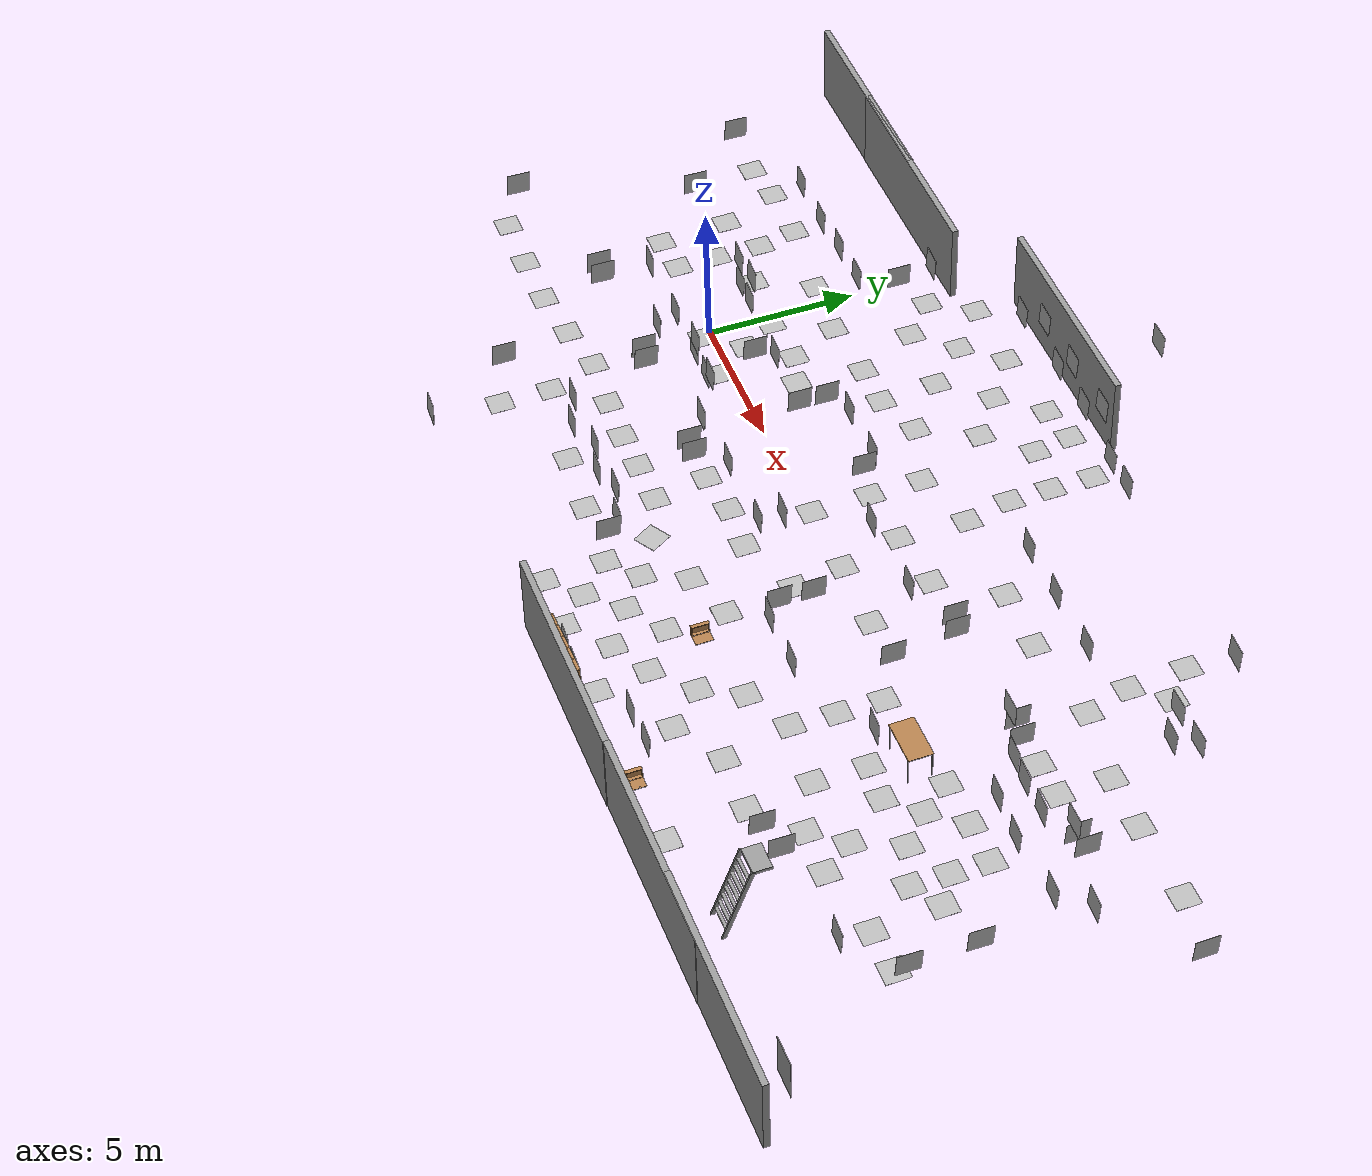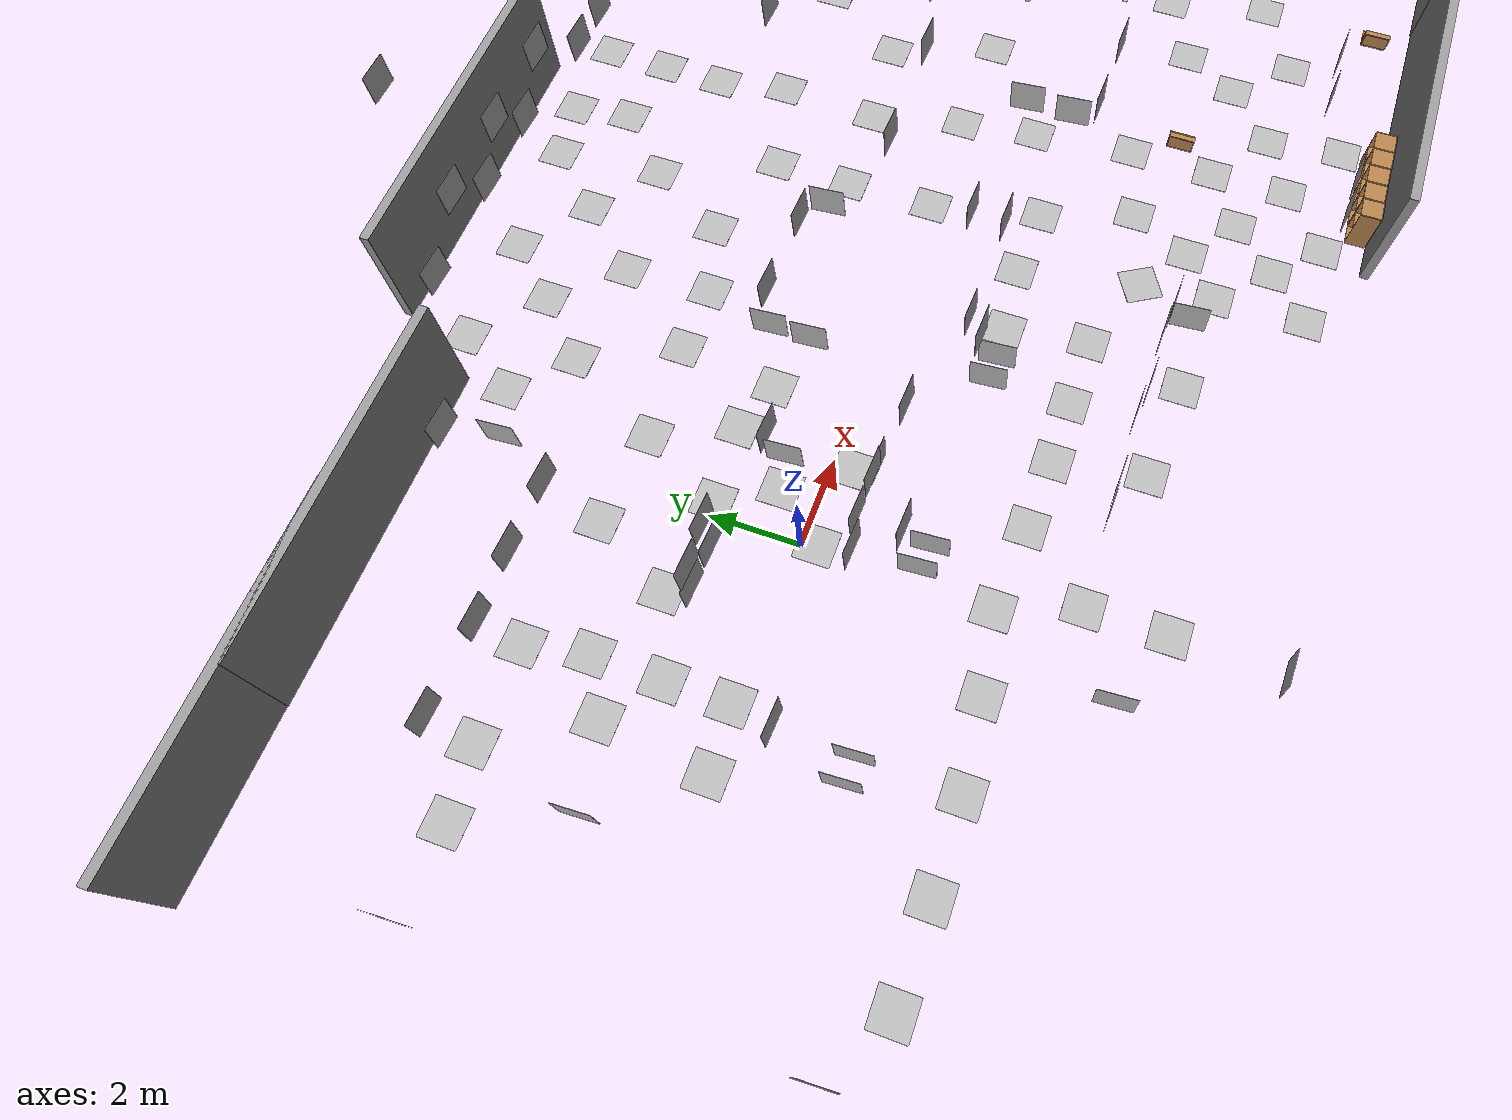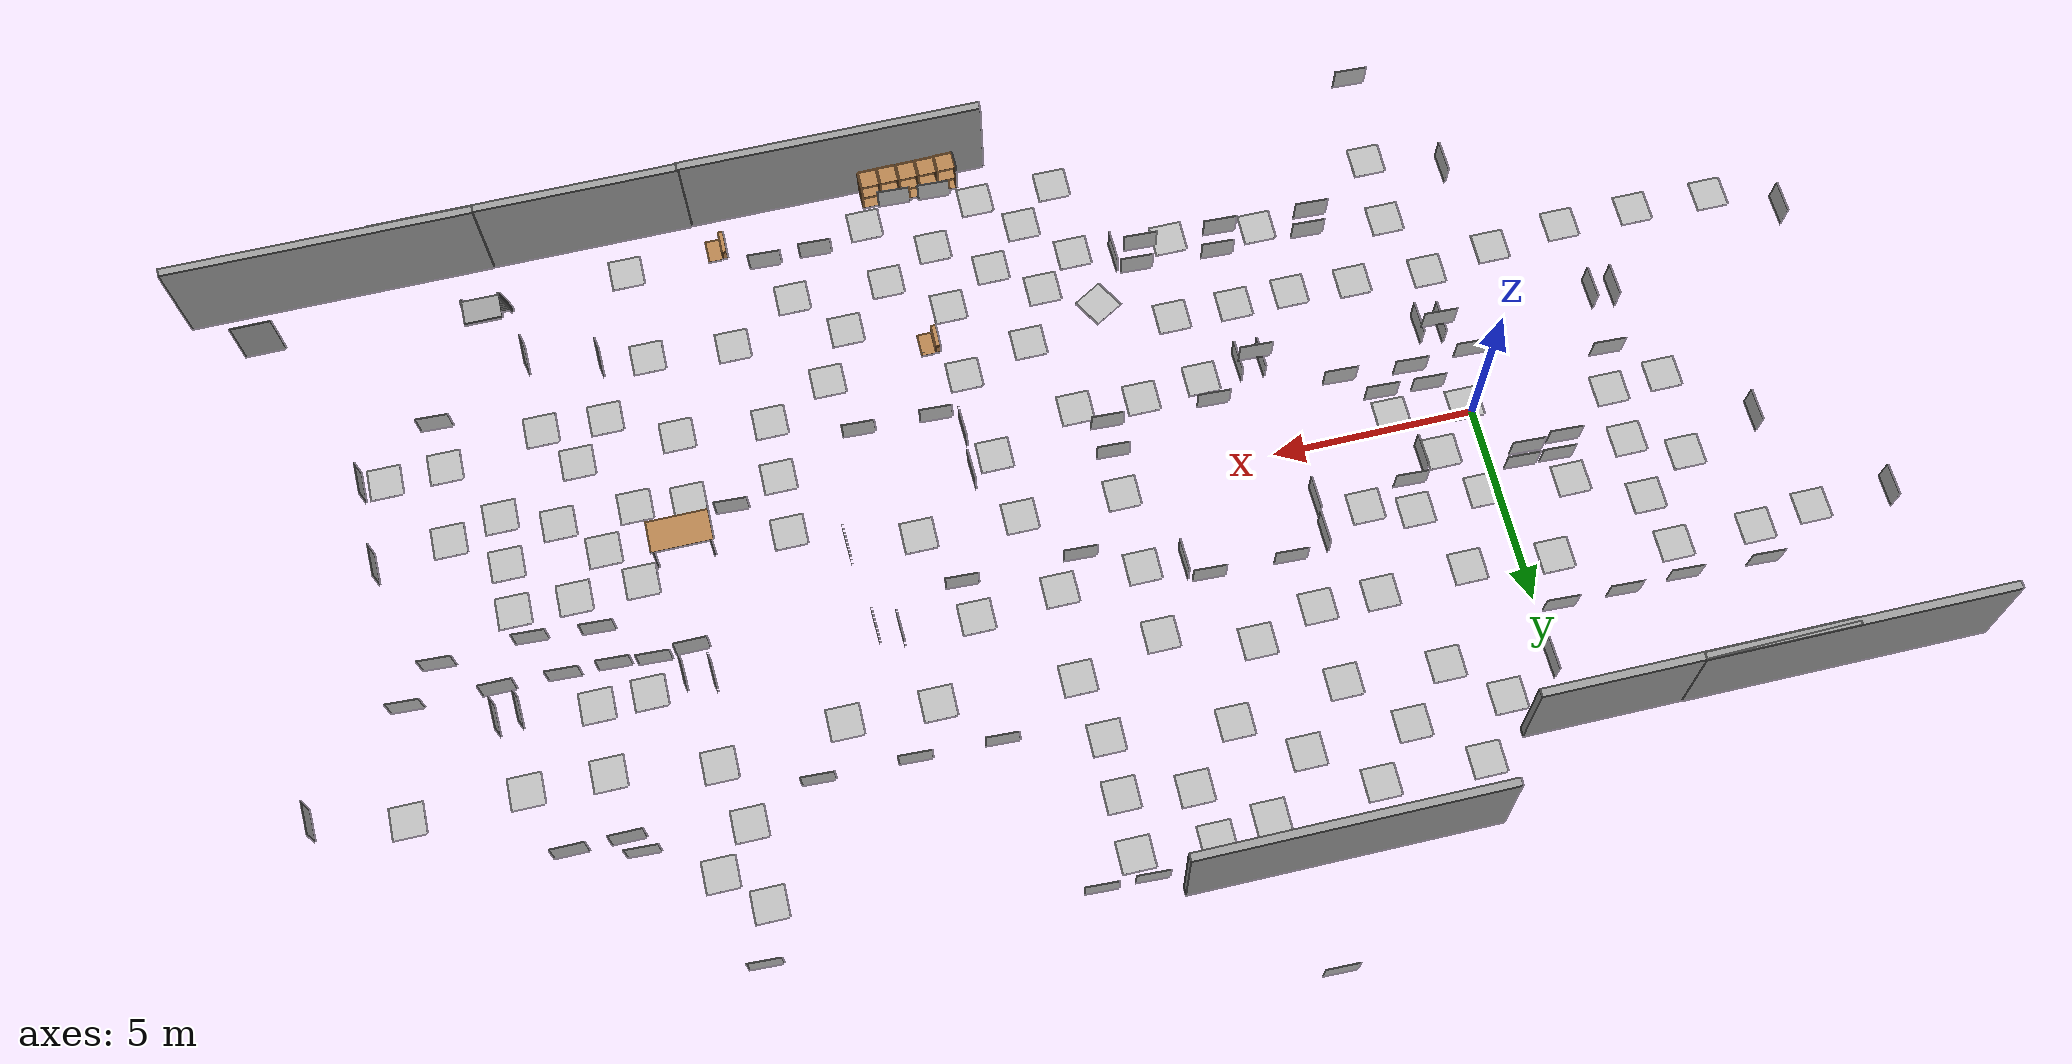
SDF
<sdf version="1.6">
 <world name="factory">
  <light name="sun" type="directional">
   <pose>0 0 10 0 -0 0</pose>
   <diffuse>0.8 0.8 0.8 1</diffuse>
   <specular>0.2 0.2 0.2 1</specular>
   <attenuation>
    <range>1000</range>
    <constant>0.9</constant>
    <linear>0.01</linear>
    <quadratic>0.001</quadratic>
   </attenuation>
   <direction>-0.5 0.1 -0.9</direction>
  </light>
  <gravity>0 0 -9.8</gravity>
  <magnetic_field>6e-06 2.3e-05 -4.2e-05</magnetic_field>
  <atmosphere type="adiabatic"/>
  <physics name="default_physics" default="0" type="ode">
   <max_step_size>0.001</max_step_size>
   <real_time_factor>1</real_time_factor>
   <real_time_update_rate>1000</real_time_update_rate>
  </physics>
  <scene><ambient>0.4 0.4 0.4 1</ambient><background>0.7 0.7 0.7 1</background><shadows>1</shadows></scene>
  <spherical_coordinates>
   <surface_model>EARTH_WGS84</surface_model>
   <latitude_deg>0</latitude_deg>
   <longitude_deg>0</longitude_deg>
   <elevation>0</elevation>
   <heading_deg>0</heading_deg>
  </spherical_coordinates>
  <model name="deletion_wall">
   <static>1</static>
   <link name="sensing_link">
    <gravity>0</gravity>
    <sensor name="object_disposal_contact" type="contact">
     <update_rate>10</update_rate>
     <contact><collision>collision</collision><topic>__default_topic__</topic></contact>
    </sensor>
    <collision name="collision"><geometry><box><size>0.1 1 1</size></box></geometry></collision>
    <visual name="visual">
     <geometry><box><size>0.1 1 1</size></box></geometry>
     <cast_shadows>0</cast_shadows>
     <transparency>100</transparency>
    </visual>
   </link>
   <plugin name="object_disposal_plugin" filename="libObjectDisposalPlugin.so">
    <contact_sensor_name>object_disposal_contact</contact_sensor_name>
    <contact_side_normal>1 0 0</contact_side_normal>
    <disposal_pose>30 30 0 0 0 0</disposal_pose>
    <update_rate>5</update_rate>
   </plugin>
   <pose>0.199032 -1.08981 0 0 -0 0</pose>
  </model>
  <model name="drone_collection_zone">
   <static>1</static>
   <link name="sensing_link">
    <gravity>0</gravity>
    <sensor name="object_disposal_contact" type="contact">
     <update_rate>10</update_rate>
     <contact><collision>collision</collision><topic>__default_topic__</topic></contact>
    </sensor>
    <collision name="collision"><geometry><box><size>0.1 2 2</size></box></geometry></collision>
   </link>
   <plugin name="object_disposal_plugin" filename="libObjectDisposalPlugin.so">
    <contact_sensor_name>object_disposal_contact</contact_sensor_name>
    <contacting_box_topic>/ariac/waiting_shipping_box</contacting_box_topic>
    <activation_topic>/ariac/drone_collection_zone/activate_deletion</activation_topic>
    <contact_side_normal>1 0 0</contact_side_normal>
    <disposal_pose>-7.5 -10 -0.5 0 0 0</disposal_pose>
    <update_rate>5</update_rate>
   </plugin>
   <pose>-0.093674 -2.00167 0 0 -0 0</pose>
  </model>
  <model name="ladder_70deg_0rails">
   <static>1</static>
   <link name="step0">
    <pose>0 0.097059 0.266667 0 -0 0</pose>
    <inertial>
     <mass>9.75482</mass>
     <inertia>
      <ixx>0.00957124</ixx>
      <iyy>0.65963</iyy>
      <izz>0.666842</izz>
      <ixy>0</ixy>
      <ixz>0</ixz>
      <iyz>0</iyz>
     </inertia>
    </inertial>
    <collision name="collision"><geometry><box><size>0.9 0.1016 0.0381</size></box></geometry></collision>
    <visual name="visual">
     <geometry><box><size>0.9 0.1016 0.0381</size></box></geometry>
     <material>
      <script><uri>file://media/materials/scripts/gazebo.material</uri><name>Gazebo/Grey</name></script>
     </material>
    </visual>
   </link>
   <link name="step1">
    <pose>0 0.194117 0.533333 0 -0 0</pose>
    <inertial>
     <mass>9.75482</mass>
     <inertia>
      <ixx>0.00957124</ixx>
      <iyy>0.65963</iyy>
      <izz>0.666842</izz>
      <ixy>0</ixy>
      <ixz>0</ixz>
      <iyz>0</iyz>
     </inertia>
    </inertial>
    <collision name="collision"><geometry><box><size>0.9 0.1016 0.0381</size></box></geometry></collision>
    <visual name="visual">
     <geometry><box><size>0.9 0.1016 0.0381</size></box></geometry>
     <material>
      <script><uri>file://media/materials/scripts/gazebo.material</uri><name>Gazebo/Grey</name></script>
     </material>
    </visual>
   </link>
   <link name="step2">
    <pose>0 0.291176 0.8 0 -0 0</pose>
    <inertial>
     <mass>9.75482</mass>
     <inertia>
      <ixx>0.00957124</ixx>
      <iyy>0.65963</iyy>
      <izz>0.666842</izz>
      <ixy>0</ixy>
      <ixz>0</ixz>
      <iyz>0</iyz>
     </inertia>
    </inertial>
    <collision name="collision"><geometry><box><size>0.9 0.1016 0.0381</size></box></geometry></collision>
    <visual name="visual">
     <geometry><box><size>0.9 0.1016 0.0381</size></box></geometry>
     <material>
      <script><uri>file://media/materials/scripts/gazebo.material</uri><name>Gazebo/Grey</name></script>
     </material>
    </visual>
   </link>
   <link name="step3">
    <pose>0 0.388235 1.06667 0 -0 0</pose>
    <inertial>
     <mass>9.75482</mass>
     <inertia>
      <ixx>0.00957124</ixx>
      <iyy>0.65963</iyy>
      <izz>0.666842</izz>
      <ixy>0</ixy>
      <ixz>0</ixz>
      <iyz>0</iyz>
     </inertia>
    </inertial>
    <collision name="collision"><geometry><box><size>0.9 0.1016 0.0381</size></box></geometry></collision>
    <visual name="visual">
     <geometry><box><size>0.9 0.1016 0.0381</size></box></geometry>
     <material>
      <script><uri>file://media/materials/scripts/gazebo.material</uri><name>Gazebo/Grey</name></script>
     </material>
    </visual>
   </link>
   <link name="step4">
    <pose>0 0.485294 1.33333 0 -0 0</pose>
    <inertial>
     <mass>9.75482</mass>
     <inertia>
      <ixx>0.00957124</ixx>
      <iyy>0.65963</iyy>
      <izz>0.666842</izz>
      <ixy>0</ixy>
      <ixz>0</ixz>
      <iyz>0</iyz>
     </inertia>
    </inertial>
    <collision name="collision"><geometry><box><size>0.9 0.1016 0.0381</size></box></geometry></collision>
    <visual name="visual">
     <geometry><box><size>0.9 0.1016 0.0381</size></box></geometry>
     <material>
      <script><uri>file://media/materials/scripts/gazebo.material</uri><name>Gazebo/Grey</name></script>
     </material>
    </visual>
   </link>
   <link name="step5">
    <pose>0 0.582352 1.6 0 -0 0</pose>
    <inertial>
     <mass>9.75482</mass>
     <inertia>
      <ixx>0.00957124</ixx>
      <iyy>0.65963</iyy>
      <izz>0.666842</izz>
      <ixy>0</ixy>
      <ixz>0</ixz>
      <iyz>0</iyz>
     </inertia>
    </inertial>
    <collision name="collision"><geometry><box><size>0.9 0.1016 0.0381</size></box></geometry></collision>
    <visual name="visual">
     <geometry><box><size>0.9 0.1016 0.0381</size></box></geometry>
     <material>
      <script><uri>file://media/materials/scripts/gazebo.material</uri><name>Gazebo/Grey</name></script>
     </material>
    </visual>
   </link>
   <link name="step6">
    <pose>0 0.679411 1.86667 0 -0 0</pose>
    <inertial>
     <mass>9.75482</mass>
     <inertia>
      <ixx>0.00957124</ixx>
      <iyy>0.65963</iyy>
      <izz>0.666842</izz>
      <ixy>0</ixy>
      <ixz>0</ixz>
      <iyz>0</iyz>
     </inertia>
    </inertial>
    <collision name="collision"><geometry><box><size>0.9 0.1016 0.0381</size></box></geometry></collision>
    <visual name="visual">
     <geometry><box><size>0.9 0.1016 0.0381</size></box></geometry>
     <material>
      <script><uri>file://media/materials/scripts/gazebo.material</uri><name>Gazebo/Grey</name></script>
     </material>
    </visual>
   </link>
   <link name="step7">
    <pose>0 0.77647 2.13333 0 -0 0</pose>
    <inertial>
     <mass>9.75482</mass>
     <inertia>
      <ixx>0.00957124</ixx>
      <iyy>0.65963</iyy>
      <izz>0.666842</izz>
      <ixy>0</ixy>
      <ixz>0</ixz>
      <iyz>0</iyz>
     </inertia>
    </inertial>
    <collision name="collision"><geometry><box><size>0.9 0.1016 0.0381</size></box></geometry></collision>
    <visual name="visual">
     <geometry><box><size>0.9 0.1016 0.0381</size></box></geometry>
     <material>
      <script><uri>file://media/materials/scripts/gazebo.material</uri><name>Gazebo/Grey</name></script>
     </material>
    </visual>
   </link>
   <link name="landing">
    <pose>0 1.17353 2.4 0 -0 0</pose>
    <inertial>
     <mass>57.6072</mass>
     <inertia><ixx>1.73518</ixx><iyy>3.89545</iyy><izz>5.6167</izz><ixy>0</ixy><ixz>0</ixz><iyz>0</iyz></inertia>
    </inertial>
    <collision name="collision"><geometry><box><size>0.9 0.6 0.1016</size></box></geometry></collision>
    <visual name="visual">
     <geometry><box><size>0.9 0.6 0.1016</size></box></geometry>
     <material>
      <script><uri>file://media/materials/scripts/gazebo.material</uri><name>Gazebo/Grey</name></script>
     </material>
    </visual>
   </link>
   <link name="left_side_wall">
    <pose>-0.45 0.436764 1.2 1.22173 -0 0</pose>
    <collision name="collision"><geometry><box><size>0.0508 2.63403 0.13</size></box></geometry></collision>
    <visual name="visual">
     <geometry><box><size>0.0508 2.63403 0.13</size></box></geometry>
     <material>
      <script><uri>file://media/materials/scripts/gazebo.material</uri><name>Gazebo/Grey</name></script>
     </material>
    </visual>
   </link>
   <link name="right_side_wall">
    <pose>0.45 0.436764 1.2 1.22173 -0 0</pose>
    <collision name="collision"><geometry><box><size>0.0508 2.63403 0.13</size></box></geometry></collision>
    <visual name="visual">
     <geometry><box><size>0.0508 2.63403 0.13</size></box></geometry>
     <material>
      <script><uri>file://media/materials/scripts/gazebo.material</uri><name>Gazebo/Grey</name></script>
     </material>
    </visual>
   </link>
   <pose>22.7475 -8.13571 0 0 -0 0</pose>
  </model>
  <model name="grey_wall">
   <static>1</static>
   <link name="link">
    <pose>0 0 1.4 0 -0 0</pose>
    <collision name="collision"><geometry><box><size>7.5 0.2 2.8</size></box></geometry></collision>
    <visual name="visual">
     <cast_shadows>0</cast_shadows>
     <geometry><box><size>7.5 0.2 2.8</size></box></geometry>
     <material>
      <script>
       <uri>model://grey_wall/materials/scripts</uri>
       <uri>model://grey_wall/materials/textures</uri>
       <name>vrc/grey_wall</name>
      </script>
     </material>
    </visual>
   </link>
   <pose>-6.34942 8.1136 0 0 -0 0</pose>
  </model>
  <model name="grey_wall_clone">
   <static>1</static>
   <link name="link">
    <pose>0 0 1.4 0 -0 0</pose>
    <collision name="collision"><geometry><box><size>7.5 0.2 2.8</size></box></geometry></collision>
    <visual name="visual">
     <cast_shadows>0</cast_shadows>
     <geometry><box><size>7.5 0.2 2.8</size></box></geometry>
     <material>
      <script>
       <uri>model://grey_wall/materials/scripts</uri>
       <uri>model://grey_wall/materials/textures</uri>
       <name>vrc/grey_wall</name>
      </script>
     </material>
    </visual>
   </link>
   <pose>-2.50623 8.09985 0 0 -0 0</pose>
  </model>
  <model name="grey_wall_clone_0">
   <static>1</static>
   <link name="link">
    <pose>0 0 1.4 0 -0 0</pose>
    <collision name="collision"><geometry><box><size>7.5 0.2 2.8</size></box></geometry></collision>
    <visual name="visual">
     <cast_shadows>0</cast_shadows>
     <geometry><box><size>7.5 0.2 2.8</size></box></geometry>
     <material>
      <script>
       <uri>model://grey_wall/materials/scripts</uri>
       <uri>model://grey_wall/materials/textures</uri>
       <name>vrc/grey_wall</name>
      </script>
     </material>
    </visual>
   </link>
   <pose>13.8347 -9.52636 0 0 -0 0</pose>
  </model>
  <model name="grey_wall_clone_1">
   <static>1</static>
   <link name="link">
    <pose>0 0 1.4 0 -0 0</pose>
    <collision name="collision"><geometry><box><size>7.5 0.2 2.8</size></box></geometry></collision>
    <visual name="visual">
     <cast_shadows>0</cast_shadows>
     <geometry><box><size>7.5 0.2 2.8</size></box></geometry>
     <material>
      <script>
       <uri>model://grey_wall/materials/scripts</uri>
       <uri>model://grey_wall/materials/textures</uri>
       <name>vrc/grey_wall</name>
      </script>
     </material>
    </visual>
   </link>
   <pose>21.3028 -9.50574 0 0 -0 0</pose>
  </model>
  <model name="grey_wall_clone_2">
   <static>1</static>
   <link name="link">
    <pose>0 0 1.4 0 -0 0</pose>
    <collision name="collision"><geometry><box><size>7.5 0.2 2.8</size></box></geometry></collision>
    <visual name="visual">
     <cast_shadows>0</cast_shadows>
     <geometry><box><size>7.5 0.2 2.8</size></box></geometry>
     <material>
      <script>
       <uri>model://grey_wall/materials/scripts</uri>
       <uri>model://grey_wall/materials/textures</uri>
       <name>vrc/grey_wall</name>
      </script>
     </material>
    </visual>
   </link>
   <pose>26.2939 -9.49059 0 0 -0 0</pose>
  </model>
  <model name="unit_box">
   <pose>28.3446 -8.3382 0.751562 -0 -1e-06 0.005665</pose>
   <link name="link">
    <inertial>
     <mass>1</mass>
     <inertia>
      <ixx>0.166667</ixx>
      <ixy>0</ixy>
      <ixz>0</ixz>
      <iyy>0.166667</iyy>
      <iyz>0</iyz>
      <izz>0.166667</izz>
     </inertia>
    </inertial>
    <collision name="collision"><geometry><box><size>1 0.0133954 1.50312</size></box></geometry></collision>
    <visual name="visual">
     <geometry><box><size>1 0.0133954 1.50312</size></box></geometry>
     <material>
      <script><name>Gazebo/Grey</name><uri>file://media/materials/scripts/gazebo.material</uri></script>
     </material>
    </visual>
   </link>
  </model>
  <model name="cabinet">
   <static>1</static>
   <link name="cabinet_bottom_plate">
    <inertial>
     <pose>0 0 -1 0 -0 0</pose>
     <inertia><ixx>2.05</ixx><ixy>0</ixy><ixz>0</ixz><iyy>2.05</iyy><iyz>0</iyz><izz>2.05</izz></inertia>
     <mass>25</mass>
    </inertial>
    <collision name="cabinet_bottom_plate_geom">
     <pose>0 0 0.01 0 -0 0</pose>
     <geometry><box><size>0.45 0.45 0.02</size></box></geometry>
    </collision>
    <visual name="cabinet_bottom_plate_geom_visual">
     <pose>0 0 0.01 0 -0 0</pose>
     <geometry><box><size>0.45 0.45 0.02</size></box></geometry>
     <material>
      <script><uri>file://media/materials/scripts/gazebo.material</uri><name>Gazebo/Wood</name></script>
     </material>
    </visual>
    <collision name="cabinet_bottom_plate_geom_cabinet_back_plate">
     <pose>0.235 0 0.51 0 -0 0</pose>
     <geometry><box><size>0.02 0.45 1.02</size></box></geometry>
    </collision>
    <visual name="cabinet_bottom_plate_geom_cabinet_back_plate_visual">
     <pose>0.235 0 0.51 0 -0 0</pose>
     <geometry><box><size>0.02 0.45 1.02</size></box></geometry>
     <material>
      <script><uri>file://media/materials/scripts/gazebo.material</uri><name>Gazebo/Wood</name></script>
     </material>
    </visual>
    <collision name="cabinet_bottom_plate_geom_cabinet_left_plate">
     <pose>0 0.235 0.51 0 -0 0</pose>
     <geometry><box><size>0.45 0.02 1.02</size></box></geometry>
    </collision>
    <visual name="cabinet_bottom_plate_geom_cabinet_left_plate_visual">
     <pose>0 0.235 0.51 0 -0 0</pose>
     <geometry><box><size>0.45 0.02 1.02</size></box></geometry>
     <material>
      <script><uri>file://media/materials/scripts/gazebo.material</uri><name>Gazebo/Wood</name></script>
     </material>
    </visual>
    <collision name="cabinet_bottom_plate_geom_cabinet_middle_plate">
     <pose>0 0 0.51 0 -0 0</pose>
     <geometry><box><size>0.45 0.45 0.02</size></box></geometry>
    </collision>
    <visual name="cabinet_bottom_plate_geom_cabinet_middle_plate_visual">
     <pose>0 0 0.51 0 -0 0</pose>
     <geometry><box><size>0.45 0.45 0.02</size></box></geometry>
     <material>
      <script><uri>file://media/materials/scripts/gazebo.material</uri><name>Gazebo/Wood</name></script>
     </material>
    </visual>
    <collision name="cabinet_bottom_plate_geom_cabinet_right_plate">
     <pose>0 -0.235 0.51 0 -0 0</pose>
     <geometry><box><size>0.45 0.02 1.02</size></box></geometry>
    </collision>
    <visual name="cabinet_bottom_plate_geom_cabinet_right_plate_visual">
     <pose>0 -0.235 0.51 0 -0 0</pose>
     <geometry><box><size>0.45 0.02 1.02</size></box></geometry>
     <material>
      <script><uri>file://media/materials/scripts/gazebo.material</uri><name>Gazebo/Wood</name></script>
     </material>
    </visual>
    <collision name="cabinet_bottom_plate_geom_cabinet_top_plate">
     <pose>0 0 1.01 0 -0 0</pose>
     <geometry><box><size>0.45 0.45 0.02</size></box></geometry>
    </collision>
    <visual name="cabinet_bottom_plate_geom_cabinet_top_plate_visual">
     <pose>0 0 1.01 0 -0 0</pose>
     <geometry><box><size>0.45 0.45 0.02</size></box></geometry>
     <material>
      <script><uri>file://media/materials/scripts/gazebo.material</uri><name>Gazebo/Wood</name></script>
     </material>
    </visual>
   </link>
   <pose>13.0394 -9.13497 0.037072 0 0 -1.55676</pose>
  </model>
  <model name="wooden_case">
   <link name="base">
    <pose>0 0 0.024 0 -0 0</pose>
    <inertial>
     <pose>-0.022184 0 0.171592 0 -0 0</pose>
     <mass>3.96264</mass>
     <inertia>
      <ixx>0.213536</ixx>
      <ixy>0</ixy>
      <ixz>0.000779377</ixz>
      <iyy>0.0708943</iyy>
      <iyz>0</iyz>
      <izz>0.154604</izz>
     </inertia>
    </inertial>
    <collision name="collision_back">
     <pose>-0.053975 0 0.1778 0 -0 0</pose>
     <geometry><box><size>0.01905 0.5461 0.3175</size></box></geometry>
     <surface>
      <contact>
       <poissons_ratio>0.347</poissons_ratio>
       <elastic_modulus>8.8e+09</elastic_modulus>
       <ode><kp>100000</kp><kd>100</kd><max_vel>100</max_vel><min_depth>0.001</min_depth></ode>
      </contact>
      <friction>
       <torsional>
        <coefficient>1</coefficient>
        <use_patch_radius>0</use_patch_radius>
        <surface_radius>0.01</surface_radius>
       </torsional>
      </friction>
     </surface>
    </collision>
    <visual name="visual_back">
     <pose>-0.053975 0 0.1778 0 -0 0</pose>
     <geometry><box><size>0.01905 0.5461 0.3175</size></box></geometry>
     <material>
      <script><uri>file://media/materials/scripts/gazebo.material</uri><name>Gazebo/Wood</name></script>
     </material>
    </visual>
    <collision name="collision_bottom">
     <pose>0 0 0.009525 0 -0 0</pose>
     <geometry><box><size>0.127 0.5842 0.01905</size></box></geometry>
     <surface>
      <contact>
       <poissons_ratio>0.347</poissons_ratio>
       <elastic_modulus>8.8e+09</elastic_modulus>
       <ode><kp>100000</kp><kd>100</kd><max_vel>100</max_vel><min_depth>0.001</min_depth></ode>
      </contact>
      <friction>
       <torsional>
        <coefficient>1</coefficient>
        <use_patch_radius>0</use_patch_radius>
        <surface_radius>0.01</surface_radius>
       </torsional>
      </friction>
     </surface>
    </collision>
    <visual name="visual_bottom">
     <pose>0 0 0.009525 0 -0 0</pose>
     <geometry><box><size>0.127 0.5842 0.01905</size></box></geometry>
     <material>
      <script><uri>file://media/materials/scripts/gazebo.material</uri><name>Gazebo/Wood</name></script>
     </material>
    </visual>
    <collision name="collision_top">
     <pose>0 0 0.346075 0 -0 0</pose>
     <geometry><box><size>0.127 0.5842 0.01905</size></box></geometry>
     <surface>
      <contact>
       <poissons_ratio>0.347</poissons_ratio>
       <elastic_modulus>8.8e+09</elastic_modulus>
       <ode><kp>100000</kp><kd>100</kd><max_vel>100</max_vel><min_depth>0.001</min_depth></ode>
      </contact>
      <friction>
       <torsional>
        <coefficient>1</coefficient>
        <use_patch_radius>0</use_patch_radius>
        <surface_radius>0.01</surface_radius>
       </torsional>
      </friction>
     </surface>
    </collision>
    <visual name="visual_top">
     <pose>0 0 0.346075 0 -0 0</pose>
     <geometry><box><size>0.127 0.5842 0.01905</size></box></geometry>
     <material>
      <script><uri>file://media/materials/scripts/gazebo.material</uri><name>Gazebo/Wood</name></script>
     </material>
    </visual>
    <collision name="collision_left">
     <pose>0 -0.282575 0.1778 0 -0 0</pose>
     <geometry><box><size>0.127 0.01905 0.3175</size></box></geometry>
     <surface>
      <contact>
       <poissons_ratio>0.347</poissons_ratio>
       <elastic_modulus>8.8e+09</elastic_modulus>
       <ode><kp>100000</kp><kd>100</kd><max_vel>100</max_vel><min_depth>0.001</min_depth></ode>
      </contact>
      <friction>
       <torsional>
        <coefficient>1</coefficient>
        <use_patch_radius>0</use_patch_radius>
        <surface_radius>0.01</surface_radius>
       </torsional>
      </friction>
     </surface>
    </collision>
    <visual name="visual_left">
     <pose>0 -0.282575 0.1778 0 -0 0</pose>
     <geometry><box><size>0.127 0.01905 0.3175</size></box></geometry>
     <material>
      <script><uri>file://media/materials/scripts/gazebo.material</uri><name>Gazebo/Wood</name></script>
     </material>
    </visual>
    <collision name="collision_right">
     <pose>0 0.282575 0.1778 0 -0 0</pose>
     <geometry><box><size>0.127 0.01905 0.3175</size></box></geometry>
     <surface>
      <contact>
       <poissons_ratio>0.347</poissons_ratio>
       <elastic_modulus>8.8e+09</elastic_modulus>
       <ode><kp>100000</kp><kd>100</kd><max_vel>100</max_vel><min_depth>0.001</min_depth></ode>
      </contact>
      <friction>
       <torsional>
        <coefficient>1</coefficient>
        <use_patch_radius>0</use_patch_radius>
        <surface_radius>0.01</surface_radius>
       </torsional>
      </friction>
     </surface>
    </collision>
    <visual name="visual_right">
     <pose>0 0.282575 0.1778 0 -0 0</pose>
     <geometry><box><size>0.127 0.01905 0.3175</size></box></geometry>
     <material>
      <script><uri>file://media/materials/scripts/gazebo.material</uri><name>Gazebo/Wood</name></script>
     </material>
    </visual>
    <collision name="collision_block_left">
     <pose>0.0095 -0.2151 -0.012 0 -0 0</pose>
     <geometry><box><size>0.108 0.05 0.024</size></box></geometry>
     <surface>
      <contact>
       <poissons_ratio>0.347</poissons_ratio>
       <elastic_modulus>8.8e+09</elastic_modulus>
       <ode><kp>100000</kp><kd>100</kd><max_vel>100</max_vel><min_depth>0.001</min_depth></ode>
      </contact>
      <friction>
       <torsional>
        <coefficient>1</coefficient>
        <use_patch_radius>0</use_patch_radius>
        <surface_radius>0.01</surface_radius>
       </torsional>
      </friction>
     </surface>
    </collision>
    <visual name="visual_block_left">
     <pose>0.0095 -0.2151 -0.012 0 -0 0</pose>
     <geometry><box><size>0.108 0.05 0.024</size></box></geometry>
     <material>
      <script><uri>file://media/materials/scripts/gazebo.material</uri><name>Gazebo/Wood</name></script>
     </material>
    </visual>
    <collision name="collision_block_right">
     <pose>0.0095 0.2151 -0.012 0 -0 0</pose>
     <geometry><box><size>0.108 0.05 0.024</size></box></geometry>
     <surface>
      <contact>
       <poissons_ratio>0.347</poissons_ratio>
       <elastic_modulus>8.8e+09</elastic_modulus>
       <ode><kp>100000</kp><kd>100</kd><max_vel>100</max_vel><min_depth>0.001</min_depth></ode>
      </contact>
      <friction>
       <torsional>
        <coefficient>1</coefficient>
        <use_patch_radius>0</use_patch_radius>
        <surface_radius>0.01</surface_radius>
       </torsional>
      </friction>
     </surface>
    </collision>
    <visual name="visual_block_right">
     <pose>0.0095 0.2151 -0.012 0 -0 0</pose>
     <geometry><box><size>0.108 0.05 0.024</size></box></geometry>
     <material>
      <script><uri>file://media/materials/scripts/gazebo.material</uri><name>Gazebo/Wood</name></script>
     </material>
    </visual>
   </link>
   <link name="lid">
    <pose>0.243775 0 0.009525 0 -0 0</pose>
    <inertial>
     <mass>1.97874</mass>
     <inertia>
      <ixx>0.0563367</ixx>
      <ixy>0</ixy>
      <ixz>0</ixz>
      <iyy>0.020911</iyy>
      <iyz>0</iyz>
      <izz>0.0771281</izz>
     </inertia>
    </inertial>
    <collision name="collision">
     <geometry><box><size>0.3556 0.5842 0.01905</size></box></geometry>
     <surface>
      <contact>
       <poissons_ratio>0.347</poissons_ratio>
       <elastic_modulus>8.8e+09</elastic_modulus>
       <ode><kp>100000</kp><kd>100</kd><max_vel>100</max_vel><min_depth>0.001</min_depth></ode>
      </contact>
      <friction>
       <torsional>
        <coefficient>1</coefficient>
        <use_patch_radius>0</use_patch_radius>
        <surface_radius>0.01</surface_radius>
       </torsional>
      </friction>
     </surface>
    </collision>
    <visual name="visual">
     <geometry><box><size>0.3556 0.5842 0.01905</size></box></geometry>
     <material>
      <script><uri>file://media/materials/scripts/gazebo.material</uri><name>Gazebo/Wood</name></script>
     </material>
    </visual>
    <visual name="tee_nut_1">
     <pose>0.122 -0.216 0 0 -0 0</pose>
     <geometry><cylinder><radius>0.00635</radius><length>0.0192405</length></cylinder></geometry>
     <material>
      <script><uri>file://media/materials/scripts/gazebo.material</uri><name>Gazebo/Grey</name></script>
     </material>
    </visual>
    <visual name="tee_nut_2">
     <pose>0.122 -0.088 0 0 -0 0</pose>
     <geometry><cylinder><radius>0.00635</radius><length>0.0192405</length></cylinder></geometry>
     <material>
      <script><uri>file://media/materials/scripts/gazebo.material</uri><name>Gazebo/Grey</name></script>
     </material>
    </visual>
    <visual name="tee_nut_3">
     <pose>0.122 0.088 0 0 -0 0</pose>
     <geometry><cylinder><radius>0.00635</radius><length>0.0192405</length></cylinder></geometry>
     <material>
      <script><uri>file://media/materials/scripts/gazebo.material</uri><name>Gazebo/Grey</name></script>
     </material>
    </visual>
    <visual name="tee_nut_4">
     <pose>0.122 0.216 0 0 -0 0</pose>
     <geometry><cylinder><radius>0.00635</radius><length>0.0192405</length></cylinder></geometry>
     <material>
      <script><uri>file://media/materials/scripts/gazebo.material</uri><name>Gazebo/Grey</name></script>
     </material>
    </visual>
   </link>
   <joint name="lid_hinge" type="revolute">
    <pose>-0.1778 0 0.01905 0 -0 0</pose>
    <parent>base</parent>
    <child>lid</child>
    <axis>
     <xyz>0 1 0</xyz>
     <limit><upper>0.523599</upper><lower>-1.5708</lower></limit>
     <use_parent_model_frame>0</use_parent_model_frame>
     <dynamics><spring_reference>0</spring_reference><spring_stiffness>0</spring_stiffness></dynamics>
    </axis>
   </joint>
   <pose>16.9031 -8.59915 -0.001057 0 -0.000442 -1e-06</pose>
  </model>
  <model name="cabinet_clone">
   <static>1</static>
   <link name="cabinet_bottom_plate">
    <inertial>
     <pose>0 0 -1 0 -0 0</pose>
     <inertia><ixx>2.05</ixx><ixy>0</ixy><ixz>0</ixz><iyy>2.05</iyy><iyz>0</iyz><izz>2.05</izz></inertia>
     <mass>25</mass>
    </inertial>
    <collision name="cabinet_bottom_plate_geom">
     <pose>0 0 0.01 0 -0 0</pose>
     <geometry><box><size>0.45 0.45 0.02</size></box></geometry>
    </collision>
    <visual name="cabinet_bottom_plate_geom_visual">
     <pose>0 0 0.01 0 -0 0</pose>
     <geometry><box><size>0.45 0.45 0.02</size></box></geometry>
     <material>
      <script><uri>file://media/materials/scripts/gazebo.material</uri><name>Gazebo/Wood</name></script>
     </material>
    </visual>
    <collision name="cabinet_bottom_plate_geom_cabinet_back_plate">
     <pose>0.235 0 0.51 0 -0 0</pose>
     <geometry><box><size>0.02 0.45 1.02</size></box></geometry>
    </collision>
    <visual name="cabinet_bottom_plate_geom_cabinet_back_plate_visual">
     <pose>0.235 0 0.51 0 -0 0</pose>
     <geometry><box><size>0.02 0.45 1.02</size></box></geometry>
     <material>
      <script><uri>file://media/materials/scripts/gazebo.material</uri><name>Gazebo/Wood</name></script>
     </material>
    </visual>
    <collision name="cabinet_bottom_plate_geom_cabinet_left_plate">
     <pose>0 0.235 0.51 0 -0 0</pose>
     <geometry><box><size>0.45 0.02 1.02</size></box></geometry>
    </collision>
    <visual name="cabinet_bottom_plate_geom_cabinet_left_plate_visual">
     <pose>0 0.235 0.51 0 -0 0</pose>
     <geometry><box><size>0.45 0.02 1.02</size></box></geometry>
     <material>
      <script><uri>file://media/materials/scripts/gazebo.material</uri><name>Gazebo/Wood</name></script>
     </material>
    </visual>
    <collision name="cabinet_bottom_plate_geom_cabinet_middle_plate">
     <pose>0 0 0.51 0 -0 0</pose>
     <geometry><box><size>0.45 0.45 0.02</size></box></geometry>
    </collision>
    <visual name="cabinet_bottom_plate_geom_cabinet_middle_plate_visual">
     <pose>0 0 0.51 0 -0 0</pose>
     <geometry><box><size>0.45 0.45 0.02</size></box></geometry>
     <material>
      <script><uri>file://media/materials/scripts/gazebo.material</uri><name>Gazebo/Wood</name></script>
     </material>
    </visual>
    <collision name="cabinet_bottom_plate_geom_cabinet_right_plate">
     <pose>0 -0.235 0.51 0 -0 0</pose>
     <geometry><box><size>0.45 0.02 1.02</size></box></geometry>
    </collision>
    <visual name="cabinet_bottom_plate_geom_cabinet_right_plate_visual">
     <pose>0 -0.235 0.51 0 -0 0</pose>
     <geometry><box><size>0.45 0.02 1.02</size></box></geometry>
     <material>
      <script><uri>file://media/materials/scripts/gazebo.material</uri><name>Gazebo/Wood</name></script>
     </material>
    </visual>
    <collision name="cabinet_bottom_plate_geom_cabinet_top_plate">
     <pose>0 0 1.01 0 -0 0</pose>
     <geometry><box><size>0.45 0.45 0.02</size></box></geometry>
    </collision>
    <visual name="cabinet_bottom_plate_geom_cabinet_top_plate_visual">
     <pose>0 0 1.01 0 -0 0</pose>
     <geometry><box><size>0.45 0.45 0.02</size></box></geometry>
     <material>
      <script><uri>file://media/materials/scripts/gazebo.material</uri><name>Gazebo/Wood</name></script>
     </material>
    </visual>
   </link>
   <pose>12.5585 -9.14446 0.037072 0 0 -1.55676</pose>
  </model>
  <model name="cabinet_clone_0">
   <static>1</static>
   <link name="cabinet_bottom_plate">
    <inertial>
     <pose>0 0 -1 0 -0 0</pose>
     <inertia><ixx>2.05</ixx><ixy>0</ixy><ixz>0</ixz><iyy>2.05</iyy><iyz>0</iyz><izz>2.05</izz></inertia>
     <mass>25</mass>
    </inertial>
    <collision name="cabinet_bottom_plate_geom">
     <pose>0 0 0.01 0 -0 0</pose>
     <geometry><box><size>0.45 0.45 0.02</size></box></geometry>
    </collision>
    <visual name="cabinet_bottom_plate_geom_visual">
     <pose>0 0 0.01 0 -0 0</pose>
     <geometry><box><size>0.45 0.45 0.02</size></box></geometry>
     <material>
      <script><uri>file://media/materials/scripts/gazebo.material</uri><name>Gazebo/Wood</name></script>
     </material>
    </visual>
    <collision name="cabinet_bottom_plate_geom_cabinet_back_plate">
     <pose>0.235 0 0.51 0 -0 0</pose>
     <geometry><box><size>0.02 0.45 1.02</size></box></geometry>
    </collision>
    <visual name="cabinet_bottom_plate_geom_cabinet_back_plate_visual">
     <pose>0.235 0 0.51 0 -0 0</pose>
     <geometry><box><size>0.02 0.45 1.02</size></box></geometry>
     <material>
      <script><uri>file://media/materials/scripts/gazebo.material</uri><name>Gazebo/Wood</name></script>
     </material>
    </visual>
    <collision name="cabinet_bottom_plate_geom_cabinet_left_plate">
     <pose>0 0.235 0.51 0 -0 0</pose>
     <geometry><box><size>0.45 0.02 1.02</size></box></geometry>
    </collision>
    <visual name="cabinet_bottom_plate_geom_cabinet_left_plate_visual">
     <pose>0 0.235 0.51 0 -0 0</pose>
     <geometry><box><size>0.45 0.02 1.02</size></box></geometry>
     <material>
      <script><uri>file://media/materials/scripts/gazebo.material</uri><name>Gazebo/Wood</name></script>
     </material>
    </visual>
    <collision name="cabinet_bottom_plate_geom_cabinet_middle_plate">
     <pose>0 0 0.51 0 -0 0</pose>
     <geometry><box><size>0.45 0.45 0.02</size></box></geometry>
    </collision>
    <visual name="cabinet_bottom_plate_geom_cabinet_middle_plate_visual">
     <pose>0 0 0.51 0 -0 0</pose>
     <geometry><box><size>0.45 0.45 0.02</size></box></geometry>
     <material>
      <script><uri>file://media/materials/scripts/gazebo.material</uri><name>Gazebo/Wood</name></script>
     </material>
    </visual>
    <collision name="cabinet_bottom_plate_geom_cabinet_right_plate">
     <pose>0 -0.235 0.51 0 -0 0</pose>
     <geometry><box><size>0.45 0.02 1.02</size></box></geometry>
    </collision>
    <visual name="cabinet_bottom_plate_geom_cabinet_right_plate_visual">
     <pose>0 -0.235 0.51 0 -0 0</pose>
     <geometry><box><size>0.45 0.02 1.02</size></box></geometry>
     <material>
      <script><uri>file://media/materials/scripts/gazebo.material</uri><name>Gazebo/Wood</name></script>
     </material>
    </visual>
    <collision name="cabinet_bottom_plate_geom_cabinet_top_plate">
     <pose>0 0 1.01 0 -0 0</pose>
     <geometry><box><size>0.45 0.45 0.02</size></box></geometry>
    </collision>
    <visual name="cabinet_bottom_plate_geom_cabinet_top_plate_visual">
     <pose>0 0 1.01 0 -0 0</pose>
     <geometry><box><size>0.45 0.45 0.02</size></box></geometry>
     <material>
      <script><uri>file://media/materials/scripts/gazebo.material</uri><name>Gazebo/Wood</name></script>
     </material>
    </visual>
   </link>
   <pose>12.0748 -9.14339 0.037072 0 0 -1.55676</pose>
  </model>
  <model name="cabinet_clone_1">
   <static>1</static>
   <link name="cabinet_bottom_plate">
    <inertial>
     <pose>0 0 -1 0 -0 0</pose>
     <inertia><ixx>2.05</ixx><ixy>0</ixy><ixz>0</ixz><iyy>2.05</iyy><iyz>0</iyz><izz>2.05</izz></inertia>
     <mass>25</mass>
    </inertial>
    <collision name="cabinet_bottom_plate_geom">
     <pose>0 0 0.01 0 -0 0</pose>
     <geometry><box><size>0.45 0.45 0.02</size></box></geometry>
    </collision>
    <visual name="cabinet_bottom_plate_geom_visual">
     <pose>0 0 0.01 0 -0 0</pose>
     <geometry><box><size>0.45 0.45 0.02</size></box></geometry>
     <material>
      <script><uri>file://media/materials/scripts/gazebo.material</uri><name>Gazebo/Wood</name></script>
     </material>
    </visual>
    <collision name="cabinet_bottom_plate_geom_cabinet_back_plate">
     <pose>0.235 0 0.51 0 -0 0</pose>
     <geometry><box><size>0.02 0.45 1.02</size></box></geometry>
    </collision>
    <visual name="cabinet_bottom_plate_geom_cabinet_back_plate_visual">
     <pose>0.235 0 0.51 0 -0 0</pose>
     <geometry><box><size>0.02 0.45 1.02</size></box></geometry>
     <material>
      <script><uri>file://media/materials/scripts/gazebo.material</uri><name>Gazebo/Wood</name></script>
     </material>
    </visual>
    <collision name="cabinet_bottom_plate_geom_cabinet_left_plate">
     <pose>0 0.235 0.51 0 -0 0</pose>
     <geometry><box><size>0.45 0.02 1.02</size></box></geometry>
    </collision>
    <visual name="cabinet_bottom_plate_geom_cabinet_left_plate_visual">
     <pose>0 0.235 0.51 0 -0 0</pose>
     <geometry><box><size>0.45 0.02 1.02</size></box></geometry>
     <material>
      <script><uri>file://media/materials/scripts/gazebo.material</uri><name>Gazebo/Wood</name></script>
     </material>
    </visual>
    <collision name="cabinet_bottom_plate_geom_cabinet_middle_plate">
     <pose>0 0 0.51 0 -0 0</pose>
     <geometry><box><size>0.45 0.45 0.02</size></box></geometry>
    </collision>
    <visual name="cabinet_bottom_plate_geom_cabinet_middle_plate_visual">
     <pose>0 0 0.51 0 -0 0</pose>
     <geometry><box><size>0.45 0.45 0.02</size></box></geometry>
     <material>
      <script><uri>file://media/materials/scripts/gazebo.material</uri><name>Gazebo/Wood</name></script>
     </material>
    </visual>
    <collision name="cabinet_bottom_plate_geom_cabinet_right_plate">
     <pose>0 -0.235 0.51 0 -0 0</pose>
     <geometry><box><size>0.45 0.02 1.02</size></box></geometry>
    </collision>
    <visual name="cabinet_bottom_plate_geom_cabinet_right_plate_visual">
     <pose>0 -0.235 0.51 0 -0 0</pose>
     <geometry><box><size>0.45 0.02 1.02</size></box></geometry>
     <material>
      <script><uri>file://media/materials/scripts/gazebo.material</uri><name>Gazebo/Wood</name></script>
     </material>
    </visual>
    <collision name="cabinet_bottom_plate_geom_cabinet_top_plate">
     <pose>0 0 1.01 0 -0 0</pose>
     <geometry><box><size>0.45 0.45 0.02</size></box></geometry>
    </collision>
    <visual name="cabinet_bottom_plate_geom_cabinet_top_plate_visual">
     <pose>0 0 1.01 0 -0 0</pose>
     <geometry><box><size>0.45 0.45 0.02</size></box></geometry>
     <material>
      <script><uri>file://media/materials/scripts/gazebo.material</uri><name>Gazebo/Wood</name></script>
     </material>
    </visual>
   </link>
   <pose>11.5886 -9.15198 0.037072 0 0 -1.55676</pose>
  </model>
  <model name="cabinet_clone_2">
   <static>1</static>
   <link name="cabinet_bottom_plate">
    <inertial>
     <pose>0 0 -1 0 -0 0</pose>
     <inertia><ixx>2.05</ixx><ixy>0</ixy><ixz>0</ixz><iyy>2.05</iyy><iyz>0</iyz><izz>2.05</izz></inertia>
     <mass>25</mass>
    </inertial>
    <collision name="cabinet_bottom_plate_geom">
     <pose>0 0 0.01 0 -0 0</pose>
     <geometry><box><size>0.45 0.45 0.02</size></box></geometry>
    </collision>
    <visual name="cabinet_bottom_plate_geom_visual">
     <pose>0 0 0.01 0 -0 0</pose>
     <geometry><box><size>0.45 0.45 0.02</size></box></geometry>
     <material>
      <script><uri>file://media/materials/scripts/gazebo.material</uri><name>Gazebo/Wood</name></script>
     </material>
    </visual>
    <collision name="cabinet_bottom_plate_geom_cabinet_back_plate">
     <pose>0.235 0 0.51 0 -0 0</pose>
     <geometry><box><size>0.02 0.45 1.02</size></box></geometry>
    </collision>
    <visual name="cabinet_bottom_plate_geom_cabinet_back_plate_visual">
     <pose>0.235 0 0.51 0 -0 0</pose>
     <geometry><box><size>0.02 0.45 1.02</size></box></geometry>
     <material>
      <script><uri>file://media/materials/scripts/gazebo.material</uri><name>Gazebo/Wood</name></script>
     </material>
    </visual>
    <collision name="cabinet_bottom_plate_geom_cabinet_left_plate">
     <pose>0 0.235 0.51 0 -0 0</pose>
     <geometry><box><size>0.45 0.02 1.02</size></box></geometry>
    </collision>
    <visual name="cabinet_bottom_plate_geom_cabinet_left_plate_visual">
     <pose>0 0.235 0.51 0 -0 0</pose>
     <geometry><box><size>0.45 0.02 1.02</size></box></geometry>
     <material>
      <script><uri>file://media/materials/scripts/gazebo.material</uri><name>Gazebo/Wood</name></script>
     </material>
    </visual>
    <collision name="cabinet_bottom_plate_geom_cabinet_middle_plate">
     <pose>0 0 0.51 0 -0 0</pose>
     <geometry><box><size>0.45 0.45 0.02</size></box></geometry>
    </collision>
    <visual name="cabinet_bottom_plate_geom_cabinet_middle_plate_visual">
     <pose>0 0 0.51 0 -0 0</pose>
     <geometry><box><size>0.45 0.45 0.02</size></box></geometry>
     <material>
      <script><uri>file://media/materials/scripts/gazebo.material</uri><name>Gazebo/Wood</name></script>
     </material>
    </visual>
    <collision name="cabinet_bottom_plate_geom_cabinet_right_plate">
     <pose>0 -0.235 0.51 0 -0 0</pose>
     <geometry><box><size>0.45 0.02 1.02</size></box></geometry>
    </collision>
    <visual name="cabinet_bottom_plate_geom_cabinet_right_plate_visual">
     <pose>0 -0.235 0.51 0 -0 0</pose>
     <geometry><box><size>0.45 0.02 1.02</size></box></geometry>
     <material>
      <script><uri>file://media/materials/scripts/gazebo.material</uri><name>Gazebo/Wood</name></script>
     </material>
    </visual>
    <collision name="cabinet_bottom_plate_geom_cabinet_top_plate">
     <pose>0 0 1.01 0 -0 0</pose>
     <geometry><box><size>0.45 0.45 0.02</size></box></geometry>
    </collision>
    <visual name="cabinet_bottom_plate_geom_cabinet_top_plate_visual">
     <pose>0 0 1.01 0 -0 0</pose>
     <geometry><box><size>0.45 0.45 0.02</size></box></geometry>
     <material>
      <script><uri>file://media/materials/scripts/gazebo.material</uri><name>Gazebo/Wood</name></script>
     </material>
    </visual>
   </link>
   <pose>11.1088 -9.16946 0.037072 0 0 -1.55676</pose>
  </model>
  <model name="table">
   <static>1</static>
   <link name="link">
    <collision name="surface">
     <pose>0 0 1 0 -0 0</pose>
     <geometry><box><size>1.5 0.8 0.03</size></box></geometry>
     <surface><friction><ode><mu>0.6</mu><mu2>0.6</mu2></ode></friction></surface>
    </collision>
    <visual name="visual1">
     <pose>0 0 1 0 -0 0</pose>
     <geometry><box><size>1.5 0.8 0.03</size></box></geometry>
     <material>
      <script><uri>file://media/materials/scripts/gazebo.material</uri><name>Gazebo/Wood</name></script>
     </material>
    </visual>
    <collision name="front_left_leg">
     <pose>0.68 0.38 0.5 0 -0 0</pose>
     <geometry><cylinder><radius>0.02</radius><length>1</length></cylinder></geometry>
    </collision>
    <visual name="front_left_leg">
     <pose>0.68 0.38 0.5 0 -0 0</pose>
     <geometry><cylinder><radius>0.02</radius><length>1</length></cylinder></geometry>
     <material>
      <script><uri>file://media/materials/scripts/gazebo.material</uri><name>Gazebo/Grey</name></script>
     </material>
    </visual>
    <collision name="front_right_leg">
     <pose>0.68 -0.38 0.5 0 -0 0</pose>
     <geometry><cylinder><radius>0.02</radius><length>1</length></cylinder></geometry>
    </collision>
    <visual name="front_right_leg">
     <pose>0.68 -0.38 0.5 0 -0 0</pose>
     <geometry><cylinder><radius>0.02</radius><length>1</length></cylinder></geometry>
     <material>
      <script><uri>file://media/materials/scripts/gazebo.material</uri><name>Gazebo/Grey</name></script>
     </material>
    </visual>
    <collision name="back_right_leg">
     <pose>-0.68 -0.38 0.5 0 -0 0</pose>
     <geometry><cylinder><radius>0.02</radius><length>1</length></cylinder></geometry>
    </collision>
    <visual name="back_right_leg">
     <pose>-0.68 -0.38 0.5 0 -0 0</pose>
     <geometry><cylinder><radius>0.02</radius><length>1</length></cylinder></geometry>
     <material>
      <script><uri>file://media/materials/scripts/gazebo.material</uri><name>Gazebo/Grey</name></script>
     </material>
    </visual>
    <collision name="back_left_leg">
     <pose>-0.68 0.38 0.5 0 -0 0</pose>
     <geometry><cylinder><radius>0.02</radius><length>1</length></cylinder></geometry>
    </collision>
    <visual name="back_left_leg">
     <pose>-0.68 0.38 0.5 0 -0 0</pose>
     <geometry><cylinder><radius>0.02</radius><length>1</length></cylinder></geometry>
     <material>
      <script><uri>file://media/materials/scripts/gazebo.material</uri><name>Gazebo/Grey</name></script>
     </material>
    </visual>
   </link>
   <pose>19.256 -0.907717 0 0 -0 0</pose>
  </model>
  <model name="wooden_case_clone">
   <link name="base">
    <pose>0 0 0.024 0 -0 0</pose>
    <inertial>
     <pose>-0.022184 0 0.171592 0 -0 0</pose>
     <mass>3.96264</mass>
     <inertia>
      <ixx>0.213536</ixx>
      <ixy>0</ixy>
      <ixz>0.000779377</ixz>
      <iyy>0.0708943</iyy>
      <iyz>0</iyz>
      <izz>0.154604</izz>
     </inertia>
    </inertial>
    <collision name="collision_back">
     <pose>-0.053975 0 0.1778 0 -0 0</pose>
     <geometry><box><size>0.01905 0.5461 0.3175</size></box></geometry>
     <surface>
      <contact>
       <poissons_ratio>0.347</poissons_ratio>
       <elastic_modulus>8.8e+09</elastic_modulus>
       <ode><kp>100000</kp><kd>100</kd><max_vel>100</max_vel><min_depth>0.001</min_depth></ode>
      </contact>
      <friction>
       <torsional>
        <coefficient>1</coefficient>
        <use_patch_radius>0</use_patch_radius>
        <surface_radius>0.01</surface_radius>
       </torsional>
      </friction>
     </surface>
    </collision>
    <visual name="visual_back">
     <pose>-0.053975 0 0.1778 0 -0 0</pose>
     <geometry><box><size>0.01905 0.5461 0.3175</size></box></geometry>
     <material>
      <script><uri>file://media/materials/scripts/gazebo.material</uri><name>Gazebo/Wood</name></script>
     </material>
    </visual>
    <collision name="collision_bottom">
     <pose>0 0 0.009525 0 -0 0</pose>
     <geometry><box><size>0.127 0.5842 0.01905</size></box></geometry>
     <surface>
      <contact>
       <poissons_ratio>0.347</poissons_ratio>
       <elastic_modulus>8.8e+09</elastic_modulus>
       <ode><kp>100000</kp><kd>100</kd><max_vel>100</max_vel><min_depth>0.001</min_depth></ode>
      </contact>
      <friction>
       <torsional>
        <coefficient>1</coefficient>
        <use_patch_radius>0</use_patch_radius>
        <surface_radius>0.01</surface_radius>
       </torsional>
      </friction>
     </surface>
    </collision>
    <visual name="visual_bottom">
     <pose>0 0 0.009525 0 -0 0</pose>
     <geometry><box><size>0.127 0.5842 0.01905</size></box></geometry>
     <material>
      <script><uri>file://media/materials/scripts/gazebo.material</uri><name>Gazebo/Wood</name></script>
     </material>
    </visual>
    <collision name="collision_top">
     <pose>0 0 0.346075 0 -0 0</pose>
     <geometry><box><size>0.127 0.5842 0.01905</size></box></geometry>
     <surface>
      <contact>
       <poissons_ratio>0.347</poissons_ratio>
       <elastic_modulus>8.8e+09</elastic_modulus>
       <ode><kp>100000</kp><kd>100</kd><max_vel>100</max_vel><min_depth>0.001</min_depth></ode>
      </contact>
      <friction>
       <torsional>
        <coefficient>1</coefficient>
        <use_patch_radius>0</use_patch_radius>
        <surface_radius>0.01</surface_radius>
       </torsional>
      </friction>
     </surface>
    </collision>
    <visual name="visual_top">
     <pose>0 0 0.346075 0 -0 0</pose>
     <geometry><box><size>0.127 0.5842 0.01905</size></box></geometry>
     <material>
      <script><uri>file://media/materials/scripts/gazebo.material</uri><name>Gazebo/Wood</name></script>
     </material>
    </visual>
    <collision name="collision_left">
     <pose>0 -0.282575 0.1778 0 -0 0</pose>
     <geometry><box><size>0.127 0.01905 0.3175</size></box></geometry>
     <surface>
      <contact>
       <poissons_ratio>0.347</poissons_ratio>
       <elastic_modulus>8.8e+09</elastic_modulus>
       <ode><kp>100000</kp><kd>100</kd><max_vel>100</max_vel><min_depth>0.001</min_depth></ode>
      </contact>
      <friction>
       <torsional>
        <coefficient>1</coefficient>
        <use_patch_radius>0</use_patch_radius>
        <surface_radius>0.01</surface_radius>
       </torsional>
      </friction>
     </surface>
    </collision>
    <visual name="visual_left">
     <pose>0 -0.282575 0.1778 0 -0 0</pose>
     <geometry><box><size>0.127 0.01905 0.3175</size></box></geometry>
     <material>
      <script><uri>file://media/materials/scripts/gazebo.material</uri><name>Gazebo/Wood</name></script>
     </material>
    </visual>
    <collision name="collision_right">
     <pose>0 0.282575 0.1778 0 -0 0</pose>
     <geometry><box><size>0.127 0.01905 0.3175</size></box></geometry>
     <surface>
      <contact>
       <poissons_ratio>0.347</poissons_ratio>
       <elastic_modulus>8.8e+09</elastic_modulus>
       <ode><kp>100000</kp><kd>100</kd><max_vel>100</max_vel><min_depth>0.001</min_depth></ode>
      </contact>
      <friction>
       <torsional>
        <coefficient>1</coefficient>
        <use_patch_radius>0</use_patch_radius>
        <surface_radius>0.01</surface_radius>
       </torsional>
      </friction>
     </surface>
    </collision>
    <visual name="visual_right">
     <pose>0 0.282575 0.1778 0 -0 0</pose>
     <geometry><box><size>0.127 0.01905 0.3175</size></box></geometry>
     <material>
      <script><uri>file://media/materials/scripts/gazebo.material</uri><name>Gazebo/Wood</name></script>
     </material>
    </visual>
    <collision name="collision_block_left">
     <pose>0.0095 -0.2151 -0.012 0 -0 0</pose>
     <geometry><box><size>0.108 0.05 0.024</size></box></geometry>
     <surface>
      <contact>
       <poissons_ratio>0.347</poissons_ratio>
       <elastic_modulus>8.8e+09</elastic_modulus>
       <ode><kp>100000</kp><kd>100</kd><max_vel>100</max_vel><min_depth>0.001</min_depth></ode>
      </contact>
      <friction>
       <torsional>
        <coefficient>1</coefficient>
        <use_patch_radius>0</use_patch_radius>
        <surface_radius>0.01</surface_radius>
       </torsional>
      </friction>
     </surface>
    </collision>
    <visual name="visual_block_left">
     <pose>0.0095 -0.2151 -0.012 0 -0 0</pose>
     <geometry><box><size>0.108 0.05 0.024</size></box></geometry>
     <material>
      <script><uri>file://media/materials/scripts/gazebo.material</uri><name>Gazebo/Wood</name></script>
     </material>
    </visual>
    <collision name="collision_block_right">
     <pose>0.0095 0.2151 -0.012 0 -0 0</pose>
     <geometry><box><size>0.108 0.05 0.024</size></box></geometry>
     <surface>
      <contact>
       <poissons_ratio>0.347</poissons_ratio>
       <elastic_modulus>8.8e+09</elastic_modulus>
       <ode><kp>100000</kp><kd>100</kd><max_vel>100</max_vel><min_depth>0.001</min_depth></ode>
      </contact>
      <friction>
       <torsional>
        <coefficient>1</coefficient>
        <use_patch_radius>0</use_patch_radius>
        <surface_radius>0.01</surface_radius>
       </torsional>
      </friction>
     </surface>
    </collision>
    <visual name="visual_block_right">
     <pose>0.0095 0.2151 -0.012 0 -0 0</pose>
     <geometry><box><size>0.108 0.05 0.024</size></box></geometry>
     <material>
      <script><uri>file://media/materials/scripts/gazebo.material</uri><name>Gazebo/Wood</name></script>
     </material>
    </visual>
   </link>
   <link name="lid">
    <pose>0.243775 0 0.009525 0 -0 0</pose>
    <inertial>
     <mass>1.97874</mass>
     <inertia>
      <ixx>0.0563367</ixx>
      <ixy>0</ixy>
      <ixz>0</ixz>
      <iyy>0.020911</iyy>
      <iyz>0</iyz>
      <izz>0.0771281</izz>
     </inertia>
    </inertial>
    <collision name="collision">
     <geometry><box><size>0.3556 0.5842 0.01905</size></box></geometry>
     <surface>
      <contact>
       <poissons_ratio>0.347</poissons_ratio>
       <elastic_modulus>8.8e+09</elastic_modulus>
       <ode><kp>100000</kp><kd>100</kd><max_vel>100</max_vel><min_depth>0.001</min_depth></ode>
      </contact>
      <friction>
       <torsional>
        <coefficient>1</coefficient>
        <use_patch_radius>0</use_patch_radius>
        <surface_radius>0.01</surface_radius>
       </torsional>
      </friction>
     </surface>
    </collision>
    <visual name="visual">
     <geometry><box><size>0.3556 0.5842 0.01905</size></box></geometry>
     <material>
      <script><uri>file://media/materials/scripts/gazebo.material</uri><name>Gazebo/Wood</name></script>
     </material>
    </visual>
    <visual name="tee_nut_1">
     <pose>0.122 -0.216 0 0 -0 0</pose>
     <geometry><cylinder><radius>0.00635</radius><length>0.0192405</length></cylinder></geometry>
     <material>
      <script><uri>file://media/materials/scripts/gazebo.material</uri><name>Gazebo/Grey</name></script>
     </material>
    </visual>
    <visual name="tee_nut_2">
     <pose>0.122 -0.088 0 0 -0 0</pose>
     <geometry><cylinder><radius>0.00635</radius><length>0.0192405</length></cylinder></geometry>
     <material>
      <script><uri>file://media/materials/scripts/gazebo.material</uri><name>Gazebo/Grey</name></script>
     </material>
    </visual>
    <visual name="tee_nut_3">
     <pose>0.122 0.088 0 0 -0 0</pose>
     <geometry><cylinder><radius>0.00635</radius><length>0.0192405</length></cylinder></geometry>
     <material>
      <script><uri>file://media/materials/scripts/gazebo.material</uri><name>Gazebo/Grey</name></script>
     </material>
    </visual>
    <visual name="tee_nut_4">
     <pose>0.122 0.216 0 0 -0 0</pose>
     <geometry><cylinder><radius>0.00635</radius><length>0.0192405</length></cylinder></geometry>
     <material>
      <script><uri>file://media/materials/scripts/gazebo.material</uri><name>Gazebo/Grey</name></script>
     </material>
    </visual>
   </link>
   <joint name="lid_hinge" type="revolute">
    <pose>-0.1778 0 0.01905 0 -0 0</pose>
    <parent>base</parent>
    <child>lid</child>
    <axis>
     <xyz>0 1 0</xyz>
     <limit><upper>0.523599</upper><lower>-1.5708</lower></limit>
     <use_parent_model_frame>0</use_parent_model_frame>
     <dynamics><spring_reference>0</spring_reference><spring_stiffness>0</spring_stiffness></dynamics>
    </axis>
   </joint>
   <pose>12.2927 -4.84304 -0.001057 0 -0.000442 -1e-06</pose>
  </model>
  <light name="user_spot_light_0" type="spot">
   <pose>19.0102 -3.28175 1 0 -0 0</pose>
   <diffuse>0.5 0.5 0.5 1</diffuse>
   <specular>0.1 0.1 0.1 1</specular>
   <direction>0 0 -1</direction>
   <attenuation>
    <range>20</range>
    <constant>0.5</constant>
    <linear>0.01</linear>
    <quadratic>0.001</quadratic>
   </attenuation>
   <cast_shadows>0</cast_shadows>
   <spot><inner_angle>0.6</inner_angle><outer_angle>1</outer_angle><falloff>1</falloff></spot>
  </light>
  <light name="user_spot_light_0_clone" type="spot">
   <pose>26.8211 5.91503 7.17268 0 -0 0</pose>
   <diffuse>0.5 0.5 0.5 1</diffuse>
   <specular>0.1 0.1 0.1 1</specular>
   <direction>0 0 -1</direction>
   <attenuation>
    <range>20</range>
    <constant>0.5</constant>
    <linear>0.01</linear>
    <quadratic>0.001</quadratic>
   </attenuation>
   <cast_shadows>0</cast_shadows>
   <spot><inner_angle>0.6</inner_angle><outer_angle>1</outer_angle><falloff>1</falloff></spot>
  </light>
  <light name="user_spot_light_0_clone_clone" type="spot">
   <pose>-4.22523 -4.87712 7.17268 0 -0 0</pose>
   <diffuse>0.5 0.5 0.5 1</diffuse>
   <specular>0.1 0.1 0.1 1</specular>
   <direction>0 0 -1</direction>
   <attenuation>
    <range>20</range>
    <constant>0.5</constant>
    <linear>0.01</linear>
    <quadratic>0.001</quadratic>
   </attenuation>
   <cast_shadows>0</cast_shadows>
   <spot><inner_angle>0.6</inner_angle><outer_angle>1</outer_angle><falloff>1</falloff></spot>
  </light>
  <light name="user_spot_light_0_clone_clone_clone" type="spot">
   <pose>0.543716 1.56833 7.17268 0 -0 0</pose>
   <diffuse>0.5 0.5 0.5 1</diffuse>
   <specular>0.1 0.1 0.1 1</specular>
   <direction>0 0 -1</direction>
   <attenuation>
    <range>20</range>
    <constant>0.5</constant>
    <linear>0.01</linear>
    <quadratic>0.001</quadratic>
   </attenuation>
   <cast_shadows>0</cast_shadows>
   <spot><inner_angle>0.6</inner_angle><outer_angle>1</outer_angle><falloff>1</falloff></spot>
  </light>
  <light name="user_spot_light_0_clone_clone_clone_clone" type="spot">
   <pose>14.8134 7.31309 7.17268 0 -0 0</pose>
   <diffuse>0.5 0.5 0.5 1</diffuse>
   <specular>0.1 0.1 0.1 1</specular>
   <direction>0 0 -1</direction>
   <attenuation>
    <range>20</range>
    <constant>0.5</constant>
    <linear>0.01</linear>
    <quadratic>0.001</quadratic>
   </attenuation>
   <cast_shadows>0</cast_shadows>
   <spot><inner_angle>0.6</inner_angle><outer_angle>1</outer_angle><falloff>1</falloff></spot>
  </light>
  <light name="user_spot_light_0_clone_clone_clone_clone_clone" type="spot">
   <pose>4.47445 -6.80903 7.17268 0 -0 0</pose>
   <diffuse>0.5 0.5 0.5 1</diffuse>
   <specular>0.1 0.1 0.1 1</specular>
   <direction>0 0 -1</direction>
   <attenuation>
    <range>20</range>
    <constant>0.5</constant>
    <linear>0.01</linear>
    <quadratic>0.001</quadratic>
   </attenuation>
   <cast_shadows>0</cast_shadows>
   <spot><inner_angle>0.6</inner_angle><outer_angle>1</outer_angle><falloff>1</falloff></spot>
  </light>
  <model name="grey_wall_clone_3">
   <static>1</static>
   <link name="link">
    <pose>0 0 1.4 0 -0 0</pose>
    <collision name="collision"><geometry><box><size>7.5 0.2 2.8</size></box></geometry></collision>
    <visual name="visual">
     <cast_shadows>0</cast_shadows>
     <geometry><box><size>7.5 0.2 2.8</size></box></geometry>
     <material>
      <script>
       <uri>model://grey_wall/materials/scripts</uri>
       <uri>model://grey_wall/materials/textures</uri>
       <name>vrc/grey_wall</name>
      </script>
     </material>
    </visual>
   </link>
   <pose>5.99617 9.95603 0 0 -0 0</pose>
  </model>
  <model name="kalibr_tag">
   <static>1</static>
   <link name="link">
    <inertial>
     <mass>0.1</mass>
     <inertia>
      <ixx>0.000166667</ixx>
      <iyy>0.000166667</iyy>
      <izz>0.000166667</izz>
      <ixy>0</ixy>
      <ixz>0</ixz>
      <iyz>0</iyz>
     </inertia>
    </inertial>
    <collision name="collision"><geometry><box><size>0.8 0.8 0.005</size></box></geometry></collision>
    <visual name="visual">
     <geometry><box><size>0.8 0.8 0.005</size></box></geometry>
     <material>
      <script>
       <uri>model://kalibr_tag/materials/scripts</uri>
       <uri>model://kalibr_tag/materials/textures</uri>
       <name>Kalibr_tag/Diffuse</name>
      </script>
     </material>
    </visual>
   </link>
   <pose>5.29378 -2.45747 0.424913 1.58264 0.057467 1.61346</pose>
  </model>
  <model name="kalibr_tag_clone">
   <static>1</static>
   <link name="link">
    <inertial>
     <mass>0.1</mass>
     <inertia>
      <ixx>0.000166667</ixx>
      <iyy>0.000166667</iyy>
      <izz>0.000166667</izz>
      <ixy>0</ixy>
      <ixz>0</ixz>
      <iyz>0</iyz>
     </inertia>
    </inertial>
    <collision name="collision"><geometry><box><size>0.8 0.8 0.005</size></box></geometry></collision>
    <visual name="visual">
     <geometry><box><size>0.8 0.8 0.005</size></box></geometry>
     <material>
      <script>
       <uri>model://kalibr_tag/materials/scripts</uri>
       <uri>model://kalibr_tag/materials/textures</uri>
       <name>Kalibr_tag/Diffuse</name>
      </script>
     </material>
    </visual>
   </link>
   <pose>-8.97605 -3.60098 0.427439 1.58264 0.057467 1.61346</pose>
  </model>
  <model name="kalibr_tag_clone_clone">
   <static>1</static>
   <link name="link">
    <inertial>
     <mass>0.1</mass>
     <inertia>
      <ixx>0.000166667</ixx>
      <iyy>0.000166667</iyy>
      <izz>0.000166667</izz>
      <ixy>0</ixy>
      <ixz>0</ixz>
      <iyz>0</iyz>
     </inertia>
    </inertial>
    <collision name="collision"><geometry><box><size>0.8 0.8 0.005</size></box></geometry></collision>
    <visual name="visual">
     <geometry><box><size>0.8 0.8 0.005</size></box></geometry>
     <material>
      <script>
       <uri>model://kalibr_tag/materials/scripts</uri>
       <uri>model://kalibr_tag/materials/textures</uri>
       <name>Kalibr_tag/Diffuse</name>
      </script>
     </material>
    </visual>
   </link>
   <pose>-1.11644 -6.6522 0.425339 1.58264 0.057467 1.61346</pose>
  </model>
  <model name="kalibr_tag_clone_clone_clone">
   <static>1</static>
   <link name="link">
    <inertial>
     <mass>0.1</mass>
     <inertia>
      <ixx>0.000166667</ixx>
      <iyy>0.000166667</iyy>
      <izz>0.000166667</izz>
      <ixy>0</ixy>
      <ixz>0</ixz>
      <iyz>0</iyz>
     </inertia>
    </inertial>
    <collision name="collision"><geometry><box><size>0.8 0.8 0.005</size></box></geometry></collision>
    <visual name="visual">
     <geometry><box><size>0.8 0.8 0.005</size></box></geometry>
     <material>
      <script>
       <uri>model://kalibr_tag/materials/scripts</uri>
       <uri>model://kalibr_tag/materials/textures</uri>
       <name>Kalibr_tag/Diffuse</name>
      </script>
     </material>
    </visual>
   </link>
   <pose>28.7132 3.94409 0.427439 1.58264 0.057467 1.61346</pose>
  </model>
  <model name="kalibr_tag_clone_clone_clone_clone">
   <static>1</static>
   <link name="link">
    <inertial>
     <mass>0.1</mass>
     <inertia>
      <ixx>0.000166667</ixx>
      <iyy>0.000166667</iyy>
      <izz>0.000166667</izz>
      <ixy>0</ixy>
      <ixz>0</ixz>
      <iyz>0</iyz>
     </inertia>
    </inertial>
    <collision name="collision"><geometry><box><size>0.8 0.8 0.005</size></box></geometry></collision>
    <visual name="visual">
     <geometry><box><size>0.8 0.8 0.005</size></box></geometry>
     <material>
      <script>
       <uri>model://kalibr_tag/materials/scripts</uri>
       <uri>model://kalibr_tag/materials/textures</uri>
       <name>Kalibr_tag/Diffuse</name>
      </script>
     </material>
    </visual>
   </link>
   <pose>24.2288 2.429 0.42669 1.58264 0.057467 1.61346</pose>
  </model>
  <model name="kalibr_tag_clone_clone_clone_clone_clone">
   <static>1</static>
   <link name="link">
    <inertial>
     <mass>0.1</mass>
     <inertia>
      <ixx>0.000166667</ixx>
      <iyy>0.000166667</iyy>
      <izz>0.000166667</izz>
      <ixy>0</ixy>
      <ixz>0</ixz>
      <iyz>0</iyz>
     </inertia>
    </inertial>
    <collision name="collision"><geometry><box><size>0.8 0.8 0.005</size></box></geometry></collision>
    <visual name="visual">
     <geometry><box><size>0.8 0.8 0.005</size></box></geometry>
     <material>
      <script>
       <uri>model://kalibr_tag/materials/scripts</uri>
       <uri>model://kalibr_tag/materials/textures</uri>
       <name>Kalibr_tag/Diffuse</name>
      </script>
     </material>
    </visual>
   </link>
   <pose>-9.00998 4.29013 0.427439 1.58264 0.057467 1.61346</pose>
  </model>
  <model name="kalibr_tag_clone_clone_clone_clone_clone_clone">
   <static>1</static>
   <link name="link">
    <inertial>
     <mass>0.1</mass>
     <inertia>
      <ixx>0.000166667</ixx>
      <iyy>0.000166667</iyy>
      <izz>0.000166667</izz>
      <ixy>0</ixy>
      <ixz>0</ixz>
      <iyz>0</iyz>
     </inertia>
    </inertial>
    <collision name="collision"><geometry><box><size>0.8 0.8 0.005</size></box></geometry></collision>
    <visual name="visual">
     <geometry><box><size>0.8 0.8 0.005</size></box></geometry>
     <material>
      <script>
       <uri>model://kalibr_tag/materials/scripts</uri>
       <uri>model://kalibr_tag/materials/textures</uri>
       <name>Kalibr_tag/Diffuse</name>
      </script>
     </material>
    </visual>
   </link>
   <pose>2.03923 1.50633 0.418062 1.62908 -0.00671 3.09537</pose>
  </model>
  <model name="kalibr_tag_clone_clone_clone_clone_clone_clone_clone">
   <static>1</static>
   <link name="link">
    <inertial>
     <mass>0.1</mass>
     <inertia>
      <ixx>0.000166667</ixx>
      <iyy>0.000166667</iyy>
      <izz>0.000166667</izz>
      <ixy>0</ixy>
      <ixz>0</ixz>
      <iyz>0</iyz>
     </inertia>
    </inertial>
    <collision name="collision"><geometry><box><size>0.8 0.8 0.005</size></box></geometry></collision>
    <visual name="visual">
     <geometry><box><size>0.8 0.8 0.005</size></box></geometry>
     <material>
      <script>
       <uri>model://kalibr_tag/materials/scripts</uri>
       <uri>model://kalibr_tag/materials/textures</uri>
       <name>Kalibr_tag/Diffuse</name>
      </script>
     </material>
    </visual>
   </link>
   <pose>3.2359 9.70204 0.424998 1.62908 -0.00671 3.09537</pose>
  </model>
  <model name="kalibr_tag_clone_clone_clone_clone_clone_clone_clone_clone">
   <static>1</static>
   <link name="link">
    <inertial>
     <mass>0.1</mass>
     <inertia>
      <ixx>0.000166667</ixx>
      <iyy>0.000166667</iyy>
      <izz>0.000166667</izz>
      <ixy>0</ixy>
      <ixz>0</ixz>
      <iyz>0</iyz>
     </inertia>
    </inertial>
    <collision name="collision"><geometry><box><size>0.8 0.8 0.005</size></box></geometry></collision>
    <visual name="visual">
     <geometry><box><size>0.8 0.8 0.005</size></box></geometry>
     <material>
      <script>
       <uri>model://kalibr_tag/materials/scripts</uri>
       <uri>model://kalibr_tag/materials/textures</uri>
       <name>Kalibr_tag/Diffuse</name>
      </script>
     </material>
    </visual>
   </link>
   <pose>7.87476 9.77394 0.424998 1.62908 -0.00671 3.09537</pose>
  </model>
  <model name="kalibr_tag_clone_0_clone_clone">
   <static>1</static>
   <link name="link">
    <inertial>
     <mass>0.1</mass>
     <inertia>
      <ixx>0.000166667</ixx>
      <iyy>0.000166667</iyy>
      <izz>0.000166667</izz>
      <ixy>0</ixy>
      <ixz>0</ixz>
      <iyz>0</iyz>
     </inertia>
    </inertial>
    <collision name="collision"><geometry><box><size>0.8 0.8 0.005</size></box></geometry></collision>
    <visual name="visual">
     <geometry><box><size>0.8 0.8 0.005</size></box></geometry>
     <material>
      <script>
       <uri>model://kalibr_tag/materials/scripts</uri>
       <uri>model://kalibr_tag/materials/textures</uri>
       <name>Kalibr_tag/Diffuse</name>
      </script>
     </material>
    </visual>
   </link>
   <pose>6.59426 4.51864 -0.000701 0 -0 0</pose>
  </model>
  <model name="kalibr_tag_clone_0_clone_clone_clone">
   <static>1</static>
   <link name="link">
    <inertial>
     <mass>0.1</mass>
     <inertia>
      <ixx>0.000166667</ixx>
      <iyy>0.000166667</iyy>
      <izz>0.000166667</izz>
      <ixy>0</ixy>
      <ixz>0</ixz>
      <iyz>0</iyz>
     </inertia>
    </inertial>
    <collision name="collision"><geometry><box><size>0.8 0.8 0.005</size></box></geometry></collision>
    <visual name="visual">
     <geometry><box><size>0.8 0.8 0.005</size></box></geometry>
     <material>
      <script>
       <uri>model://kalibr_tag/materials/scripts</uri>
       <uri>model://kalibr_tag/materials/textures</uri>
       <name>Kalibr_tag/Diffuse</name>
      </script>
     </material>
    </visual>
   </link>
   <pose>10.9156 4.4462 -0.000701 0 -0 0</pose>
  </model>
  <model name="kalibr_tag_clone_0_clone_clone_clone_0">
   <static>1</static>
   <link name="link">
    <inertial>
     <mass>0.1</mass>
     <inertia>
      <ixx>0.000166667</ixx>
      <iyy>0.000166667</iyy>
      <izz>0.000166667</izz>
      <ixy>0</ixy>
      <ixz>0</ixz>
      <iyz>0</iyz>
     </inertia>
    </inertial>
    <collision name="collision"><geometry><box><size>0.8 0.8 0.005</size></box></geometry></collision>
    <visual name="visual">
     <geometry><box><size>0.8 0.8 0.005</size></box></geometry>
     <material>
      <script>
       <uri>model://kalibr_tag/materials/scripts</uri>
       <uri>model://kalibr_tag/materials/textures</uri>
       <name>Kalibr_tag/Diffuse</name>
      </script>
     </material>
    </visual>
   </link>
   <pose>19.4255 4.62272 -0.000701 0 -0 0</pose>
  </model>
  <model name="kalibr_tag_clone_0_clone_clone_clone_1">
   <static>1</static>
   <link name="link">
    <inertial>
     <mass>0.1</mass>
     <inertia>
      <ixx>0.000166667</ixx>
      <iyy>0.000166667</iyy>
      <izz>0.000166667</izz>
      <ixy>0</ixy>
      <ixz>0</ixz>
      <iyz>0</iyz>
     </inertia>
    </inertial>
    <collision name="collision"><geometry><box><size>0.8 0.8 0.005</size></box></geometry></collision>
    <visual name="visual">
     <geometry><box><size>0.8 0.8 0.005</size></box></geometry>
     <material>
      <script>
       <uri>model://kalibr_tag/materials/scripts</uri>
       <uri>model://kalibr_tag/materials/textures</uri>
       <name>Kalibr_tag/Diffuse</name>
      </script>
     </material>
    </visual>
   </link>
   <pose>26.5857 4.30103 -0.000701 0 -0 0</pose>
  </model>
  <model name="kalibr_tag_clone_0_clone_clone_clone_2">
   <static>1</static>
   <link name="link">
    <inertial>
     <mass>0.1</mass>
     <inertia>
      <ixx>0.000166667</ixx>
      <iyy>0.000166667</iyy>
      <izz>0.000166667</izz>
      <ixy>0</ixy>
      <ixz>0</ixz>
      <iyz>0</iyz>
     </inertia>
    </inertial>
    <collision name="collision"><geometry><box><size>0.8 0.8 0.005</size></box></geometry></collision>
    <visual name="visual">
     <geometry><box><size>0.8 0.8 0.005</size></box></geometry>
     <material>
      <script>
       <uri>model://kalibr_tag/materials/scripts</uri>
       <uri>model://kalibr_tag/materials/textures</uri>
       <name>Kalibr_tag/Diffuse</name>
      </script>
     </material>
    </visual>
   </link>
   <pose>1.28417 7.15397 -0.000701 0 -0 0</pose>
  </model>
  <model name="kalibr_tag_clone_0_clone_clone_clone_4">
   <static>1</static>
   <link name="link">
    <inertial>
     <mass>0.1</mass>
     <inertia>
      <ixx>0.000166667</ixx>
      <iyy>0.000166667</iyy>
      <izz>0.000166667</izz>
      <ixy>0</ixy>
      <ixz>0</ixz>
      <iyz>0</iyz>
     </inertia>
    </inertial>
    <collision name="collision"><geometry><box><size>0.8 0.8 0.005</size></box></geometry></collision>
    <visual name="visual">
     <geometry><box><size>0.8 0.8 0.005</size></box></geometry>
     <material>
      <script>
       <uri>model://kalibr_tag/materials/scripts</uri>
       <uri>model://kalibr_tag/materials/textures</uri>
       <name>Kalibr_tag/Diffuse</name>
      </script>
     </material>
    </visual>
   </link>
   <pose>21.3892 -3.67099 -0.000701 0 -0 0</pose>
  </model>
  <model name="kalibr_tag_clone_0_clone_clone_clone_5">
   <static>1</static>
   <link name="link">
    <inertial>
     <mass>0.1</mass>
     <inertia>
      <ixx>0.000166667</ixx>
      <iyy>0.000166667</iyy>
      <izz>0.000166667</izz>
      <ixy>0</ixy>
      <ixz>0</ixz>
      <iyz>0</iyz>
     </inertia>
    </inertial>
    <collision name="collision"><geometry><box><size>0.8 0.8 0.005</size></box></geometry></collision>
    <visual name="visual">
     <geometry><box><size>0.8 0.8 0.005</size></box></geometry>
     <material>
      <script>
       <uri>model://kalibr_tag/materials/scripts</uri>
       <uri>model://kalibr_tag/materials/textures</uri>
       <name>Kalibr_tag/Diffuse</name>
      </script>
     </material>
    </visual>
   </link>
   <pose>0 -4 -0.000701 0 -0 0</pose>
  </model>
  <model name="kalibr_tag_clone_0_clone_clone_clone_6">
   <static>1</static>
   <link name="link">
    <inertial>
     <mass>0.1</mass>
     <inertia>
      <ixx>0.000166667</ixx>
      <iyy>0.000166667</iyy>
      <izz>0.000166667</izz>
      <ixy>0</ixy>
      <ixz>0</ixz>
      <iyz>0</iyz>
     </inertia>
    </inertial>
    <collision name="collision"><geometry><box><size>0.8 0.8 0.005</size></box></geometry></collision>
    <visual name="visual">
     <geometry><box><size>0.8 0.8 0.005</size></box></geometry>
     <material>
      <script>
       <uri>model://kalibr_tag/materials/scripts</uri>
       <uri>model://kalibr_tag/materials/textures</uri>
       <name>Kalibr_tag/Diffuse</name>
      </script>
     </material>
    </visual>
   </link>
   <pose>8.80603 0.120564 -0.000701 0 -0 0</pose>
  </model>
  <model name="kalibr_tag_clone_clone_clone_clone_0">
   <static>1</static>
   <link name="link">
    <inertial>
     <mass>0.1</mass>
     <inertia>
      <ixx>0.000166667</ixx>
      <iyy>0.000166667</iyy>
      <izz>0.000166667</izz>
      <ixy>0</ixy>
      <ixz>0</ixz>
      <iyz>0</iyz>
     </inertia>
    </inertial>
    <collision name="collision"><geometry><box><size>0.8 0.8 0.005</size></box></geometry></collision>
    <visual name="visual">
     <geometry><box><size>0.8 0.8 0.005</size></box></geometry>
     <material>
      <script>
       <uri>model://kalibr_tag/materials/scripts</uri>
       <uri>model://kalibr_tag/materials/textures</uri>
       <name>Kalibr_tag/Diffuse</name>
      </script>
     </material>
    </visual>
   </link>
   <pose>26.2036 1.70677 0.447006 1.51246 0.006312 -0.053047</pose>
  </model>
  <model name="kalibr_tag_clone_0_clone_clone_clone_0_clone">
   <static>1</static>
   <link name="link">
    <inertial>
     <mass>0.1</mass>
     <inertia>
      <ixx>0.000166667</ixx>
      <iyy>0.000166667</iyy>
      <izz>0.000166667</izz>
      <ixy>0</ixy>
      <ixz>0</ixz>
      <iyz>0</iyz>
     </inertia>
    </inertial>
    <collision name="collision"><geometry><box><size>0.8 0.8 0.005</size></box></geometry></collision>
    <visual name="visual">
     <geometry><box><size>0.8 0.8 0.005</size></box></geometry>
     <material>
      <script>
       <uri>model://kalibr_tag/materials/scripts</uri>
       <uri>model://kalibr_tag/materials/textures</uri>
       <name>Kalibr_tag/Diffuse</name>
      </script>
     </material>
    </visual>
   </link>
   <pose>14.2182 4.30383 -0.000701 0 -0 0</pose>
  </model>
  <model name="kalibr_tag_clone_clone_clone_clone_clone_clone_clone_0">
   <static>1</static>
   <link name="link">
    <inertial>
     <mass>0.1</mass>
     <inertia>
      <ixx>0.000166667</ixx>
      <iyy>0.000166667</iyy>
      <izz>0.000166667</izz>
      <ixy>0</ixy>
      <ixz>0</ixz>
      <iyz>0</iyz>
     </inertia>
    </inertial>
    <collision name="collision"><geometry><box><size>0.8 0.8 0.005</size></box></geometry></collision>
    <visual name="visual">
     <geometry><box><size>0.8 0.8 0.005</size></box></geometry>
     <material>
      <script>
       <uri>model://kalibr_tag/materials/scripts</uri>
       <uri>model://kalibr_tag/materials/textures</uri>
       <name>Kalibr_tag/Diffuse</name>
      </script>
     </material>
    </visual>
   </link>
   <pose>-0.628071 1.72193 1.4248 1.62908 -0.00671 3.09537</pose>
  </model>
  <model name="kalibr_tag_clone_0_clone_clone_clone_7">
   <static>1</static>
   <link name="link">
    <inertial>
     <mass>0.1</mass>
     <inertia>
      <ixx>0.000166667</ixx>
      <iyy>0.000166667</iyy>
      <izz>0.000166667</izz>
      <ixy>0</ixy>
      <ixz>0</ixz>
      <iyz>0</iyz>
     </inertia>
    </inertial>
    <collision name="collision"><geometry><box><size>0.8 0.8 0.005</size></box></geometry></collision>
    <visual name="visual">
     <geometry><box><size>0.8 0.8 0.005</size></box></geometry>
     <material>
      <script>
       <uri>model://kalibr_tag/materials/scripts</uri>
       <uri>model://kalibr_tag/materials/textures</uri>
       <name>Kalibr_tag/Diffuse</name>
      </script>
     </material>
    </visual>
   </link>
   <pose>-0.833082 4.03149 -0.000701 0 -0 0</pose>
  </model>
  <model name="kalibr_tag_clone_0_clone_clone_clone_8">
   <static>1</static>
   <link name="link">
    <inertial>
     <mass>0.1</mass>
     <inertia>
      <ixx>0.000166667</ixx>
      <iyy>0.000166667</iyy>
      <izz>0.000166667</izz>
      <ixy>0</ixy>
      <ixz>0</ixz>
      <iyz>0</iyz>
     </inertia>
    </inertial>
    <collision name="collision"><geometry><box><size>0.8 0.8 0.005</size></box></geometry></collision>
    <visual name="visual">
     <geometry><box><size>0.8 0.8 0.005</size></box></geometry>
     <material>
      <script>
       <uri>model://kalibr_tag/materials/scripts</uri>
       <uri>model://kalibr_tag/materials/textures</uri>
       <name>Kalibr_tag/Diffuse</name>
      </script>
     </material>
    </visual>
   </link>
   <pose>11.5595 -1.56148 -0.000701 0 -0 0</pose>
  </model>
  <model name="kalibr_tag_clone_clone_clone_clone_clone_clone_clone_1">
   <static>1</static>
   <link name="link">
    <inertial>
     <mass>0.1</mass>
     <inertia>
      <ixx>0.000166667</ixx>
      <iyy>0.000166667</iyy>
      <izz>0.000166667</izz>
      <ixy>0</ixy>
      <ixz>0</ixz>
      <iyz>0</iyz>
     </inertia>
    </inertial>
    <collision name="collision"><geometry><box><size>0.8 0.8 0.005</size></box></geometry></collision>
    <visual name="visual">
     <geometry><box><size>0.8 0.8 0.005</size></box></geometry>
     <material>
      <script>
       <uri>model://kalibr_tag/materials/scripts</uri>
       <uri>model://kalibr_tag/materials/textures</uri>
       <name>Kalibr_tag/Diffuse</name>
      </script>
     </material>
    </visual>
   </link>
   <pose>15.9624 -7.85399 0.415469 1.62908 -0.00671 3.09537</pose>
  </model>
  <model name="kalibr_tag_clone_clone_clone_clone_clone_clone_clone_2">
   <static>1</static>
   <link name="link">
    <inertial>
     <mass>0.1</mass>
     <inertia>
      <ixx>0.000166667</ixx>
      <iyy>0.000166667</iyy>
      <izz>0.000166667</izz>
      <ixy>0</ixy>
      <ixz>0</ixz>
      <iyz>0</iyz>
     </inertia>
    </inertial>
    <collision name="collision"><geometry><box><size>0.8 0.8 0.005</size></box></geometry></collision>
    <visual name="visual">
     <geometry><box><size>0.8 0.8 0.005</size></box></geometry>
     <material>
      <script>
       <uri>model://kalibr_tag/materials/scripts</uri>
       <uri>model://kalibr_tag/materials/textures</uri>
       <name>Kalibr_tag/Diffuse</name>
      </script>
     </material>
    </visual>
   </link>
   <pose>12.4926 -8.85294 0.425094 1.62908 -0.00671 3.09537</pose>
  </model>
  <model name="kalibr_tag_clone_clone_clone_clone_clone_clone_clone_3">
   <static>1</static>
   <link name="link">
    <inertial>
     <mass>0.1</mass>
     <inertia>
      <ixx>0.000166667</ixx>
      <iyy>0.000166667</iyy>
      <izz>0.000166667</izz>
      <ixy>0</ixy>
      <ixz>0</ixz>
      <iyz>0</iyz>
     </inertia>
    </inertial>
    <collision name="collision"><geometry><box><size>0.8 0.8 0.005</size></box></geometry></collision>
    <visual name="visual">
     <geometry><box><size>0.8 0.8 0.005</size></box></geometry>
     <material>
      <script>
       <uri>model://kalibr_tag/materials/scripts</uri>
       <uri>model://kalibr_tag/materials/textures</uri>
       <name>Kalibr_tag/Diffuse</name>
      </script>
     </material>
    </visual>
   </link>
   <pose>24.5413 -5.30324 0.418062 1.62908 -0.00671 3.09537</pose>
  </model>
  <model name="kalibr_tag_clone_clone_clone_clone_clone_clone_clone_4">
   <static>1</static>
   <link name="link">
    <inertial>
     <mass>0.1</mass>
     <inertia>
      <ixx>0.000166667</ixx>
      <iyy>0.000166667</iyy>
      <izz>0.000166667</izz>
      <ixy>0</ixy>
      <ixz>0</ixz>
      <iyz>0</iyz>
     </inertia>
    </inertial>
    <collision name="collision"><geometry><box><size>0.8 0.8 0.005</size></box></geometry></collision>
    <visual name="visual">
     <geometry><box><size>0.8 0.8 0.005</size></box></geometry>
     <material>
      <script>
       <uri>model://kalibr_tag/materials/scripts</uri>
       <uri>model://kalibr_tag/materials/textures</uri>
       <name>Kalibr_tag/Diffuse</name>
      </script>
     </material>
    </visual>
   </link>
   <pose>26.3847 -1.80032 0.78584 1.58128 0.057725 1.58982</pose>
  </model>
  <model name="kalibr_tag_clone_0_clone_clone_clone_4_clone_0">
   <static>1</static>
   <link name="link">
    <inertial>
     <mass>0.1</mass>
     <inertia>
      <ixx>0.000166667</ixx>
      <iyy>0.000166667</iyy>
      <izz>0.000166667</izz>
      <ixy>0</ixy>
      <ixz>0</ixz>
      <iyz>0</iyz>
     </inertia>
    </inertial>
    <collision name="collision"><geometry><box><size>0.8 0.8 0.005</size></box></geometry></collision>
    <visual name="visual">
     <geometry><box><size>0.8 0.8 0.005</size></box></geometry>
     <material>
      <script>
       <uri>model://kalibr_tag/materials/scripts</uri>
       <uri>model://kalibr_tag/materials/textures</uri>
       <name>Kalibr_tag/Diffuse</name>
      </script>
     </material>
    </visual>
   </link>
   <pose>24.5128 -4.27412 -0.000701 0 -0 0</pose>
  </model>
  <model name="kalibr_tag_clone_0_clone_clone_clone_4_clone_1">
   <static>1</static>
   <link name="link">
    <inertial>
     <mass>0.1</mass>
     <inertia>
      <ixx>0.000166667</ixx>
      <iyy>0.000166667</iyy>
      <izz>0.000166667</izz>
      <ixy>0</ixy>
      <ixz>0</ixz>
      <iyz>0</iyz>
     </inertia>
    </inertial>
    <collision name="collision"><geometry><box><size>0.8 0.8 0.005</size></box></geometry></collision>
    <visual name="visual">
     <geometry><box><size>0.8 0.8 0.005</size></box></geometry>
     <material>
      <script>
       <uri>model://kalibr_tag/materials/scripts</uri>
       <uri>model://kalibr_tag/materials/textures</uri>
       <name>Kalibr_tag/Diffuse</name>
      </script>
     </material>
    </visual>
   </link>
   <pose>23.4666 -0.22493 -0.000701 0 -0 0</pose>
  </model>
  <model name="kalibr_tag_clone_clone_clone_clone_clone_0">
   <static>1</static>
   <link name="link">
    <inertial>
     <mass>0.1</mass>
     <inertia>
      <ixx>0.000166667</ixx>
      <iyy>0.000166667</iyy>
      <izz>0.000166667</izz>
      <ixy>0</ixy>
      <ixz>0</ixz>
      <iyz>0</iyz>
     </inertia>
    </inertial>
    <collision name="collision"><geometry><box><size>0.8 0.8 0.005</size></box></geometry></collision>
    <visual name="visual">
     <geometry><box><size>0.8 0.8 0.005</size></box></geometry>
     <material>
      <script>
       <uri>model://kalibr_tag/materials/scripts</uri>
       <uri>model://kalibr_tag/materials/textures</uri>
       <name>Kalibr_tag/Diffuse</name>
      </script>
     </material>
    </visual>
   </link>
   <pose>-6.34134 1.84828 0.855534 1.58264 0.057467 1.61346</pose>
  </model>
  <model name="kalibr_tag_clone_clone_clone_clone_clone_clone_clone_0_clone">
   <static>1</static>
   <link name="link">
    <inertial>
     <mass>0.1</mass>
     <inertia>
      <ixx>0.000166667</ixx>
      <iyy>0.000166667</iyy>
      <izz>0.000166667</izz>
      <ixy>0</ixy>
      <ixz>0</ixz>
      <iyz>0</iyz>
     </inertia>
    </inertial>
    <collision name="collision"><geometry><box><size>0.8 0.8 0.005</size></box></geometry></collision>
    <visual name="visual">
     <geometry><box><size>0.8 0.8 0.005</size></box></geometry>
     <material>
      <script>
       <uri>model://kalibr_tag/materials/scripts</uri>
       <uri>model://kalibr_tag/materials/textures</uri>
       <name>Kalibr_tag/Diffuse</name>
      </script>
     </material>
    </visual>
   </link>
   <pose>-3.57906 5.31317 0.418062 1.62908 -0.00671 3.09537</pose>
  </model>
  <model name="kalibr_tag_clone_0_clone_clone_clone_7_clone">
   <static>1</static>
   <link name="link">
    <inertial>
     <mass>0.1</mass>
     <inertia>
      <ixx>0.000166667</ixx>
      <iyy>0.000166667</iyy>
      <izz>0.000166667</izz>
      <ixy>0</ixy>
      <ixz>0</ixz>
      <iyz>0</iyz>
     </inertia>
    </inertial>
    <collision name="collision"><geometry><box><size>0.8 0.8 0.005</size></box></geometry></collision>
    <visual name="visual">
     <geometry><box><size>0.8 0.8 0.005</size></box></geometry>
     <material>
      <script>
       <uri>model://kalibr_tag/materials/scripts</uri>
       <uri>model://kalibr_tag/materials/textures</uri>
       <name>Kalibr_tag/Diffuse</name>
      </script>
     </material>
    </visual>
   </link>
   <pose>-5.71943 4.39891 -0.000701 0 -0 0</pose>
  </model>
  <model name="kalibr_tag_clone_clone_clone_clone_0_clone">
   <static>1</static>
   <link name="link">
    <inertial>
     <mass>0.1</mass>
     <inertia>
      <ixx>0.000166667</ixx>
      <iyy>0.000166667</iyy>
      <izz>0.000166667</izz>
      <ixy>0</ixy>
      <ixz>0</ixz>
      <iyz>0</iyz>
     </inertia>
    </inertial>
    <collision name="collision"><geometry><box><size>0.8 0.8 0.005</size></box></geometry></collision>
    <visual name="visual">
     <geometry><box><size>0.8 0.8 0.005</size></box></geometry>
     <material>
      <script>
       <uri>model://kalibr_tag/materials/scripts</uri>
       <uri>model://kalibr_tag/materials/textures</uri>
       <name>Kalibr_tag/Diffuse</name>
      </script>
     </material>
    </visual>
   </link>
   <pose>22.5233 1.74624 0.441118 1.51246 0.006312 -0.053047</pose>
  </model>
  <model name="kalibr_tag_clone_clone_clone_clone_clone_1">
   <static>1</static>
   <link name="link">
    <inertial>
     <mass>0.1</mass>
     <inertia>
      <ixx>0.000166667</ixx>
      <iyy>0.000166667</iyy>
      <izz>0.000166667</izz>
      <ixy>0</ixy>
      <ixz>0</ixz>
      <iyz>0</iyz>
     </inertia>
    </inertial>
    <collision name="collision"><geometry><box><size>0.8 0.8 0.005</size></box></geometry></collision>
    <visual name="visual">
     <geometry><box><size>0.8 0.8 0.005</size></box></geometry>
     <material>
      <script>
       <uri>model://kalibr_tag/materials/scripts</uri>
       <uri>model://kalibr_tag/materials/textures</uri>
       <name>Kalibr_tag/Diffuse</name>
      </script>
     </material>
    </visual>
   </link>
   <pose>19.8233 2.34669 0.42669 1.58264 0.057467 1.61346</pose>
  </model>
  <model name="kalibr_tag_clone_0_clone_clone_clone_3_clone">
   <static>1</static>
   <link name="link">
    <inertial>
     <mass>0.1</mass>
     <inertia>
      <ixx>0.000166667</ixx>
      <iyy>0.000166667</iyy>
      <izz>0.000166667</izz>
      <ixy>0</ixy>
      <ixz>0</ixz>
      <iyz>0</iyz>
     </inertia>
    </inertial>
    <collision name="collision"><geometry><box><size>0.8 0.8 0.005</size></box></geometry></collision>
    <visual name="visual">
     <geometry><box><size>0.8 0.8 0.005</size></box></geometry>
     <material>
      <script>
       <uri>model://kalibr_tag/materials/scripts</uri>
       <uri>model://kalibr_tag/materials/textures</uri>
       <name>Kalibr_tag/Diffuse</name>
      </script>
     </material>
    </visual>
   </link>
   <pose>7.74657 -2.2262 -0.000701 0 -0 0</pose>
  </model>
  <model name="kalibr_tag_clone_0_clone_clone_clone_3_clone_0">
   <static>1</static>
   <link name="link">
    <inertial>
     <mass>0.1</mass>
     <inertia>
      <ixx>0.000166667</ixx>
      <iyy>0.000166667</iyy>
      <izz>0.000166667</izz>
      <ixy>0</ixy>
      <ixz>0</ixz>
      <iyz>0</iyz>
     </inertia>
    </inertial>
    <collision name="collision"><geometry><box><size>0.8 0.8 0.005</size></box></geometry></collision>
    <visual name="visual">
     <geometry><box><size>0.8 0.8 0.005</size></box></geometry>
     <material>
      <script>
       <uri>model://kalibr_tag/materials/scripts</uri>
       <uri>model://kalibr_tag/materials/textures</uri>
       <name>Kalibr_tag/Diffuse</name>
      </script>
     </material>
    </visual>
   </link>
   <pose>4.90528 -4.20418 -0.000701 0 -0 0</pose>
  </model>
  <model name="kalibr_tag_clone_clone_clone_clone_clone_clone_clone_5">
   <static>1</static>
   <link name="link">
    <inertial>
     <mass>0.1</mass>
     <inertia>
      <ixx>0.000166667</ixx>
      <iyy>0.000166667</iyy>
      <izz>0.000166667</izz>
      <ixy>0</ixy>
      <ixz>0</ixz>
      <iyz>0</iyz>
     </inertia>
    </inertial>
    <collision name="collision"><geometry><box><size>0.8 0.8 0.005</size></box></geometry></collision>
    <visual name="visual">
     <geometry><box><size>0.8 0.8 0.005</size></box></geometry>
     <material>
      <script>
       <uri>model://kalibr_tag/materials/scripts</uri>
       <uri>model://kalibr_tag/materials/textures</uri>
       <name>Kalibr_tag/Diffuse</name>
      </script>
     </material>
    </visual>
   </link>
   <pose>0.473147 -9.60582 0.418062 1.62908 -0.00671 3.09537</pose>
  </model>
  <model name="kalibr_tag_clone_0_clone_clone_clone_8_clone">
   <static>1</static>
   <link name="link">
    <inertial>
     <mass>0.1</mass>
     <inertia>
      <ixx>0.000166667</ixx>
      <iyy>0.000166667</iyy>
      <izz>0.000166667</izz>
      <ixy>0</ixy>
      <ixz>0</ixz>
      <iyz>0</iyz>
     </inertia>
    </inertial>
    <collision name="collision"><geometry><box><size>0.8 0.8 0.005</size></box></geometry></collision>
    <visual name="visual">
     <geometry><box><size>0.8 0.8 0.005</size></box></geometry>
     <material>
      <script>
       <uri>model://kalibr_tag/materials/scripts</uri>
       <uri>model://kalibr_tag/materials/textures</uri>
       <name>Kalibr_tag/Diffuse</name>
      </script>
     </material>
    </visual>
   </link>
   <pose>13.7783 0.077556 -0.000701 0 -0 0</pose>
  </model>
  <model name="kalibr_tag_clone_0_clone_clone_clone_4_clone_2">
   <static>1</static>
   <link name="link">
    <inertial>
     <mass>0.1</mass>
     <inertia>
      <ixx>0.000166667</ixx>
      <iyy>0.000166667</iyy>
      <izz>0.000166667</izz>
      <ixy>0</ixy>
      <ixz>0</ixz>
      <iyz>0</iyz>
     </inertia>
    </inertial>
    <collision name="collision"><geometry><box><size>0.8 0.8 0.005</size></box></geometry></collision>
    <visual name="visual">
     <geometry><box><size>0.8 0.8 0.005</size></box></geometry>
     <material>
      <script>
       <uri>model://kalibr_tag/materials/scripts</uri>
       <uri>model://kalibr_tag/materials/textures</uri>
       <name>Kalibr_tag/Diffuse</name>
      </script>
     </material>
    </visual>
   </link>
   <pose>18.9195 -3.83567 -0.000701 0 -0 0</pose>
  </model>
  <model name="kalibr_tag_clone_clone_clone_clone_0_clone_clone">
   <static>1</static>
   <link name="link">
    <inertial>
     <mass>0.1</mass>
     <inertia>
      <ixx>0.000166667</ixx>
      <iyy>0.000166667</iyy>
      <izz>0.000166667</izz>
      <ixy>0</ixy>
      <ixz>0</ixz>
      <iyz>0</iyz>
     </inertia>
    </inertial>
    <collision name="collision"><geometry><box><size>0.8 0.8 0.005</size></box></geometry></collision>
    <visual name="visual">
     <geometry><box><size>0.8 0.8 0.005</size></box></geometry>
     <material>
      <script>
       <uri>model://kalibr_tag/materials/scripts</uri>
       <uri>model://kalibr_tag/materials/textures</uri>
       <name>Kalibr_tag/Diffuse</name>
      </script>
     </material>
    </visual>
   </link>
   <pose>21.5696 0.796001 0.441118 1.51246 0.006312 -0.053047</pose>
  </model>
  <model name="kalibr_tag_clone_0_clone_clone_clone_4_clone_1_clone">
   <static>1</static>
   <link name="link">
    <inertial>
     <mass>0.1</mass>
     <inertia>
      <ixx>0.000166667</ixx>
      <iyy>0.000166667</iyy>
      <izz>0.000166667</izz>
      <ixy>0</ixy>
      <ixz>0</ixz>
      <iyz>0</iyz>
     </inertia>
    </inertial>
    <collision name="collision"><geometry><box><size>0.8 0.8 0.005</size></box></geometry></collision>
    <visual name="visual">
     <geometry><box><size>0.8 0.8 0.005</size></box></geometry>
     <material>
      <script>
       <uri>model://kalibr_tag/materials/scripts</uri>
       <uri>model://kalibr_tag/materials/textures</uri>
       <name>Kalibr_tag/Diffuse</name>
      </script>
     </material>
    </visual>
   </link>
   <pose>23.4168 -2.68481 -0.000701 0 -0 0</pose>
  </model>
  <model name="kalibr_tag_clone_0_clone_clone_clone_4_clone_3">
   <static>1</static>
   <link name="link">
    <inertial>
     <mass>0.1</mass>
     <inertia>
      <ixx>0.000166667</ixx>
      <iyy>0.000166667</iyy>
      <izz>0.000166667</izz>
      <ixy>0</ixy>
      <ixz>0</ixz>
      <iyz>0</iyz>
     </inertia>
    </inertial>
    <collision name="collision"><geometry><box><size>0.8 0.8 0.005</size></box></geometry></collision>
    <visual name="visual">
     <geometry><box><size>0.8 0.8 0.005</size></box></geometry>
     <material>
      <script>
       <uri>model://kalibr_tag/materials/scripts</uri>
       <uri>model://kalibr_tag/materials/textures</uri>
       <name>Kalibr_tag/Diffuse</name>
      </script>
     </material>
    </visual>
   </link>
   <pose>21.1404 -1.26221 0.010014 0 -0 0</pose>
  </model>
  <model name="kalibr_tag_clone_0_clone_clone_clone_9">
   <static>1</static>
   <link name="link">
    <inertial>
     <mass>0.1</mass>
     <inertia>
      <ixx>0.000166667</ixx>
      <iyy>0.000166667</iyy>
      <izz>0.000166667</izz>
      <ixy>0</ixy>
      <ixz>0</ixz>
      <iyz>0</iyz>
     </inertia>
    </inertial>
    <collision name="collision"><geometry><box><size>0.8 0.8 0.005</size></box></geometry></collision>
    <visual name="visual">
     <geometry><box><size>0.8 0.8 0.005</size></box></geometry>
     <material>
      <script>
       <uri>model://kalibr_tag/materials/scripts</uri>
       <uri>model://kalibr_tag/materials/textures</uri>
       <name>Kalibr_tag/Diffuse</name>
      </script>
     </material>
    </visual>
   </link>
   <pose>6.19182 7.40111 -0.000701 0 -0 0</pose>
  </model>
  <model name="kalibr_tag_clone_0_clone_clone_clone_10">
   <static>1</static>
   <link name="link">
    <inertial>
     <mass>0.1</mass>
     <inertia>
      <ixx>0.000166667</ixx>
      <iyy>0.000166667</iyy>
      <izz>0.000166667</izz>
      <ixy>0</ixy>
      <ixz>0</ixz>
      <iyz>0</iyz>
     </inertia>
    </inertial>
    <collision name="collision"><geometry><box><size>0.8 0.8 0.005</size></box></geometry></collision>
    <visual name="visual">
     <geometry><box><size>0.8 0.8 0.005</size></box></geometry>
     <material>
      <script>
       <uri>model://kalibr_tag/materials/scripts</uri>
       <uri>model://kalibr_tag/materials/textures</uri>
       <name>Kalibr_tag/Diffuse</name>
      </script>
     </material>
    </visual>
   </link>
   <pose>3.63499 7.29562 -0.000701 0 -0 0</pose>
  </model>
  <model name="kalibr_tag_clone_0_clone_clone_clone_11">
   <static>1</static>
   <link name="link">
    <inertial>
     <mass>0.1</mass>
     <inertia>
      <ixx>0.000166667</ixx>
      <iyy>0.000166667</iyy>
      <izz>0.000166667</izz>
      <ixy>0</ixy>
      <ixz>0</ixz>
      <iyz>0</iyz>
     </inertia>
    </inertial>
    <collision name="collision"><geometry><box><size>0.8 0.8 0.005</size></box></geometry></collision>
    <visual name="visual">
     <geometry><box><size>0.8 0.8 0.005</size></box></geometry>
     <material>
      <script>
       <uri>model://kalibr_tag/materials/scripts</uri>
       <uri>model://kalibr_tag/materials/textures</uri>
       <name>Kalibr_tag/Diffuse</name>
      </script>
     </material>
    </visual>
   </link>
   <pose>8.91579 7.65517 -0.000701 0 -0 0</pose>
  </model>
  <model name="kalibr_tag_clone_0_clone_clone_clone_12">
   <static>1</static>
   <link name="link">
    <inertial>
     <mass>0.1</mass>
     <inertia>
      <ixx>0.000166667</ixx>
      <iyy>0.000166667</iyy>
      <izz>0.000166667</izz>
      <ixy>0</ixy>
      <ixz>0</ixz>
      <iyz>0</iyz>
     </inertia>
    </inertial>
    <collision name="collision"><geometry><box><size>0.8 0.8 0.005</size></box></geometry></collision>
    <visual name="visual">
     <geometry><box><size>0.8 0.8 0.005</size></box></geometry>
     <material>
      <script>
       <uri>model://kalibr_tag/materials/scripts</uri>
       <uri>model://kalibr_tag/materials/textures</uri>
       <name>Kalibr_tag/Diffuse</name>
      </script>
     </material>
    </visual>
   </link>
   <pose>3.46712 4.00029 -0.000701 0 -0 0</pose>
  </model>
  <model name="kalibr_tag_clone_0_clone_clone_clone_13">
   <static>1</static>
   <link name="link">
    <inertial>
     <mass>0.1</mass>
     <inertia>
      <ixx>0.000166667</ixx>
      <iyy>0.000166667</iyy>
      <izz>0.000166667</izz>
      <ixy>0</ixy>
      <ixz>0</ixz>
      <iyz>0</iyz>
     </inertia>
    </inertial>
    <collision name="collision"><geometry><box><size>0.8 0.8 0.005</size></box></geometry></collision>
    <visual name="visual">
     <geometry><box><size>0.8 0.8 0.005</size></box></geometry>
     <material>
      <script>
       <uri>model://kalibr_tag/materials/scripts</uri>
       <uri>model://kalibr_tag/materials/textures</uri>
       <name>Kalibr_tag/Diffuse</name>
      </script>
     </material>
    </visual>
   </link>
   <pose>-3.43504 1.52199 -0.000701 0 -0 0</pose>
  </model>
  <model name="kalibr_tag_clone_0_clone_clone_clone_14">
   <static>1</static>
   <link name="link">
    <inertial>
     <mass>0.1</mass>
     <inertia>
      <ixx>0.000166667</ixx>
      <iyy>0.000166667</iyy>
      <izz>0.000166667</izz>
      <ixy>0</ixy>
      <ixz>0</ixz>
      <iyz>0</iyz>
     </inertia>
    </inertial>
    <collision name="collision"><geometry><box><size>0.8 0.8 0.005</size></box></geometry></collision>
    <visual name="visual">
     <geometry><box><size>0.8 0.8 0.005</size></box></geometry>
     <material>
      <script>
       <uri>model://kalibr_tag/materials/scripts</uri>
       <uri>model://kalibr_tag/materials/textures</uri>
       <name>Kalibr_tag/Diffuse</name>
      </script>
     </material>
    </visual>
   </link>
   <pose>-3.68352 4.38837 -0.000701 0 -0 0</pose>
  </model>
  <model name="kalibr_tag_clone_clone_clone_clone_clone_clone_clone_0_clone_clone">
   <static>1</static>
   <link name="link">
    <inertial>
     <mass>0.1</mass>
     <inertia>
      <ixx>0.000166667</ixx>
      <iyy>0.000166667</iyy>
      <izz>0.000166667</izz>
      <ixy>0</ixy>
      <ixz>0</ixz>
      <iyz>0</iyz>
     </inertia>
    </inertial>
    <collision name="collision"><geometry><box><size>0.8 0.8 0.005</size></box></geometry></collision>
    <visual name="visual">
     <geometry><box><size>0.8 0.8 0.005</size></box></geometry>
     <material>
      <script>
       <uri>model://kalibr_tag/materials/scripts</uri>
       <uri>model://kalibr_tag/materials/textures</uri>
       <name>Kalibr_tag/Diffuse</name>
      </script>
     </material>
    </visual>
   </link>
   <pose>-0.060311 7.85251 0.418062 1.62908 -0.00671 3.09537</pose>
  </model>
  <model name="kalibr_tag_clone_clone_clone_clone_clone_clone_clone_clone_clone">
   <static>1</static>
   <link name="link">
    <inertial>
     <mass>0.1</mass>
     <inertia>
      <ixx>0.000166667</ixx>
      <iyy>0.000166667</iyy>
      <izz>0.000166667</izz>
      <ixy>0</ixy>
      <ixz>0</ixz>
      <iyz>0</iyz>
     </inertia>
    </inertial>
    <collision name="collision"><geometry><box><size>0.8 0.8 0.005</size></box></geometry></collision>
    <visual name="visual">
     <geometry><box><size>0.8 0.8 0.005</size></box></geometry>
     <material>
      <script>
       <uri>model://kalibr_tag/materials/scripts</uri>
       <uri>model://kalibr_tag/materials/textures</uri>
       <name>Kalibr_tag/Diffuse</name>
      </script>
     </material>
    </visual>
   </link>
   <pose>5.89792 9.77223 0.424998 1.62908 -0.00671 3.09537</pose>
  </model>
  <model name="kalibr_tag_clone_0_clone_clone_clone_4_clone_2_clone">
   <static>1</static>
   <link name="link">
    <inertial>
     <mass>0.1</mass>
     <inertia>
      <ixx>0.000166667</ixx>
      <iyy>0.000166667</iyy>
      <izz>0.000166667</izz>
      <ixy>0</ixy>
      <ixz>0</ixz>
      <iyz>0</iyz>
     </inertia>
    </inertial>
    <collision name="collision"><geometry><box><size>0.8 0.8 0.005</size></box></geometry></collision>
    <visual name="visual">
     <geometry><box><size>0.8 0.8 0.005</size></box></geometry>
     <material>
      <script>
       <uri>model://kalibr_tag/materials/scripts</uri>
       <uri>model://kalibr_tag/materials/textures</uri>
       <name>Kalibr_tag/Diffuse</name>
      </script>
     </material>
    </visual>
   </link>
   <pose>19.2555 -5.98495 0.146438 0 -0 0</pose>
  </model>
  <model name="kalibr_tag_clone_0_clone_clone_clone_clone">
   <static>1</static>
   <link name="link">
    <inertial>
     <mass>0.1</mass>
     <inertia>
      <ixx>0.000166667</ixx>
      <iyy>0.000166667</iyy>
      <izz>0.000166667</izz>
      <ixy>0</ixy>
      <ixz>0</ixz>
      <iyz>0</iyz>
     </inertia>
    </inertial>
    <collision name="collision"><geometry><box><size>0.8 0.8 0.005</size></box></geometry></collision>
    <visual name="visual">
     <geometry><box><size>0.8 0.8 0.005</size></box></geometry>
     <material>
      <script>
       <uri>model://kalibr_tag/materials/scripts</uri>
       <uri>model://kalibr_tag/materials/textures</uri>
       <name>Kalibr_tag/Diffuse</name>
      </script>
     </material>
    </visual>
   </link>
   <pose>10.6101 6.00927 -0.000701 0 -0 0</pose>
  </model>
  <model name="kalibr_tag_clone_0_clone_clone_clone_clone_0">
   <static>1</static>
   <link name="link">
    <inertial>
     <mass>0.1</mass>
     <inertia>
      <ixx>0.000166667</ixx>
      <iyy>0.000166667</iyy>
      <izz>0.000166667</izz>
      <ixy>0</ixy>
      <ixz>0</ixz>
      <iyz>0</iyz>
     </inertia>
    </inertial>
    <collision name="collision"><geometry><box><size>0.8 0.8 0.005</size></box></geometry></collision>
    <visual name="visual">
     <geometry><box><size>0.8 0.8 0.005</size></box></geometry>
     <material>
      <script>
       <uri>model://kalibr_tag/materials/scripts</uri>
       <uri>model://kalibr_tag/materials/textures</uri>
       <name>Kalibr_tag/Diffuse</name>
      </script>
     </material>
    </visual>
   </link>
   <pose>10.613 8.86523 -0.000701 0 -0 0</pose>
  </model>
  <model name="kalibr_tag_clone_0_clone_clone_clone_clone_1">
   <static>1</static>
   <link name="link">
    <inertial>
     <mass>0.1</mass>
     <inertia>
      <ixx>0.000166667</ixx>
      <iyy>0.000166667</iyy>
      <izz>0.000166667</izz>
      <ixy>0</ixy>
      <ixz>0</ixz>
      <iyz>0</iyz>
     </inertia>
    </inertial>
    <collision name="collision"><geometry><box><size>0.8 0.8 0.005</size></box></geometry></collision>
    <visual name="visual">
     <geometry><box><size>0.8 0.8 0.005</size></box></geometry>
     <material>
      <script>
       <uri>model://kalibr_tag/materials/scripts</uri>
       <uri>model://kalibr_tag/materials/textures</uri>
       <name>Kalibr_tag/Diffuse</name>
      </script>
     </material>
    </visual>
   </link>
   <pose>7.61618 6.32388 -0.000701 0 -0 0</pose>
  </model>
  <model name="kalibr_tag_clone_0_clone_clone_clone_clone_2">
   <static>1</static>
   <link name="link">
    <inertial>
     <mass>0.1</mass>
     <inertia>
      <ixx>0.000166667</ixx>
      <iyy>0.000166667</iyy>
      <izz>0.000166667</izz>
      <ixy>0</ixy>
      <ixz>0</ixz>
      <iyz>0</iyz>
     </inertia>
    </inertial>
    <collision name="collision"><geometry><box><size>0.8 0.8 0.005</size></box></geometry></collision>
    <visual name="visual">
     <geometry><box><size>0.8 0.8 0.005</size></box></geometry>
     <material>
      <script>
       <uri>model://kalibr_tag/materials/scripts</uri>
       <uri>model://kalibr_tag/materials/textures</uri>
       <name>Kalibr_tag/Diffuse</name>
      </script>
     </material>
    </visual>
   </link>
   <pose>4.7198 8.50497 -0.000701 0 -0 0</pose>
  </model>
  <model name="kalibr_tag_clone_0_clone_clone_clone_clone_3">
   <static>1</static>
   <link name="link">
    <inertial>
     <mass>0.1</mass>
     <inertia>
      <ixx>0.000166667</ixx>
      <iyy>0.000166667</iyy>
      <izz>0.000166667</izz>
      <ixy>0</ixy>
      <ixz>0</ixz>
      <iyz>0</iyz>
     </inertia>
    </inertial>
    <collision name="collision"><geometry><box><size>0.8 0.8 0.005</size></box></geometry></collision>
    <visual name="visual">
     <geometry><box><size>0.8 0.8 0.005</size></box></geometry>
     <material>
      <script>
       <uri>model://kalibr_tag/materials/scripts</uri>
       <uri>model://kalibr_tag/materials/textures</uri>
       <name>Kalibr_tag/Diffuse</name>
      </script>
     </material>
    </visual>
   </link>
   <pose>7.39646 8.72597 -0.000701 0 -0 0</pose>
  </model>
  <model name="kalibr_tag_clone_0_clone_clone_clone_clone_4">
   <static>1</static>
   <link name="link">
    <inertial>
     <mass>0.1</mass>
     <inertia>
      <ixx>0.000166667</ixx>
      <iyy>0.000166667</iyy>
      <izz>0.000166667</izz>
      <ixy>0</ixy>
      <ixz>0</ixz>
      <iyz>0</iyz>
     </inertia>
    </inertial>
    <collision name="collision"><geometry><box><size>0.8 0.8 0.005</size></box></geometry></collision>
    <visual name="visual">
     <geometry><box><size>0.8 0.8 0.005</size></box></geometry>
     <material>
      <script>
       <uri>model://kalibr_tag/materials/scripts</uri>
       <uri>model://kalibr_tag/materials/textures</uri>
       <name>Kalibr_tag/Diffuse</name>
      </script>
     </material>
    </visual>
   </link>
   <pose>4.90775 5.94404 -0.000701 0 -0 0</pose>
  </model>
  <model name="kalibr_tag_clone_0_clone_clone_clone_clone_5">
   <static>1</static>
   <link name="link">
    <inertial>
     <mass>0.1</mass>
     <inertia>
      <ixx>0.000166667</ixx>
      <iyy>0.000166667</iyy>
      <izz>0.000166667</izz>
      <ixy>0</ixy>
      <ixz>0</ixz>
      <iyz>0</iyz>
     </inertia>
    </inertial>
    <collision name="collision"><geometry><box><size>0.8 0.8 0.005</size></box></geometry></collision>
    <visual name="visual">
     <geometry><box><size>0.8 0.8 0.005</size></box></geometry>
     <material>
      <script>
       <uri>model://kalibr_tag/materials/scripts</uri>
       <uri>model://kalibr_tag/materials/textures</uri>
       <name>Kalibr_tag/Diffuse</name>
      </script>
     </material>
    </visual>
   </link>
   <pose>2.20416 8.52728 -0.000701 0 -0 0</pose>
  </model>
  <model name="kalibr_tag_clone_0_clone_clone_clone_clone_6">
   <static>1</static>
   <link name="link">
    <inertial>
     <mass>0.1</mass>
     <inertia>
      <ixx>0.000166667</ixx>
      <iyy>0.000166667</iyy>
      <izz>0.000166667</izz>
      <ixy>0</ixy>
      <ixz>0</ixz>
      <iyz>0</iyz>
     </inertia>
    </inertial>
    <collision name="collision"><geometry><box><size>0.8 0.8 0.005</size></box></geometry></collision>
    <visual name="visual">
     <geometry><box><size>0.8 0.8 0.005</size></box></geometry>
     <material>
      <script>
       <uri>model://kalibr_tag/materials/scripts</uri>
       <uri>model://kalibr_tag/materials/textures</uri>
       <name>Kalibr_tag/Diffuse</name>
      </script>
     </material>
    </visual>
   </link>
   <pose>2.46193 6.0714 -0.000701 0 -0 0</pose>
  </model>
  <model name="kalibr_tag_clone_0_clone_clone_clone_clone_7">
   <static>1</static>
   <link name="link">
    <inertial>
     <mass>0.1</mass>
     <inertia>
      <ixx>0.000166667</ixx>
      <iyy>0.000166667</iyy>
      <izz>0.000166667</izz>
      <ixy>0</ixy>
      <ixz>0</ixz>
      <iyz>0</iyz>
     </inertia>
    </inertial>
    <collision name="collision"><geometry><box><size>0.8 0.8 0.005</size></box></geometry></collision>
    <visual name="visual">
     <geometry><box><size>0.8 0.8 0.005</size></box></geometry>
     <material>
      <script>
       <uri>model://kalibr_tag/materials/scripts</uri>
       <uri>model://kalibr_tag/materials/textures</uri>
       <name>Kalibr_tag/Diffuse</name>
      </script>
     </material>
    </visual>
   </link>
   <pose>21.9413 4.23978 -0.000701 0 -0 0</pose>
  </model>
  <model name="kalibr_tag_clone_0_clone_clone_clone_clone_8">
   <static>1</static>
   <link name="link">
    <inertial>
     <mass>0.1</mass>
     <inertia>
      <ixx>0.000166667</ixx>
      <iyy>0.000166667</iyy>
      <izz>0.000166667</izz>
      <ixy>0</ixy>
      <ixz>0</ixz>
      <iyz>0</iyz>
     </inertia>
    </inertial>
    <collision name="collision"><geometry><box><size>0.8 0.8 0.005</size></box></geometry></collision>
    <visual name="visual">
     <geometry><box><size>0.8 0.8 0.005</size></box></geometry>
     <material>
      <script>
       <uri>model://kalibr_tag/materials/scripts</uri>
       <uri>model://kalibr_tag/materials/textures</uri>
       <name>Kalibr_tag/Diffuse</name>
      </script>
     </material>
    </visual>
   </link>
   <pose>23.8494 4.22056 -0.000701 0 -0 0</pose>
  </model>
  <model name="kalibr_tag_clone_0_clone_clone_clone_clone_9">
   <static>1</static>
   <link name="link">
    <inertial>
     <mass>0.1</mass>
     <inertia>
      <ixx>0.000166667</ixx>
      <iyy>0.000166667</iyy>
      <izz>0.000166667</izz>
      <ixy>0</ixy>
      <ixz>0</ixz>
      <iyz>0</iyz>
     </inertia>
    </inertial>
    <collision name="collision"><geometry><box><size>0.8 0.8 0.005</size></box></geometry></collision>
    <visual name="visual">
     <geometry><box><size>0.8 0.8 0.005</size></box></geometry>
     <material>
      <script>
       <uri>model://kalibr_tag/materials/scripts</uri>
       <uri>model://kalibr_tag/materials/textures</uri>
       <name>Kalibr_tag/Diffuse</name>
      </script>
     </material>
    </visual>
   </link>
   <pose>16.4107 4.26115 -0.000701 0 -0 0</pose>
  </model>
  <model name="kalibr_tag_clone_0_clone_clone_clone_clone_10">
   <static>1</static>
   <link name="link">
    <inertial>
     <mass>0.1</mass>
     <inertia>
      <ixx>0.000166667</ixx>
      <iyy>0.000166667</iyy>
      <izz>0.000166667</izz>
      <ixy>0</ixy>
      <ixz>0</ixz>
      <iyz>0</iyz>
     </inertia>
    </inertial>
    <collision name="collision"><geometry><box><size>0.8 0.8 0.005</size></box></geometry></collision>
    <visual name="visual">
     <geometry><box><size>0.8 0.8 0.005</size></box></geometry>
     <material>
      <script>
       <uri>model://kalibr_tag/materials/scripts</uri>
       <uri>model://kalibr_tag/materials/textures</uri>
       <name>Kalibr_tag/Diffuse</name>
      </script>
     </material>
    </visual>
   </link>
   <pose>10.0862 -4.32729 -0.000701 0 -0 0</pose>
  </model>
  <model name="kalibr_tag_clone_0_clone_clone_clone_clone_11">
   <static>1</static>
   <link name="link">
    <inertial>
     <mass>0.1</mass>
     <inertia>
      <ixx>0.000166667</ixx>
      <iyy>0.000166667</iyy>
      <izz>0.000166667</izz>
      <ixy>0</ixy>
      <ixz>0</ixz>
      <iyz>0</iyz>
     </inertia>
    </inertial>
    <collision name="collision"><geometry><box><size>0.8 0.8 0.005</size></box></geometry></collision>
    <visual name="visual">
     <geometry><box><size>0.8 0.8 0.005</size></box></geometry>
     <material>
      <script>
       <uri>model://kalibr_tag/materials/scripts</uri>
       <uri>model://kalibr_tag/materials/textures</uri>
       <name>Kalibr_tag/Diffuse</name>
      </script>
     </material>
    </visual>
   </link>
   <pose>11.3168 0.145851 -0.000701 0 -0 0</pose>
  </model>
  <model name="kalibr_tag_clone_0_clone_clone_clone_clone_12">
   <static>1</static>
   <link name="link">
    <inertial>
     <mass>0.1</mass>
     <inertia>
      <ixx>0.000166667</ixx>
      <iyy>0.000166667</iyy>
      <izz>0.000166667</izz>
      <ixy>0</ixy>
      <ixz>0</ixz>
      <iyz>0</iyz>
     </inertia>
    </inertial>
    <collision name="collision"><geometry><box><size>0.8 0.8 0.005</size></box></geometry></collision>
    <visual name="visual">
     <geometry><box><size>0.8 0.8 0.005</size></box></geometry>
     <material>
      <script>
       <uri>model://kalibr_tag/materials/scripts</uri>
       <uri>model://kalibr_tag/materials/textures</uri>
       <name>Kalibr_tag/Diffuse</name>
      </script>
     </material>
    </visual>
   </link>
   <pose>1.87838 -4.14794 -0.000701 0 -0 0</pose>
  </model>
  <model name="kalibr_tag_clone_0_clone_clone_clone_clone_13">
   <static>1</static>
   <link name="link">
    <inertial>
     <mass>0.1</mass>
     <inertia>
      <ixx>0.000166667</ixx>
      <iyy>0.000166667</iyy>
      <izz>0.000166667</izz>
      <ixy>0</ixy>
      <ixz>0</ixz>
      <iyz>0</iyz>
     </inertia>
    </inertial>
    <collision name="collision"><geometry><box><size>0.8 0.8 0.005</size></box></geometry></collision>
    <visual name="visual">
     <geometry><box><size>0.8 0.8 0.005</size></box></geometry>
     <material>
      <script>
       <uri>model://kalibr_tag/materials/scripts</uri>
       <uri>model://kalibr_tag/materials/textures</uri>
       <name>Kalibr_tag/Diffuse</name>
      </script>
     </material>
    </visual>
   </link>
   <pose>1.27116 3.83679 -0.000701 0 -0 0</pose>
  </model>
  <model name="kalibr_tag_clone_0_clone_clone_clone_clone_14">
   <static>1</static>
   <link name="link">
    <inertial>
     <mass>0.1</mass>
     <inertia>
      <ixx>0.000166667</ixx>
      <iyy>0.000166667</iyy>
      <izz>0.000166667</izz>
      <ixy>0</ixy>
      <ixz>0</ixz>
      <iyz>0</iyz>
     </inertia>
    </inertial>
    <collision name="collision"><geometry><box><size>0.8 0.8 0.005</size></box></geometry></collision>
    <visual name="visual">
     <geometry><box><size>0.8 0.8 0.005</size></box></geometry>
     <material>
      <script>
       <uri>model://kalibr_tag/materials/scripts</uri>
       <uri>model://kalibr_tag/materials/textures</uri>
       <name>Kalibr_tag/Diffuse</name>
      </script>
     </material>
    </visual>
   </link>
   <pose>-4.58864 2.29815 0.329524 0 -0 0</pose>
  </model>
  <model name="kalibr_tag_clone_0_clone_clone_clone_14_clone">
   <static>1</static>
   <link name="link">
    <inertial>
     <mass>0.1</mass>
     <inertia>
      <ixx>0.000166667</ixx>
      <iyy>0.000166667</iyy>
      <izz>0.000166667</izz>
      <ixy>0</ixy>
      <ixz>0</ixz>
      <iyz>0</iyz>
     </inertia>
    </inertial>
    <collision name="collision"><geometry><box><size>0.8 0.8 0.005</size></box></geometry></collision>
    <visual name="visual">
     <geometry><box><size>0.8 0.8 0.005</size></box></geometry>
     <material>
      <script>
       <uri>model://kalibr_tag/materials/scripts</uri>
       <uri>model://kalibr_tag/materials/textures</uri>
       <name>Kalibr_tag/Diffuse</name>
      </script>
     </material>
    </visual>
   </link>
   <pose>-3.42286 3.05555 -0.000701 0 -0 0</pose>
  </model>
  <model name="kalibr_tag_clone_0_clone_clone_clone_14_clone_0">
   <static>1</static>
   <link name="link">
    <inertial>
     <mass>0.1</mass>
     <inertia>
      <ixx>0.000166667</ixx>
      <iyy>0.000166667</iyy>
      <izz>0.000166667</izz>
      <ixy>0</ixy>
      <ixz>0</ixz>
      <iyz>0</iyz>
     </inertia>
    </inertial>
    <collision name="collision"><geometry><box><size>0.8 0.8 0.005</size></box></geometry></collision>
    <visual name="visual">
     <geometry><box><size>0.8 0.8 0.005</size></box></geometry>
     <material>
      <script>
       <uri>model://kalibr_tag/materials/scripts</uri>
       <uri>model://kalibr_tag/materials/textures</uri>
       <name>Kalibr_tag/Diffuse</name>
      </script>
     </material>
    </visual>
   </link>
   <pose>0.334439 2.02488 0.008694 0 -0 0</pose>
  </model>
  <model name="kalibr_tag_clone_0_clone_clone_clone_14_clone_0_clone">
   <static>1</static>
   <link name="link">
    <inertial>
     <mass>0.1</mass>
     <inertia>
      <ixx>0.000166667</ixx>
      <iyy>0.000166667</iyy>
      <izz>0.000166667</izz>
      <ixy>0</ixy>
      <ixz>0</ixz>
      <iyz>0</iyz>
     </inertia>
    </inertial>
    <collision name="collision"><geometry><box><size>0.8 0.8 0.005</size></box></geometry></collision>
    <visual name="visual">
     <geometry><box><size>0.8 0.8 0.005</size></box></geometry>
     <material>
      <script>
       <uri>model://kalibr_tag/materials/scripts</uri>
       <uri>model://kalibr_tag/materials/textures</uri>
       <name>Kalibr_tag/Diffuse</name>
      </script>
     </material>
    </visual>
   </link>
   <pose>-1.79445 2.22121 0.008694 0 -0 0</pose>
  </model>
  <model name="kalibr_tag_clone_0_clone_clone_clone_14_clone_0_clone_0">
   <static>1</static>
   <link name="link">
    <inertial>
     <mass>0.1</mass>
     <inertia>
      <ixx>0.000166667</ixx>
      <iyy>0.000166667</iyy>
      <izz>0.000166667</izz>
      <ixy>0</ixy>
      <ixz>0</ixz>
      <iyz>0</iyz>
     </inertia>
    </inertial>
    <collision name="collision"><geometry><box><size>0.8 0.8 0.005</size></box></geometry></collision>
    <visual name="visual">
     <geometry><box><size>0.8 0.8 0.005</size></box></geometry>
     <material>
      <script>
       <uri>model://kalibr_tag/materials/scripts</uri>
       <uri>model://kalibr_tag/materials/textures</uri>
       <name>Kalibr_tag/Diffuse</name>
      </script>
     </material>
    </visual>
   </link>
   <pose>2.06238 2.15303 0.008694 0 -0 0</pose>
  </model>
  <model name="kalibr_tag_clone_0_clone_clone_clone_14_clone_0_clone_1">
   <static>1</static>
   <link name="link">
    <inertial>
     <mass>0.1</mass>
     <inertia>
      <ixx>0.000166667</ixx>
      <iyy>0.000166667</iyy>
      <izz>0.000166667</izz>
      <ixy>0</ixy>
      <ixz>0</ixz>
      <iyz>0</iyz>
     </inertia>
    </inertial>
    <collision name="collision"><geometry><box><size>0.8 0.8 0.005</size></box></geometry></collision>
    <visual name="visual">
     <geometry><box><size>0.8 0.8 0.005</size></box></geometry>
     <material>
      <script>
       <uri>model://kalibr_tag/materials/scripts</uri>
       <uri>model://kalibr_tag/materials/textures</uri>
       <name>Kalibr_tag/Diffuse</name>
      </script>
     </material>
    </visual>
   </link>
   <pose>1.03293 0.830599 0.008694 0 -0 0</pose>
  </model>
  <model name="kalibr_tag_clone_0_clone_clone_clone_7_clone_0">
   <static>1</static>
   <link name="link">
    <inertial>
     <mass>0.1</mass>
     <inertia>
      <ixx>0.000166667</ixx>
      <iyy>0.000166667</iyy>
      <izz>0.000166667</izz>
      <ixy>0</ixy>
      <ixz>0</ixz>
      <iyz>0</iyz>
     </inertia>
    </inertial>
    <collision name="collision"><geometry><box><size>0.8 0.8 0.005</size></box></geometry></collision>
    <visual name="visual">
     <geometry><box><size>0.8 0.8 0.005</size></box></geometry>
     <material>
      <script>
       <uri>model://kalibr_tag/materials/scripts</uri>
       <uri>model://kalibr_tag/materials/textures</uri>
       <name>Kalibr_tag/Diffuse</name>
      </script>
     </material>
    </visual>
   </link>
   <pose>3.20838 1.78989 -0.000701 0 -0 0</pose>
  </model>
  <model name="kalibr_tag_clone_0_clone_clone_clone_7_clone_1">
   <static>1</static>
   <link name="link">
    <inertial>
     <mass>0.1</mass>
     <inertia>
      <ixx>0.000166667</ixx>
      <iyy>0.000166667</iyy>
      <izz>0.000166667</izz>
      <ixy>0</ixy>
      <ixz>0</ixz>
      <iyz>0</iyz>
     </inertia>
    </inertial>
    <collision name="collision"><geometry><box><size>0.8 0.8 0.005</size></box></geometry></collision>
    <visual name="visual">
     <geometry><box><size>0.8 0.8 0.005</size></box></geometry>
     <material>
      <script>
       <uri>model://kalibr_tag/materials/scripts</uri>
       <uri>model://kalibr_tag/materials/textures</uri>
       <name>Kalibr_tag/Diffuse</name>
      </script>
     </material>
    </visual>
   </link>
   <pose>5 4 -0.000701 0 -0 0</pose>
  </model>
  <model name="kalibr_tag_clone_0_clone_clone_clone_7_clone_2">
   <static>1</static>
   <link name="link">
    <inertial>
     <mass>0.1</mass>
     <inertia>
      <ixx>0.000166667</ixx>
      <iyy>0.000166667</iyy>
      <izz>0.000166667</izz>
      <ixy>0</ixy>
      <ixz>0</ixz>
      <iyz>0</iyz>
     </inertia>
    </inertial>
    <collision name="collision"><geometry><box><size>0.8 0.8 0.005</size></box></geometry></collision>
    <visual name="visual">
     <geometry><box><size>0.8 0.8 0.005</size></box></geometry>
     <material>
      <script>
       <uri>model://kalibr_tag/materials/scripts</uri>
       <uri>model://kalibr_tag/materials/textures</uri>
       <name>Kalibr_tag/Diffuse</name>
      </script>
     </material>
    </visual>
   </link>
   <pose>8.77237 3.83458 -0.000701 0 -0 0</pose>
  </model>
  <model name="kalibr_tag_clone_0_clone_clone_clone_7_clone_3">
   <static>1</static>
   <link name="link">
    <inertial>
     <mass>0.1</mass>
     <inertia>
      <ixx>0.000166667</ixx>
      <iyy>0.000166667</iyy>
      <izz>0.000166667</izz>
      <ixy>0</ixy>
      <ixz>0</ixz>
      <iyz>0</iyz>
     </inertia>
    </inertial>
    <collision name="collision"><geometry><box><size>0.8 0.8 0.005</size></box></geometry></collision>
    <visual name="visual">
     <geometry><box><size>0.8 0.8 0.005</size></box></geometry>
     <material>
      <script>
       <uri>model://kalibr_tag/materials/scripts</uri>
       <uri>model://kalibr_tag/materials/textures</uri>
       <name>Kalibr_tag/Diffuse</name>
      </script>
     </material>
    </visual>
   </link>
   <pose>8.77788 2.0768 -0.000701 0 -0 0</pose>
  </model>
  <model name="kalibr_tag_clone_0_clone_clone_clone_7_clone_4">
   <static>1</static>
   <link name="link">
    <inertial>
     <mass>0.1</mass>
     <inertia>
      <ixx>0.000166667</ixx>
      <iyy>0.000166667</iyy>
      <izz>0.000166667</izz>
      <ixy>0</ixy>
      <ixz>0</ixz>
      <iyz>0</iyz>
     </inertia>
    </inertial>
    <collision name="collision"><geometry><box><size>0.8 0.8 0.005</size></box></geometry></collision>
    <visual name="visual">
     <geometry><box><size>0.8 0.8 0.005</size></box></geometry>
     <material>
      <script>
       <uri>model://kalibr_tag/materials/scripts</uri>
       <uri>model://kalibr_tag/materials/textures</uri>
       <name>Kalibr_tag/Diffuse</name>
      </script>
     </material>
    </visual>
   </link>
   <pose>10.8175 2.19746 -0.000701 0 -0 0</pose>
  </model>
  <model name="kalibr_tag_clone_0_clone_clone_clone_7_clone_5">
   <static>1</static>
   <link name="link">
    <inertial>
     <mass>0.1</mass>
     <inertia>
      <ixx>0.000166667</ixx>
      <iyy>0.000166667</iyy>
      <izz>0.000166667</izz>
      <ixy>0</ixy>
      <ixz>0</ixz>
      <iyz>0</iyz>
     </inertia>
    </inertial>
    <collision name="collision"><geometry><box><size>0.8 0.8 0.005</size></box></geometry></collision>
    <visual name="visual">
     <geometry><box><size>0.8 0.8 0.005</size></box></geometry>
     <material>
      <script>
       <uri>model://kalibr_tag/materials/scripts</uri>
       <uri>model://kalibr_tag/materials/textures</uri>
       <name>Kalibr_tag/Diffuse</name>
      </script>
     </material>
    </visual>
   </link>
   <pose>12.885 2.41278 -0.000701 0 -0 0</pose>
  </model>
  <model name="kalibr_tag_clone_0_clone_clone_clone_7_clone_6">
   <static>1</static>
   <link name="link">
    <inertial>
     <mass>0.1</mass>
     <inertia>
      <ixx>0.000166667</ixx>
      <iyy>0.000166667</iyy>
      <izz>0.000166667</izz>
      <ixy>0</ixy>
      <ixz>0</ixz>
      <iyz>0</iyz>
     </inertia>
    </inertial>
    <collision name="collision"><geometry><box><size>0.8 0.8 0.005</size></box></geometry></collision>
    <visual name="visual">
     <geometry><box><size>0.8 0.8 0.005</size></box></geometry>
     <material>
      <script>
       <uri>model://kalibr_tag/materials/scripts</uri>
       <uri>model://kalibr_tag/materials/textures</uri>
       <name>Kalibr_tag/Diffuse</name>
      </script>
     </material>
    </visual>
   </link>
   <pose>21.9335 2.55086 -0.000701 0 -0 0</pose>
  </model>
  <model name="kalibr_tag_clone_0_clone_clone_clone_7_clone_7">
   <static>1</static>
   <link name="link">
    <inertial>
     <mass>0.1</mass>
     <inertia>
      <ixx>0.000166667</ixx>
      <iyy>0.000166667</iyy>
      <izz>0.000166667</izz>
      <ixy>0</ixy>
      <ixz>0</ixz>
      <iyz>0</iyz>
     </inertia>
    </inertial>
    <collision name="collision"><geometry><box><size>0.8 0.8 0.005</size></box></geometry></collision>
    <visual name="visual">
     <geometry><box><size>0.8 0.8 0.005</size></box></geometry>
     <material>
      <script>
       <uri>model://kalibr_tag/materials/scripts</uri>
       <uri>model://kalibr_tag/materials/textures</uri>
       <name>Kalibr_tag/Diffuse</name>
      </script>
     </material>
    </visual>
   </link>
   <pose>20.6861 2.51192 -0.000701 0 -0 0</pose>
  </model>
  <model name="kalibr_tag_clone_clone_clone_clone_clone_1_clone">
   <static>1</static>
   <link name="link">
    <inertial>
     <mass>0.1</mass>
     <inertia>
      <ixx>0.000166667</ixx>
      <iyy>0.000166667</iyy>
      <izz>0.000166667</izz>
      <ixy>0</ixy>
      <ixz>0</ixz>
      <iyz>0</iyz>
     </inertia>
    </inertial>
    <collision name="collision"><geometry><box><size>0.8 0.8 0.005</size></box></geometry></collision>
    <visual name="visual">
     <geometry><box><size>0.8 0.8 0.005</size></box></geometry>
     <material>
      <script>
       <uri>model://kalibr_tag/materials/scripts</uri>
       <uri>model://kalibr_tag/materials/textures</uri>
       <name>Kalibr_tag/Diffuse</name>
      </script>
     </material>
    </visual>
   </link>
   <pose>23.6804 2.36835 0.42669 1.58264 0.057467 1.61346</pose>
  </model>
  <model name="kalibr_tag_clone_0_clone_clone_clone_clone_10_clone">
   <static>1</static>
   <link name="link">
    <inertial>
     <mass>0.1</mass>
     <inertia>
      <ixx>0.000166667</ixx>
      <iyy>0.000166667</iyy>
      <izz>0.000166667</izz>
      <ixy>0</ixy>
      <ixz>0</ixz>
      <iyz>0</iyz>
     </inertia>
    </inertial>
    <collision name="collision"><geometry><box><size>0.8 0.8 0.005</size></box></geometry></collision>
    <visual name="visual">
     <geometry><box><size>0.8 0.8 0.005</size></box></geometry>
     <material>
      <script>
       <uri>model://kalibr_tag/materials/scripts</uri>
       <uri>model://kalibr_tag/materials/textures</uri>
       <name>Kalibr_tag/Diffuse</name>
      </script>
     </material>
    </visual>
   </link>
   <pose>9.4125 -5.70182 -0.000701 0 -0 0</pose>
  </model>
  <model name="kalibr_tag_clone_0_clone_clone_clone_clone_10_clone_0">
   <static>1</static>
   <link name="link">
    <inertial>
     <mass>0.1</mass>
     <inertia>
      <ixx>0.000166667</ixx>
      <iyy>0.000166667</iyy>
      <izz>0.000166667</izz>
      <ixy>0</ixy>
      <ixz>0</ixz>
      <iyz>0</iyz>
     </inertia>
    </inertial>
    <collision name="collision"><geometry><box><size>0.8 0.8 0.005</size></box></geometry></collision>
    <visual name="visual">
     <geometry><box><size>0.8 0.8 0.005</size></box></geometry>
     <material>
      <script>
       <uri>model://kalibr_tag/materials/scripts</uri>
       <uri>model://kalibr_tag/materials/textures</uri>
       <name>Kalibr_tag/Diffuse</name>
      </script>
     </material>
    </visual>
   </link>
   <pose>8.45464 -6.51419 -0.000701 0 -0 0</pose>
  </model>
  <model name="kalibr_tag_clone_0_clone_clone_clone_clone_10_clone_1">
   <static>1</static>
   <link name="link">
    <inertial>
     <mass>0.1</mass>
     <inertia>
      <ixx>0.000166667</ixx>
      <iyy>0.000166667</iyy>
      <izz>0.000166667</izz>
      <ixy>0</ixy>
      <ixz>0</ixz>
      <iyz>0</iyz>
     </inertia>
    </inertial>
    <collision name="collision"><geometry><box><size>0.8 0.8 0.005</size></box></geometry></collision>
    <visual name="visual">
     <geometry><box><size>0.8 0.8 0.005</size></box></geometry>
     <material>
      <script>
       <uri>model://kalibr_tag/materials/scripts</uri>
       <uri>model://kalibr_tag/materials/textures</uri>
       <name>Kalibr_tag/Diffuse</name>
      </script>
     </material>
    </visual>
   </link>
   <pose>9.52748 -7.58381 -0.000701 0 -0 0</pose>
  </model>
  <model name="kalibr_tag_clone_0_clone_clone_clone_clone_10_clone_2">
   <static>1</static>
   <link name="link">
    <inertial>
     <mass>0.1</mass>
     <inertia>
      <ixx>0.000166667</ixx>
      <iyy>0.000166667</iyy>
      <izz>0.000166667</izz>
      <ixy>0</ixy>
      <ixz>0</ixz>
      <iyz>0</iyz>
     </inertia>
    </inertial>
    <collision name="collision"><geometry><box><size>0.8 0.8 0.005</size></box></geometry></collision>
    <visual name="visual">
     <geometry><box><size>0.8 0.8 0.005</size></box></geometry>
     <material>
      <script>
       <uri>model://kalibr_tag/materials/scripts</uri>
       <uri>model://kalibr_tag/materials/textures</uri>
       <name>Kalibr_tag/Diffuse</name>
      </script>
     </material>
    </visual>
   </link>
   <pose>10.5307 -6.56717 -0.000701 0 -0 0</pose>
  </model>
  <model name="kalibr_tag_clone_0_clone_clone_clone_clone_10_clone_3">
   <static>1</static>
   <link name="link">
    <inertial>
     <mass>0.1</mass>
     <inertia>
      <ixx>0.000166667</ixx>
      <iyy>0.000166667</iyy>
      <izz>0.000166667</izz>
      <ixy>0</ixy>
      <ixz>0</ixz>
      <iyz>0</iyz>
     </inertia>
    </inertial>
    <collision name="collision"><geometry><box><size>0.8 0.8 0.005</size></box></geometry></collision>
    <visual name="visual">
     <geometry><box><size>0.8 0.8 0.005</size></box></geometry>
     <material>
      <script>
       <uri>model://kalibr_tag/materials/scripts</uri>
       <uri>model://kalibr_tag/materials/textures</uri>
       <name>Kalibr_tag/Diffuse</name>
      </script>
     </material>
    </visual>
   </link>
   <pose>11.7897 -5.7401 -0.000701 0 -0 0</pose>
  </model>
  <model name="kalibr_tag_clone_0_clone_clone_clone_clone_10_clone_4">
   <static>1</static>
   <link name="link">
    <inertial>
     <mass>0.1</mass>
     <inertia>
      <ixx>0.000166667</ixx>
      <iyy>0.000166667</iyy>
      <izz>0.000166667</izz>
      <ixy>0</ixy>
      <ixz>0</ixz>
      <iyz>0</iyz>
     </inertia>
    </inertial>
    <collision name="collision"><geometry><box><size>0.8 0.8 0.005</size></box></geometry></collision>
    <visual name="visual">
     <geometry><box><size>0.8 0.8 0.005</size></box></geometry>
     <material>
      <script>
       <uri>model://kalibr_tag/materials/scripts</uri>
       <uri>model://kalibr_tag/materials/textures</uri>
       <name>Kalibr_tag/Diffuse</name>
      </script>
     </material>
    </visual>
   </link>
   <pose>11.8094 -7.46711 -0.000701 0 -0 0</pose>
  </model>
  <model name="kalibr_tag_clone_0_clone_clone_clone_clone_10_clone_5">
   <static>1</static>
   <link name="link">
    <inertial>
     <mass>0.1</mass>
     <inertia>
      <ixx>0.000166667</ixx>
      <iyy>0.000166667</iyy>
      <izz>0.000166667</izz>
      <ixy>0</ixy>
      <ixz>0</ixz>
      <iyz>0</iyz>
     </inertia>
    </inertial>
    <collision name="collision"><geometry><box><size>0.8 0.8 0.005</size></box></geometry></collision>
    <visual name="visual">
     <geometry><box><size>0.8 0.8 0.005</size></box></geometry>
     <material>
      <script>
       <uri>model://kalibr_tag/materials/scripts</uri>
       <uri>model://kalibr_tag/materials/textures</uri>
       <name>Kalibr_tag/Diffuse</name>
      </script>
     </material>
    </visual>
   </link>
   <pose>10.5051 -8.52314 -0.000701 0 -0 0</pose>
  </model>
  <model name="kalibr_tag_clone_0_clone_clone_clone_clone_10_clone_6">
   <static>1</static>
   <link name="link">
    <inertial>
     <mass>0.1</mass>
     <inertia>
      <ixx>0.000166667</ixx>
      <iyy>0.000166667</iyy>
      <izz>0.000166667</izz>
      <ixy>0</ixy>
      <ixz>0</ixz>
      <iyz>0</iyz>
     </inertia>
    </inertial>
    <collision name="collision"><geometry><box><size>0.8 0.8 0.005</size></box></geometry></collision>
    <visual name="visual">
     <geometry><box><size>0.8 0.8 0.005</size></box></geometry>
     <material>
      <script>
       <uri>model://kalibr_tag/materials/scripts</uri>
       <uri>model://kalibr_tag/materials/textures</uri>
       <name>Kalibr_tag/Diffuse</name>
      </script>
     </material>
    </visual>
   </link>
   <pose>13.3495 -8.46088 -0.000701 0 -0 0</pose>
  </model>
  <model name="kalibr_tag_clone_0_clone_clone_clone_clone_10_clone_7">
   <static>1</static>
   <link name="link">
    <inertial>
     <mass>0.1</mass>
     <inertia>
      <ixx>0.000166667</ixx>
      <iyy>0.000166667</iyy>
      <izz>0.000166667</izz>
      <ixy>0</ixy>
      <ixz>0</ixz>
      <iyz>0</iyz>
     </inertia>
    </inertial>
    <collision name="collision"><geometry><box><size>0.8 0.8 0.005</size></box></geometry></collision>
    <visual name="visual">
     <geometry><box><size>0.8 0.8 0.005</size></box></geometry>
     <material>
      <script>
       <uri>model://kalibr_tag/materials/scripts</uri>
       <uri>model://kalibr_tag/materials/textures</uri>
       <name>Kalibr_tag/Diffuse</name>
      </script>
     </material>
    </visual>
   </link>
   <pose>13.147 -6.77351 -0.000701 0 -0 0</pose>
  </model>
  <model name="kalibr_tag_clone_0_clone_clone_clone_clone_10_clone_8">
   <static>1</static>
   <link name="link">
    <inertial>
     <mass>0.1</mass>
     <inertia>
      <ixx>0.000166667</ixx>
      <iyy>0.000166667</iyy>
      <izz>0.000166667</izz>
      <ixy>0</ixy>
      <ixz>0</ixz>
      <iyz>0</iyz>
     </inertia>
    </inertial>
    <collision name="collision"><geometry><box><size>0.8 0.8 0.005</size></box></geometry></collision>
    <visual name="visual">
     <geometry><box><size>0.8 0.8 0.005</size></box></geometry>
     <material>
      <script>
       <uri>model://kalibr_tag/materials/scripts</uri>
       <uri>model://kalibr_tag/materials/textures</uri>
       <name>Kalibr_tag/Diffuse</name>
      </script>
     </material>
    </visual>
   </link>
   <pose>14.3797 -5.69252 -0.000701 0 -0 0</pose>
  </model>
  <model name="kalibr_tag_clone_0_clone_clone_clone_clone_10_clone_9">
   <static>1</static>
   <link name="link">
    <inertial>
     <mass>0.1</mass>
     <inertia>
      <ixx>0.000166667</ixx>
      <iyy>0.000166667</iyy>
      <izz>0.000166667</izz>
      <ixy>0</ixy>
      <ixz>0</ixz>
      <iyz>0</iyz>
     </inertia>
    </inertial>
    <collision name="collision"><geometry><box><size>0.8 0.8 0.005</size></box></geometry></collision>
    <visual name="visual">
     <geometry><box><size>0.8 0.8 0.005</size></box></geometry>
     <material>
      <script>
       <uri>model://kalibr_tag/materials/scripts</uri>
       <uri>model://kalibr_tag/materials/textures</uri>
       <name>Kalibr_tag/Diffuse</name>
      </script>
     </material>
    </visual>
   </link>
   <pose>15.5001 -6.86288 -0.000701 0 -0 0</pose>
  </model>
  <model name="kalibr_tag_clone_0_clone_clone_clone_clone_10_clone_10">
   <static>1</static>
   <link name="link">
    <inertial>
     <mass>0.1</mass>
     <inertia>
      <ixx>0.000166667</ixx>
      <iyy>0.000166667</iyy>
      <izz>0.000166667</izz>
      <ixy>0</ixy>
      <ixz>0</ixz>
      <iyz>0</iyz>
     </inertia>
    </inertial>
    <collision name="collision"><geometry><box><size>0.8 0.8 0.005</size></box></geometry></collision>
    <visual name="visual">
     <geometry><box><size>0.8 0.8 0.005</size></box></geometry>
     <material>
      <script>
       <uri>model://kalibr_tag/materials/scripts</uri>
       <uri>model://kalibr_tag/materials/textures</uri>
       <name>Kalibr_tag/Diffuse</name>
      </script>
     </material>
    </visual>
   </link>
   <pose>17.169 -5.89978 -0.000701 0 -0 0</pose>
  </model>
  <model name="kalibr_tag_clone_0_clone_clone_clone_clone_10_clone_11">
   <static>1</static>
   <link name="link">
    <inertial>
     <mass>0.1</mass>
     <inertia>
      <ixx>0.000166667</ixx>
      <iyy>0.000166667</iyy>
      <izz>0.000166667</izz>
      <ixy>0</ixy>
      <ixz>0</ixz>
      <iyz>0</iyz>
     </inertia>
    </inertial>
    <collision name="collision"><geometry><box><size>0.8 0.8 0.005</size></box></geometry></collision>
    <visual name="visual">
     <geometry><box><size>0.8 0.8 0.005</size></box></geometry>
     <material>
      <script>
       <uri>model://kalibr_tag/materials/scripts</uri>
       <uri>model://kalibr_tag/materials/textures</uri>
       <name>Kalibr_tag/Diffuse</name>
      </script>
     </material>
    </visual>
   </link>
   <pose>15.0935 -4.42943 -0.000701 0 -0 0</pose>
  </model>
  <model name="kalibr_tag_clone_0_clone_clone_clone_clone_10_clone_12">
   <static>1</static>
   <link name="link">
    <inertial>
     <mass>0.1</mass>
     <inertia>
      <ixx>0.000166667</ixx>
      <iyy>0.000166667</iyy>
      <izz>0.000166667</izz>
      <ixy>0</ixy>
      <ixz>0</ixz>
      <iyz>0</iyz>
     </inertia>
    </inertial>
    <collision name="collision"><geometry><box><size>0.8 0.8 0.005</size></box></geometry></collision>
    <visual name="visual">
     <geometry><box><size>0.8 0.8 0.005</size></box></geometry>
     <material>
      <script>
       <uri>model://kalibr_tag/materials/scripts</uri>
       <uri>model://kalibr_tag/materials/textures</uri>
       <name>Kalibr_tag/Diffuse</name>
      </script>
     </material>
    </visual>
   </link>
   <pose>16.675 -3.66228 -0.000701 0 -0 0</pose>
  </model>
  <model name="kalibr_tag_clone_0_clone_clone_clone_clone_10_clone_13">
   <static>1</static>
   <link name="link">
    <inertial>
     <mass>0.1</mass>
     <inertia>
      <ixx>0.000166667</ixx>
      <iyy>0.000166667</iyy>
      <izz>0.000166667</izz>
      <ixy>0</ixy>
      <ixz>0</ixz>
      <iyz>0</iyz>
     </inertia>
    </inertial>
    <collision name="collision"><geometry><box><size>0.8 0.8 0.005</size></box></geometry></collision>
    <visual name="visual">
     <geometry><box><size>0.8 0.8 0.005</size></box></geometry>
     <material>
      <script>
       <uri>model://kalibr_tag/materials/scripts</uri>
       <uri>model://kalibr_tag/materials/textures</uri>
       <name>Kalibr_tag/Diffuse</name>
      </script>
     </material>
    </visual>
   </link>
   <pose>16.7436 -2.19494 -0.000701 0 -0 0</pose>
  </model>
  <model name="kalibr_tag_clone_0_clone_clone_clone_clone_10_clone_14">
   <static>1</static>
   <link name="link">
    <inertial>
     <mass>0.1</mass>
     <inertia>
      <ixx>0.000166667</ixx>
      <iyy>0.000166667</iyy>
      <izz>0.000166667</izz>
      <ixy>0</ixy>
      <ixz>0</ixz>
      <iyz>0</iyz>
     </inertia>
    </inertial>
    <collision name="collision"><geometry><box><size>0.8 0.8 0.005</size></box></geometry></collision>
    <visual name="visual">
     <geometry><box><size>0.8 0.8 0.005</size></box></geometry>
     <material>
      <script>
       <uri>model://kalibr_tag/materials/scripts</uri>
       <uri>model://kalibr_tag/materials/textures</uri>
       <name>Kalibr_tag/Diffuse</name>
      </script>
     </material>
    </visual>
   </link>
   <pose>16.7712 -0.722978 -0.000701 0 -0 0</pose>
  </model>
  <model name="kalibr_tag_clone_0_clone_clone_clone_clone_10_clone_15">
   <static>1</static>
   <link name="link">
    <inertial>
     <mass>0.1</mass>
     <inertia>
      <ixx>0.000166667</ixx>
      <iyy>0.000166667</iyy>
      <izz>0.000166667</izz>
      <ixy>0</ixy>
      <ixz>0</ixz>
      <iyz>0</iyz>
     </inertia>
    </inertial>
    <collision name="collision"><geometry><box><size>0.8 0.8 0.005</size></box></geometry></collision>
    <visual name="visual">
     <geometry><box><size>0.8 0.8 0.005</size></box></geometry>
     <material>
      <script>
       <uri>model://kalibr_tag/materials/scripts</uri>
       <uri>model://kalibr_tag/materials/textures</uri>
       <name>Kalibr_tag/Diffuse</name>
      </script>
     </material>
    </visual>
   </link>
   <pose>11.81 -3.82826 -0.000701 0 -0 0</pose>
  </model>
  <model name="kalibr_tag_clone_0_clone_clone_clone_clone_10_clone_16">
   <static>1</static>
   <link name="link">
    <inertial>
     <mass>0.1</mass>
     <inertia>
      <ixx>0.000166667</ixx>
      <iyy>0.000166667</iyy>
      <izz>0.000166667</izz>
      <ixy>0</ixy>
      <ixz>0</ixz>
      <iyz>0</iyz>
     </inertia>
    </inertial>
    <collision name="collision"><geometry><box><size>0.8 0.8 0.005</size></box></geometry></collision>
    <visual name="visual">
     <geometry><box><size>0.8 0.8 0.005</size></box></geometry>
     <material>
      <script>
       <uri>model://kalibr_tag/materials/scripts</uri>
       <uri>model://kalibr_tag/materials/textures</uri>
       <name>Kalibr_tag/Diffuse</name>
      </script>
     </material>
    </visual>
   </link>
   <pose>9.37413 -2.32619 -0.000701 0 -0 0</pose>
  </model>
  <model name="kalibr_tag_clone_0_clone_clone_clone_clone_10_clone_17">
   <static>1</static>
   <link name="link">
    <inertial>
     <mass>0.1</mass>
     <inertia>
      <ixx>0.000166667</ixx>
      <iyy>0.000166667</iyy>
      <izz>0.000166667</izz>
      <ixy>0</ixy>
      <ixz>0</ixz>
      <iyz>0</iyz>
     </inertia>
    </inertial>
    <collision name="collision"><geometry><box><size>0.8 0.8 0.005</size></box></geometry></collision>
    <visual name="visual">
     <geometry><box><size>0.8 0.8 0.005</size></box></geometry>
     <material>
      <script>
       <uri>model://kalibr_tag/materials/scripts</uri>
       <uri>model://kalibr_tag/materials/textures</uri>
       <name>Kalibr_tag/Diffuse</name>
      </script>
     </material>
    </visual>
   </link>
   <pose>6.19945 -2.3997 -0.000701 0 -0 0</pose>
  </model>
  <model name="kalibr_tag_clone_0_clone_clone_clone_clone_10_clone_18">
   <static>1</static>
   <link name="link">
    <inertial>
     <mass>0.1</mass>
     <inertia>
      <ixx>0.000166667</ixx>
      <iyy>0.000166667</iyy>
      <izz>0.000166667</izz>
      <ixy>0</ixy>
      <ixz>0</ixz>
      <iyz>0</iyz>
     </inertia>
    </inertial>
    <collision name="collision"><geometry><box><size>0.8 0.8 0.005</size></box></geometry></collision>
    <visual name="visual">
     <geometry><box><size>0.8 0.8 0.005</size></box></geometry>
     <material>
      <script>
       <uri>model://kalibr_tag/materials/scripts</uri>
       <uri>model://kalibr_tag/materials/textures</uri>
       <name>Kalibr_tag/Diffuse</name>
      </script>
     </material>
    </visual>
   </link>
   <pose>6.48025 -4.21009 -0.000701 0 -0 0</pose>
  </model>
  <model name="kalibr_tag_clone_0_clone_clone_clone_clone_10_clone_19">
   <static>1</static>
   <link name="link">
    <inertial>
     <mass>0.1</mass>
     <inertia>
      <ixx>0.000166667</ixx>
      <iyy>0.000166667</iyy>
      <izz>0.000166667</izz>
      <ixy>0</ixy>
      <ixz>0</ixz>
      <iyz>0</iyz>
     </inertia>
    </inertial>
    <collision name="collision"><geometry><box><size>0.8 0.8 0.005</size></box></geometry></collision>
    <visual name="visual">
     <geometry><box><size>0.8 0.8 0.005</size></box></geometry>
     <material>
      <script>
       <uri>model://kalibr_tag/materials/scripts</uri>
       <uri>model://kalibr_tag/materials/textures</uri>
       <name>Kalibr_tag/Diffuse</name>
      </script>
     </material>
    </visual>
   </link>
   <pose>3.46983 -4.22858 -0.000701 0 -0 0</pose>
  </model>
  <model name="kalibr_tag_clone_0_clone_clone_clone_clone_10_clone_20">
   <static>1</static>
   <link name="link">
    <inertial>
     <mass>0.1</mass>
     <inertia>
      <ixx>0.000166667</ixx>
      <iyy>0.000166667</iyy>
      <izz>0.000166667</izz>
      <ixy>0</ixy>
      <ixz>0</ixz>
      <iyz>0</iyz>
     </inertia>
    </inertial>
    <collision name="collision"><geometry><box><size>0.8 0.8 0.005</size></box></geometry></collision>
    <visual name="visual">
     <geometry><box><size>0.8 0.8 0.005</size></box></geometry>
     <material>
      <script>
       <uri>model://kalibr_tag/materials/scripts</uri>
       <uri>model://kalibr_tag/materials/textures</uri>
       <name>Kalibr_tag/Diffuse</name>
      </script>
     </material>
    </visual>
   </link>
   <pose>0.616517 -5.65644 -0.000701 0 -0 0</pose>
  </model>
  <model name="kalibr_tag_clone_0_clone_clone_clone_clone_10_clone_21">
   <static>1</static>
   <link name="link">
    <inertial>
     <mass>0.1</mass>
     <inertia>
      <ixx>0.000166667</ixx>
      <iyy>0.000166667</iyy>
      <izz>0.000166667</izz>
      <ixy>0</ixy>
      <ixz>0</ixz>
      <iyz>0</iyz>
     </inertia>
    </inertial>
    <collision name="collision"><geometry><box><size>0.8 0.8 0.005</size></box></geometry></collision>
    <visual name="visual">
     <geometry><box><size>0.8 0.8 0.005</size></box></geometry>
     <material>
      <script>
       <uri>model://kalibr_tag/materials/scripts</uri>
       <uri>model://kalibr_tag/materials/textures</uri>
       <name>Kalibr_tag/Diffuse</name>
      </script>
     </material>
    </visual>
   </link>
   <pose>0.615437 -7.37455 -0.000701 0 -0 0</pose>
  </model>
  <model name="kalibr_tag_clone_0_clone_clone_clone_clone_10_clone_22">
   <static>1</static>
   <link name="link">
    <inertial>
     <mass>0.1</mass>
     <inertia>
      <ixx>0.000166667</ixx>
      <iyy>0.000166667</iyy>
      <izz>0.000166667</izz>
      <ixy>0</ixy>
      <ixz>0</ixz>
      <iyz>0</iyz>
     </inertia>
    </inertial>
    <collision name="collision"><geometry><box><size>0.8 0.8 0.005</size></box></geometry></collision>
    <visual name="visual">
     <geometry><box><size>0.8 0.8 0.005</size></box></geometry>
     <material>
      <script>
       <uri>model://kalibr_tag/materials/scripts</uri>
       <uri>model://kalibr_tag/materials/textures</uri>
       <name>Kalibr_tag/Diffuse</name>
      </script>
     </material>
    </visual>
   </link>
   <pose>-1.73683 -4.2916 -0.000701 0 -0 0</pose>
  </model>
  <model name="kalibr_tag_clone_0_clone_clone_clone_clone_10_clone_23">
   <static>1</static>
   <link name="link">
    <inertial>
     <mass>0.1</mass>
     <inertia>
      <ixx>0.000166667</ixx>
      <iyy>0.000166667</iyy>
      <izz>0.000166667</izz>
      <ixy>0</ixy>
      <ixz>0</ixz>
      <iyz>0</iyz>
     </inertia>
    </inertial>
    <collision name="collision"><geometry><box><size>0.8 0.8 0.005</size></box></geometry></collision>
    <visual name="visual">
     <geometry><box><size>0.8 0.8 0.005</size></box></geometry>
     <material>
      <script>
       <uri>model://kalibr_tag/materials/scripts</uri>
       <uri>model://kalibr_tag/materials/textures</uri>
       <name>Kalibr_tag/Diffuse</name>
      </script>
     </material>
    </visual>
   </link>
   <pose>-3.60829 -4.49725 -0.000701 0 -0 0</pose>
  </model>
  <model name="kalibr_tag_clone_0_clone_clone_clone_clone_10_clone_24">
   <static>1</static>
   <link name="link">
    <inertial>
     <mass>0.1</mass>
     <inertia>
      <ixx>0.000166667</ixx>
      <iyy>0.000166667</iyy>
      <izz>0.000166667</izz>
      <ixy>0</ixy>
      <ixz>0</ixz>
      <iyz>0</iyz>
     </inertia>
    </inertial>
    <collision name="collision"><geometry><box><size>0.8 0.8 0.005</size></box></geometry></collision>
    <visual name="visual">
     <geometry><box><size>0.8 0.8 0.005</size></box></geometry>
     <material>
      <script>
       <uri>model://kalibr_tag/materials/scripts</uri>
       <uri>model://kalibr_tag/materials/textures</uri>
       <name>Kalibr_tag/Diffuse</name>
      </script>
     </material>
    </visual>
   </link>
   <pose>-5.52461 -4.51224 -0.000701 0 -0 0</pose>
  </model>
  <model name="kalibr_tag_clone_0_clone_clone_clone_clone_10_clone_25">
   <static>1</static>
   <link name="link">
    <inertial>
     <mass>0.1</mass>
     <inertia>
      <ixx>0.000166667</ixx>
      <iyy>0.000166667</iyy>
      <izz>0.000166667</izz>
      <ixy>0</ixy>
      <ixz>0</ixz>
      <iyz>0</iyz>
     </inertia>
    </inertial>
    <collision name="collision"><geometry><box><size>0.8 0.8 0.005</size></box></geometry></collision>
    <visual name="visual">
     <geometry><box><size>0.8 0.8 0.005</size></box></geometry>
     <material>
      <script>
       <uri>model://kalibr_tag/materials/scripts</uri>
       <uri>model://kalibr_tag/materials/textures</uri>
       <name>Kalibr_tag/Diffuse</name>
      </script>
     </material>
    </visual>
   </link>
   <pose>-7.50883 -4.47579 -0.000701 0 -0 0</pose>
  </model>
  <model name="kalibr_tag_clone_0_clone_clone_clone_clone_10_clone_26">
   <static>1</static>
   <link name="link">
    <inertial>
     <mass>0.1</mass>
     <inertia>
      <ixx>0.000166667</ixx>
      <iyy>0.000166667</iyy>
      <izz>0.000166667</izz>
      <ixy>0</ixy>
      <ixz>0</ixz>
      <iyz>0</iyz>
     </inertia>
    </inertial>
    <collision name="collision"><geometry><box><size>0.8 0.8 0.005</size></box></geometry></collision>
    <visual name="visual">
     <geometry><box><size>0.8 0.8 0.005</size></box></geometry>
     <material>
      <script>
       <uri>model://kalibr_tag/materials/scripts</uri>
       <uri>model://kalibr_tag/materials/textures</uri>
       <name>Kalibr_tag/Diffuse</name>
      </script>
     </material>
    </visual>
   </link>
   <pose>3.80341 -6.15471 -0.000701 0 -0 0</pose>
  </model>
  <model name="kalibr_tag_clone_0_clone_clone_clone_clone_10_clone_27">
   <static>1</static>
   <link name="link">
    <inertial>
     <mass>0.1</mass>
     <inertia>
      <ixx>0.000166667</ixx>
      <iyy>0.000166667</iyy>
      <izz>0.000166667</izz>
      <ixy>0</ixy>
      <ixz>0</ixz>
      <iyz>0</iyz>
     </inertia>
    </inertial>
    <collision name="collision"><geometry><box><size>0.8 0.8 0.005</size></box></geometry></collision>
    <visual name="visual">
     <geometry><box><size>0.8 0.8 0.005</size></box></geometry>
     <material>
      <script>
       <uri>model://kalibr_tag/materials/scripts</uri>
       <uri>model://kalibr_tag/materials/textures</uri>
       <name>Kalibr_tag/Diffuse</name>
      </script>
     </material>
    </visual>
   </link>
   <pose>6.04403 -6.34803 -0.000701 0 -0 0</pose>
  </model>
  <model name="kalibr_tag_clone_0_clone_clone_clone_clone_10_clone_28">
   <static>1</static>
   <link name="link">
    <inertial>
     <mass>0.1</mass>
     <inertia>
      <ixx>0.000166667</ixx>
      <iyy>0.000166667</iyy>
      <izz>0.000166667</izz>
      <ixy>0</ixy>
      <ixz>0</ixz>
      <iyz>0</iyz>
     </inertia>
    </inertial>
    <collision name="collision"><geometry><box><size>0.8 0.8 0.005</size></box></geometry></collision>
    <visual name="visual">
     <geometry><box><size>0.8 0.8 0.005</size></box></geometry>
     <material>
      <script>
       <uri>model://kalibr_tag/materials/scripts</uri>
       <uri>model://kalibr_tag/materials/textures</uri>
       <name>Kalibr_tag/Diffuse</name>
      </script>
     </material>
    </visual>
   </link>
   <pose>20.5401 -4.67468 -0.000701 0 -0 0</pose>
  </model>
  <model name="kalibr_tag_clone_0_clone_clone_clone_clone_10_clone_29">
   <static>1</static>
   <link name="link">
    <inertial>
     <mass>0.1</mass>
     <inertia>
      <ixx>0.000166667</ixx>
      <iyy>0.000166667</iyy>
      <izz>0.000166667</izz>
      <ixy>0</ixy>
      <ixz>0</ixz>
      <iyz>0</iyz>
     </inertia>
    </inertial>
    <collision name="collision"><geometry><box><size>0.8 0.8 0.005</size></box></geometry></collision>
    <visual name="visual">
     <geometry><box><size>0.8 0.8 0.005</size></box></geometry>
     <material>
      <script>
       <uri>model://kalibr_tag/materials/scripts</uri>
       <uri>model://kalibr_tag/materials/textures</uri>
       <name>Kalibr_tag/Diffuse</name>
      </script>
     </material>
    </visual>
   </link>
   <pose>25.9685 -4.20336 -0.000701 0 -0 0</pose>
  </model>
  <model name="kalibr_tag_clone_0_clone_clone_clone_clone_10_clone_30">
   <static>1</static>
   <link name="link">
    <inertial>
     <mass>0.1</mass>
     <inertia>
      <ixx>0.000166667</ixx>
      <iyy>0.000166667</iyy>
      <izz>0.000166667</izz>
      <ixy>0</ixy>
      <ixz>0</ixz>
      <iyz>0</iyz>
     </inertia>
    </inertial>
    <collision name="collision"><geometry><box><size>0.8 0.8 0.005</size></box></geometry></collision>
    <visual name="visual">
     <geometry><box><size>0.8 0.8 0.005</size></box></geometry>
     <material>
      <script>
       <uri>model://kalibr_tag/materials/scripts</uri>
       <uri>model://kalibr_tag/materials/textures</uri>
       <name>Kalibr_tag/Diffuse</name>
      </script>
     </material>
    </visual>
   </link>
   <pose>23.4454 -1.44308 -0.000701 0 -0 0</pose>
  </model>
  <model name="kalibr_tag_clone_0_clone_clone_clone_clone_10_clone_31">
   <static>1</static>
   <link name="link">
    <inertial>
     <mass>0.1</mass>
     <inertia>
      <ixx>0.000166667</ixx>
      <iyy>0.000166667</iyy>
      <izz>0.000166667</izz>
      <ixy>0</ixy>
      <ixz>0</ixz>
      <iyz>0</iyz>
     </inertia>
    </inertial>
    <collision name="collision"><geometry><box><size>0.8 0.8 0.005</size></box></geometry></collision>
    <visual name="visual">
     <geometry><box><size>0.8 0.8 0.005</size></box></geometry>
     <material>
      <script>
       <uri>model://kalibr_tag/materials/scripts</uri>
       <uri>model://kalibr_tag/materials/textures</uri>
       <name>Kalibr_tag/Diffuse</name>
      </script>
     </material>
    </visual>
   </link>
   <pose>19.3821 -8.48779 -0.000701 0 -0 0</pose>
  </model>
  <model name="kalibr_tag_clone_clone_clone_clone_0_clone_clone_clone">
   <static>1</static>
   <link name="link">
    <inertial>
     <mass>0.1</mass>
     <inertia>
      <ixx>0.000166667</ixx>
      <iyy>0.000166667</iyy>
      <izz>0.000166667</izz>
      <ixy>0</ixy>
      <ixz>0</ixz>
      <iyz>0</iyz>
     </inertia>
    </inertial>
    <collision name="collision"><geometry><box><size>0.8 0.8 0.005</size></box></geometry></collision>
    <visual name="visual">
     <geometry><box><size>0.8 0.8 0.005</size></box></geometry>
     <material>
      <script>
       <uri>model://kalibr_tag/materials/scripts</uri>
       <uri>model://kalibr_tag/materials/textures</uri>
       <name>Kalibr_tag/Diffuse</name>
      </script>
     </material>
    </visual>
   </link>
   <pose>17.966 -1.52317 0.441118 1.51246 0.006312 -0.053047</pose>
  </model>
  <model name="kalibr_tag_clone_0_clone_clone_clone_4_clone_3_clone">
   <static>1</static>
   <link name="link">
    <inertial>
     <mass>0.1</mass>
     <inertia>
      <ixx>0.000166667</ixx>
      <iyy>0.000166667</iyy>
      <izz>0.000166667</izz>
      <ixy>0</ixy>
      <ixz>0</ixz>
      <iyz>0</iyz>
     </inertia>
    </inertial>
    <collision name="collision"><geometry><box><size>0.8 0.8 0.005</size></box></geometry></collision>
    <visual name="visual">
     <geometry><box><size>0.8 0.8 0.005</size></box></geometry>
     <material>
      <script>
       <uri>model://kalibr_tag/materials/scripts</uri>
       <uri>model://kalibr_tag/materials/textures</uri>
       <name>Kalibr_tag/Diffuse</name>
      </script>
     </material>
    </visual>
   </link>
   <pose>20.2296 -2.21162 0.010014 0 -0 0</pose>
  </model>
  <model name="kalibr_tag_clone_0_clone_clone_clone_4_clone_3_clone_0">
   <static>1</static>
   <link name="link">
    <inertial>
     <mass>0.1</mass>
     <inertia>
      <ixx>0.000166667</ixx>
      <iyy>0.000166667</iyy>
      <izz>0.000166667</izz>
      <ixy>0</ixy>
      <ixz>0</ixz>
      <iyz>0</iyz>
     </inertia>
    </inertial>
    <collision name="collision"><geometry><box><size>0.8 0.8 0.005</size></box></geometry></collision>
    <visual name="visual">
     <geometry><box><size>0.8 0.8 0.005</size></box></geometry>
     <material>
      <script>
       <uri>model://kalibr_tag/materials/scripts</uri>
       <uri>model://kalibr_tag/materials/textures</uri>
       <name>Kalibr_tag/Diffuse</name>
      </script>
     </material>
    </visual>
   </link>
   <pose>18.9476 -2.08928 0.010014 0 -0 0</pose>
  </model>
  <model name="kalibr_tag_clone_0_clone_clone_clone_4_clone_3_clone_1">
   <static>1</static>
   <link name="link">
    <inertial>
     <mass>0.1</mass>
     <inertia>
      <ixx>0.000166667</ixx>
      <iyy>0.000166667</iyy>
      <izz>0.000166667</izz>
      <ixy>0</ixy>
      <ixz>0</ixz>
      <iyz>0</iyz>
     </inertia>
    </inertial>
    <collision name="collision"><geometry><box><size>0.8 0.8 0.005</size></box></geometry></collision>
    <visual name="visual">
     <geometry><box><size>0.8 0.8 0.005</size></box></geometry>
     <material>
      <script>
       <uri>model://kalibr_tag/materials/scripts</uri>
       <uri>model://kalibr_tag/materials/textures</uri>
       <name>Kalibr_tag/Diffuse</name>
      </script>
     </material>
    </visual>
   </link>
   <pose>22.0837 -2.19102 0.010014 0 -0 0</pose>
  </model>
  <model name="kalibr_tag_clone_0_clone_clone_clone_4_clone_3_clone_2">
   <static>1</static>
   <link name="link">
    <inertial>
     <mass>0.1</mass>
     <inertia>
      <ixx>0.000166667</ixx>
      <iyy>0.000166667</iyy>
      <izz>0.000166667</izz>
      <ixy>0</ixy>
      <ixz>0</ixz>
      <iyz>0</iyz>
     </inertia>
    </inertial>
    <collision name="collision"><geometry><box><size>0.8 0.8 0.005</size></box></geometry></collision>
    <visual name="visual">
     <geometry><box><size>0.8 0.8 0.005</size></box></geometry>
     <material>
      <script>
       <uri>model://kalibr_tag/materials/scripts</uri>
       <uri>model://kalibr_tag/materials/textures</uri>
       <name>Kalibr_tag/Diffuse</name>
      </script>
     </material>
    </visual>
   </link>
   <pose>22.0129 -0.220516 0.010014 0 -0 0</pose>
  </model>
  <model name="kalibr_tag_clone_0_clone_clone_clone_4_clone_3_clone_3">
   <static>1</static>
   <link name="link">
    <inertial>
     <mass>0.1</mass>
     <inertia>
      <ixx>0.000166667</ixx>
      <iyy>0.000166667</iyy>
      <izz>0.000166667</izz>
      <ixy>0</ixy>
      <ixz>0</ixz>
      <iyz>0</iyz>
     </inertia>
    </inertial>
    <collision name="collision"><geometry><box><size>0.8 0.8 0.005</size></box></geometry></collision>
    <visual name="visual">
     <geometry><box><size>0.8 0.8 0.005</size></box></geometry>
     <material>
      <script>
       <uri>model://kalibr_tag/materials/scripts</uri>
       <uri>model://kalibr_tag/materials/textures</uri>
       <name>Kalibr_tag/Diffuse</name>
      </script>
     </material>
    </visual>
   </link>
   <pose>20.4079 -0.2806 0.010014 0 -0 0</pose>
  </model>
  <model name="kalibr_tag_clone_clone_clone_clone_clone_clone_clone_1_clone">
   <static>1</static>
   <link name="link">
    <inertial>
     <mass>0.1</mass>
     <inertia>
      <ixx>0.000166667</ixx>
      <iyy>0.000166667</iyy>
      <izz>0.000166667</izz>
      <ixy>0</ixy>
      <ixz>0</ixz>
      <iyz>0</iyz>
     </inertia>
    </inertial>
    <collision name="collision"><geometry><box><size>0.8 0.8 0.005</size></box></geometry></collision>
    <visual name="visual">
     <geometry><box><size>0.8 0.8 0.005</size></box></geometry>
     <material>
      <script>
       <uri>model://kalibr_tag/materials/scripts</uri>
       <uri>model://kalibr_tag/materials/textures</uri>
       <name>Kalibr_tag/Diffuse</name>
      </script>
     </material>
    </visual>
   </link>
   <pose>14.6928 -7.87944 0.418062 1.62908 -0.00671 3.09537</pose>
  </model>
  <model name="kalibr_tag_clone_clone_clone_clone_clone_clone_clone_2_clone">
   <static>1</static>
   <link name="link">
    <inertial>
     <mass>0.1</mass>
     <inertia>
      <ixx>0.000166667</ixx>
      <iyy>0.000166667</iyy>
      <izz>0.000166667</izz>
      <ixy>0</ixy>
      <ixz>0</ixz>
      <iyz>0</iyz>
     </inertia>
    </inertial>
    <collision name="collision"><geometry><box><size>0.8 0.8 0.005</size></box></geometry></collision>
    <visual name="visual">
     <geometry><box><size>0.8 0.8 0.005</size></box></geometry>
     <material>
      <script>
       <uri>model://kalibr_tag/materials/scripts</uri>
       <uri>model://kalibr_tag/materials/textures</uri>
       <name>Kalibr_tag/Diffuse</name>
      </script>
     </material>
    </visual>
   </link>
   <pose>11.4872 -8.81399 0.425094 1.62908 -0.00671 3.09537</pose>
  </model>
  <model name="kalibr_tag_clone_0_clone_clone_clone_clone_10_clone_1_clone">
   <static>1</static>
   <link name="link">
    <inertial>
     <mass>0.1</mass>
     <inertia>
      <ixx>0.000166667</ixx>
      <iyy>0.000166667</iyy>
      <izz>0.000166667</izz>
      <ixy>0</ixy>
      <ixz>0</ixz>
      <iyz>0</iyz>
     </inertia>
    </inertial>
    <collision name="collision"><geometry><box><size>0.8 0.8 0.005</size></box></geometry></collision>
    <visual name="visual">
     <geometry><box><size>0.8 0.8 0.005</size></box></geometry>
     <material>
      <script>
       <uri>model://kalibr_tag/materials/scripts</uri>
       <uri>model://kalibr_tag/materials/textures</uri>
       <name>Kalibr_tag/Diffuse</name>
      </script>
     </material>
    </visual>
   </link>
   <pose>8.53271 -8.51507 -0.000701 0 -0 0</pose>
  </model>
  <model name="kalibr_tag_clone_clone_clone_clone_0_clone_clone_0">
   <static>1</static>
   <link name="link">
    <inertial>
     <mass>0.1</mass>
     <inertia>
      <ixx>0.000166667</ixx>
      <iyy>0.000166667</iyy>
      <izz>0.000166667</izz>
      <ixy>0</ixy>
      <ixz>0</ixz>
      <iyz>0</iyz>
     </inertia>
    </inertial>
    <collision name="collision"><geometry><box><size>0.8 0.8 0.005</size></box></geometry></collision>
    <visual name="visual">
     <geometry><box><size>0.8 0.8 0.005</size></box></geometry>
     <material>
      <script>
       <uri>model://kalibr_tag/materials/scripts</uri>
       <uri>model://kalibr_tag/materials/textures</uri>
       <name>Kalibr_tag/Diffuse</name>
      </script>
     </material>
    </visual>
   </link>
   <pose>21.3396 1.75491 0.441118 1.51246 0.006312 -0.053047</pose>
  </model>
  <model name="kalibr_tag_clone_clone_clone_clone_0_clone_clone_1">
   <static>1</static>
   <link name="link">
    <inertial>
     <mass>0.1</mass>
     <inertia>
      <ixx>0.000166667</ixx>
      <iyy>0.000166667</iyy>
      <izz>0.000166667</izz>
      <ixy>0</ixy>
      <ixz>0</ixz>
      <iyz>0</iyz>
     </inertia>
    </inertial>
    <collision name="collision"><geometry><box><size>0.8 0.8 0.005</size></box></geometry></collision>
    <visual name="visual">
     <geometry><box><size>0.8 0.8 0.005</size></box></geometry>
     <material>
      <script>
       <uri>model://kalibr_tag/materials/scripts</uri>
       <uri>model://kalibr_tag/materials/textures</uri>
       <name>Kalibr_tag/Diffuse</name>
      </script>
     </material>
    </visual>
   </link>
   <pose>20.4072 1.83672 0.441118 1.51246 0.006312 -0.053047</pose>
  </model>
  <model name="kalibr_tag_clone_clone_clone_clone_clone_1_clone_clone">
   <static>1</static>
   <link name="link">
    <inertial>
     <mass>0.1</mass>
     <inertia>
      <ixx>0.000166667</ixx>
      <iyy>0.000166667</iyy>
      <izz>0.000166667</izz>
      <ixy>0</ixy>
      <ixz>0</ixz>
      <iyz>0</iyz>
     </inertia>
    </inertial>
    <collision name="collision"><geometry><box><size>0.8 0.8 0.005</size></box></geometry></collision>
    <visual name="visual">
     <geometry><box><size>0.8 0.8 0.005</size></box></geometry>
     <material>
      <script>
       <uri>model://kalibr_tag/materials/scripts</uri>
       <uri>model://kalibr_tag/materials/textures</uri>
       <name>Kalibr_tag/Diffuse</name>
      </script>
     </material>
    </visual>
   </link>
   <pose>19.153 2.5116 0.42669 1.58264 0.057467 1.61346</pose>
  </model>
  <model name="kalibr_tag_clone_clone_clone_clone_clone_1_clone_clone_0">
   <static>1</static>
   <link name="link">
    <inertial>
     <mass>0.1</mass>
     <inertia>
      <ixx>0.000166667</ixx>
      <iyy>0.000166667</iyy>
      <izz>0.000166667</izz>
      <ixy>0</ixy>
      <ixz>0</ixz>
      <iyz>0</iyz>
     </inertia>
    </inertial>
    <collision name="collision"><geometry><box><size>0.8 0.8 0.005</size></box></geometry></collision>
    <visual name="visual">
     <geometry><box><size>0.8 0.8 0.005</size></box></geometry>
     <material>
      <script>
       <uri>model://kalibr_tag/materials/scripts</uri>
       <uri>model://kalibr_tag/materials/textures</uri>
       <name>Kalibr_tag/Diffuse</name>
      </script>
     </material>
    </visual>
   </link>
   <pose>14.6884 2.43265 0.42669 1.58264 0.057467 1.61346</pose>
  </model>
  <model name="kalibr_tag_clone_clone_clone_clone_clone_1_clone_clone_1">
   <static>1</static>
   <link name="link">
    <inertial>
     <mass>0.1</mass>
     <inertia>
      <ixx>0.000166667</ixx>
      <iyy>0.000166667</iyy>
      <izz>0.000166667</izz>
      <ixy>0</ixy>
      <ixz>0</ixz>
      <iyz>0</iyz>
     </inertia>
    </inertial>
    <collision name="collision"><geometry><box><size>0.8 0.8 0.005</size></box></geometry></collision>
    <visual name="visual">
     <geometry><box><size>0.8 0.8 0.005</size></box></geometry>
     <material>
      <script>
       <uri>model://kalibr_tag/materials/scripts</uri>
       <uri>model://kalibr_tag/materials/textures</uri>
       <name>Kalibr_tag/Diffuse</name>
      </script>
     </material>
    </visual>
   </link>
   <pose>15.2439 2.26023 0.42669 1.58264 0.057467 1.61346</pose>
  </model>
  <model name="kalibr_tag_clone_clone_clone_clone_clone_clone_clone_clone_clone_0">
   <static>1</static>
   <link name="link">
    <inertial>
     <mass>0.1</mass>
     <inertia>
      <ixx>0.000166667</ixx>
      <iyy>0.000166667</iyy>
      <izz>0.000166667</izz>
      <ixy>0</ixy>
      <ixz>0</ixz>
      <iyz>0</iyz>
     </inertia>
    </inertial>
    <collision name="collision"><geometry><box><size>0.8 0.8 0.005</size></box></geometry></collision>
    <visual name="visual">
     <geometry><box><size>0.8 0.8 0.005</size></box></geometry>
     <material>
      <script>
       <uri>model://kalibr_tag/materials/scripts</uri>
       <uri>model://kalibr_tag/materials/textures</uri>
       <name>Kalibr_tag/Diffuse</name>
      </script>
     </material>
    </visual>
   </link>
   <pose>9.03805 9.8263 1.36333 1.62055 -0.00802 3.11786</pose>
  </model>
  <model name="kalibr_tag_clone_clone_clone_clone_clone_1_clone_clone_1_clone">
   <static>1</static>
   <link name="link">
    <inertial>
     <mass>0.1</mass>
     <inertia>
      <ixx>0.000166667</ixx>
      <iyy>0.000166667</iyy>
      <izz>0.000166667</izz>
      <ixy>0</ixy>
      <ixz>0</ixz>
      <iyz>0</iyz>
     </inertia>
    </inertial>
    <collision name="collision"><geometry><box><size>0.8 0.8 0.005</size></box></geometry></collision>
    <visual name="visual">
     <geometry><box><size>0.8 0.8 0.005</size></box></geometry>
     <material>
      <script>
       <uri>model://kalibr_tag/materials/scripts</uri>
       <uri>model://kalibr_tag/materials/textures</uri>
       <name>Kalibr_tag/Diffuse</name>
      </script>
     </material>
    </visual>
   </link>
   <pose>7.83092 2.27509 0.42669 1.58264 0.057467 1.61346</pose>
  </model>
  <model name="kalibr_tag_clone_clone_clone_clone_clone_1_clone_clone_1_clone_0">
   <static>1</static>
   <link name="link">
    <inertial>
     <mass>0.1</mass>
     <inertia>
      <ixx>0.000166667</ixx>
      <iyy>0.000166667</iyy>
      <izz>0.000166667</izz>
      <ixy>0</ixy>
      <ixz>0</ixz>
      <iyz>0</iyz>
     </inertia>
    </inertial>
    <collision name="collision"><geometry><box><size>0.8 0.8 0.005</size></box></geometry></collision>
    <visual name="visual">
     <geometry><box><size>0.8 0.8 0.005</size></box></geometry>
     <material>
      <script>
       <uri>model://kalibr_tag/materials/scripts</uri>
       <uri>model://kalibr_tag/materials/textures</uri>
       <name>Kalibr_tag/Diffuse</name>
      </script>
     </material>
    </visual>
   </link>
   <pose>0.126262 6.62218 0.42669 1.58264 0.057467 1.61346</pose>
  </model>
  <model name="kalibr_tag_clone_clone_clone_clone_clone_clone_clone_0_clone_clone_0">
   <static>1</static>
   <link name="link">
    <inertial>
     <mass>0.1</mass>
     <inertia>
      <ixx>0.000166667</ixx>
      <iyy>0.000166667</iyy>
      <izz>0.000166667</izz>
      <ixy>0</ixy>
      <ixz>0</ixz>
      <iyz>0</iyz>
     </inertia>
    </inertial>
    <collision name="collision"><geometry><box><size>0.8 0.8 0.005</size></box></geometry></collision>
    <visual name="visual">
     <geometry><box><size>0.8 0.8 0.005</size></box></geometry>
     <material>
      <script>
       <uri>model://kalibr_tag/materials/scripts</uri>
       <uri>model://kalibr_tag/materials/textures</uri>
       <name>Kalibr_tag/Diffuse</name>
      </script>
     </material>
    </visual>
   </link>
   <pose>-2.07099 5.36761 0.418062 1.62908 -0.00671 3.09537</pose>
  </model>
  <model name="kalibr_tag_clone_clone_clone_clone_clone_clone_clone_0_clone_clone_1">
   <static>1</static>
   <link name="link">
    <inertial>
     <mass>0.1</mass>
     <inertia>
      <ixx>0.000166667</ixx>
      <iyy>0.000166667</iyy>
      <izz>0.000166667</izz>
      <ixy>0</ixy>
      <ixz>0</ixz>
      <iyz>0</iyz>
     </inertia>
    </inertial>
    <collision name="collision"><geometry><box><size>0.8 0.8 0.005</size></box></geometry></collision>
    <visual name="visual">
     <geometry><box><size>0.8 0.8 0.005</size></box></geometry>
     <material>
      <script>
       <uri>model://kalibr_tag/materials/scripts</uri>
       <uri>model://kalibr_tag/materials/textures</uri>
       <name>Kalibr_tag/Diffuse</name>
      </script>
     </material>
    </visual>
   </link>
   <pose>-0.501446 5.36883 0.418062 1.62908 -0.00671 3.09537</pose>
  </model>
  <model name="kalibr_tag_clone_clone_clone_clone_clone_clone_clone_0_clone_clone_2">
   <static>1</static>
   <link name="link">
    <inertial>
     <mass>0.1</mass>
     <inertia>
      <ixx>0.000166667</ixx>
      <iyy>0.000166667</iyy>
      <izz>0.000166667</izz>
      <ixy>0</ixy>
      <ixz>0</ixz>
      <iyz>0</iyz>
     </inertia>
    </inertial>
    <collision name="collision"><geometry><box><size>0.8 0.8 0.005</size></box></geometry></collision>
    <visual name="visual">
     <geometry><box><size>0.8 0.8 0.005</size></box></geometry>
     <material>
      <script>
       <uri>model://kalibr_tag/materials/scripts</uri>
       <uri>model://kalibr_tag/materials/textures</uri>
       <name>Kalibr_tag/Diffuse</name>
      </script>
     </material>
    </visual>
   </link>
   <pose>-5.55215 5.3764 0.418062 1.62908 -0.00671 3.09537</pose>
  </model>
  <model name="kalibr_tag_clone_0_clone_clone_clone_7_clone_clone">
   <static>1</static>
   <link name="link">
    <inertial>
     <mass>0.1</mass>
     <inertia>
      <ixx>0.000166667</ixx>
      <iyy>0.000166667</iyy>
      <izz>0.000166667</izz>
      <ixy>0</ixy>
      <ixz>0</ixz>
      <iyz>0</iyz>
     </inertia>
    </inertial>
    <collision name="collision"><geometry><box><size>0.8 0.8 0.005</size></box></geometry></collision>
    <visual name="visual">
     <geometry><box><size>0.8 0.8 0.005</size></box></geometry>
     <material>
      <script>
       <uri>model://kalibr_tag/materials/scripts</uri>
       <uri>model://kalibr_tag/materials/textures</uri>
       <name>Kalibr_tag/Diffuse</name>
      </script>
     </material>
    </visual>
   </link>
   <pose>-7.18982 4.21215 -0.000701 0 -0 0</pose>
  </model>
  <model name="kalibr_tag_clone_clone_clone_clone_clone_clone_clone_0_clone_0">
   <static>1</static>
   <link name="link">
    <inertial>
     <mass>0.1</mass>
     <inertia>
      <ixx>0.000166667</ixx>
      <iyy>0.000166667</iyy>
      <izz>0.000166667</izz>
      <ixy>0</ixy>
      <ixz>0</ixz>
      <iyz>0</iyz>
     </inertia>
    </inertial>
    <collision name="collision"><geometry><box><size>0.8 0.8 0.005</size></box></geometry></collision>
    <visual name="visual">
     <geometry><box><size>0.8 0.8 0.005</size></box></geometry>
     <material>
      <script>
       <uri>model://kalibr_tag/materials/scripts</uri>
       <uri>model://kalibr_tag/materials/textures</uri>
       <name>Kalibr_tag/Diffuse</name>
      </script>
     </material>
    </visual>
   </link>
   <pose>-1.56734 1.66735 0.418062 1.62908 -0.00671 3.09537</pose>
  </model>
  <model name="kalibr_tag_clone_clone_clone_clone_clone_1_clone_clone_0_clone">
   <static>1</static>
   <link name="link">
    <inertial>
     <mass>0.1</mass>
     <inertia>
      <ixx>0.000166667</ixx>
      <iyy>0.000166667</iyy>
      <izz>0.000166667</izz>
      <ixy>0</ixy>
      <ixz>0</ixz>
      <iyz>0</iyz>
     </inertia>
    </inertial>
    <collision name="collision"><geometry><box><size>0.8 0.8 0.005</size></box></geometry></collision>
    <visual name="visual">
     <geometry><box><size>0.8 0.8 0.005</size></box></geometry>
     <material>
      <script>
       <uri>model://kalibr_tag/materials/scripts</uri>
       <uri>model://kalibr_tag/materials/textures</uri>
       <name>Kalibr_tag/Diffuse</name>
      </script>
     </material>
    </visual>
   </link>
   <pose>4.42834 2.3652 0.42669 1.58264 0.057467 1.61346</pose>
  </model>
  <model name="kalibr_tag_clone_clone_clone_clone_clone_1_clone_clone_0_clone_clone">
   <static>1</static>
   <link name="link">
    <inertial>
     <mass>0.1</mass>
     <inertia>
      <ixx>0.000166667</ixx>
      <iyy>0.000166667</iyy>
      <izz>0.000166667</izz>
      <ixy>0</ixy>
      <ixz>0</ixz>
      <iyz>0</iyz>
     </inertia>
    </inertial>
    <collision name="collision"><geometry><box><size>0.8 0.8 0.005</size></box></geometry></collision>
    <visual name="visual">
     <geometry><box><size>0.8 0.8 0.005</size></box></geometry>
     <material>
      <script>
       <uri>model://kalibr_tag/materials/scripts</uri>
       <uri>model://kalibr_tag/materials/textures</uri>
       <name>Kalibr_tag/Diffuse</name>
      </script>
     </material>
    </visual>
   </link>
   <pose>4.40079 1.44569 0.42669 1.58264 0.057467 1.61346</pose>
  </model>
  <model name="kalibr_tag_clone_clone_clone_clone_clone_1_clone_clone_0_clone_clone_0">
   <static>1</static>
   <link name="link">
    <inertial>
     <mass>0.1</mass>
     <inertia>
      <ixx>0.000166667</ixx>
      <iyy>0.000166667</iyy>
      <izz>0.000166667</izz>
      <ixy>0</ixy>
      <ixz>0</ixz>
      <iyz>0</iyz>
     </inertia>
    </inertial>
    <collision name="collision"><geometry><box><size>0.8 0.8 0.005</size></box></geometry></collision>
    <visual name="visual">
     <geometry><box><size>0.8 0.8 0.005</size></box></geometry>
     <material>
      <script>
       <uri>model://kalibr_tag/materials/scripts</uri>
       <uri>model://kalibr_tag/materials/textures</uri>
       <name>Kalibr_tag/Diffuse</name>
      </script>
     </material>
    </visual>
   </link>
   <pose>15.4877 0.097613 0.42669 1.58264 0.057467 1.61346</pose>
  </model>
  <model name="kalibr_tag_clone_clone_clone_clone_clone_clone_clone_2_clone_clone">
   <static>1</static>
   <link name="link">
    <inertial>
     <mass>0.1</mass>
     <inertia>
      <ixx>0.000166667</ixx>
      <iyy>0.000166667</iyy>
      <izz>0.000166667</izz>
      <ixy>0</ixy>
      <ixz>0</ixz>
      <iyz>0</iyz>
     </inertia>
    </inertial>
    <collision name="collision"><geometry><box><size>0.8 0.8 0.005</size></box></geometry></collision>
    <visual name="visual">
     <geometry><box><size>0.8 0.8 0.005</size></box></geometry>
     <material>
      <script>
       <uri>model://kalibr_tag/materials/scripts</uri>
       <uri>model://kalibr_tag/materials/textures</uri>
       <name>Kalibr_tag/Diffuse</name>
      </script>
     </material>
    </visual>
   </link>
   <pose>8.78626 -0.844164 0.425094 1.62908 -0.00671 3.09537</pose>
  </model>
  <model name="kalibr_tag_clone_clone_clone_clone_clone_clone_clone_2_clone_clone_0">
   <static>1</static>
   <link name="link">
    <inertial>
     <mass>0.1</mass>
     <inertia>
      <ixx>0.000166667</ixx>
      <iyy>0.000166667</iyy>
      <izz>0.000166667</izz>
      <ixy>0</ixy>
      <ixz>0</ixz>
      <iyz>0</iyz>
     </inertia>
    </inertial>
    <collision name="collision"><geometry><box><size>0.8 0.8 0.005</size></box></geometry></collision>
    <visual name="visual">
     <geometry><box><size>0.8 0.8 0.005</size></box></geometry>
     <material>
      <script>
       <uri>model://kalibr_tag/materials/scripts</uri>
       <uri>model://kalibr_tag/materials/textures</uri>
       <name>Kalibr_tag/Diffuse</name>
      </script>
     </material>
    </visual>
   </link>
   <pose>8.73948 -1.64008 0.425094 1.62908 -0.00671 3.09537</pose>
  </model>
  <model name="kalibr_tag_clone_clone_clone_clone_clone_clone_clone_2_clone_clone_1">
   <static>1</static>
   <link name="link">
    <inertial>
     <mass>0.1</mass>
     <inertia>
      <ixx>0.000166667</ixx>
      <iyy>0.000166667</iyy>
      <izz>0.000166667</izz>
      <ixy>0</ixy>
      <ixz>0</ixz>
      <iyz>0</iyz>
     </inertia>
    </inertial>
    <collision name="collision"><geometry><box><size>0.8 0.8 0.005</size></box></geometry></collision>
    <visual name="visual">
     <geometry><box><size>0.8 0.8 0.005</size></box></geometry>
     <material>
      <script>
       <uri>model://kalibr_tag/materials/scripts</uri>
       <uri>model://kalibr_tag/materials/textures</uri>
       <name>Kalibr_tag/Diffuse</name>
      </script>
     </material>
    </visual>
   </link>
   <pose>6.0988 -1.62713 0.425094 1.62908 -0.00671 3.09537</pose>
  </model>
  <model name="kalibr_tag_clone_clone_clone_clone_0_clone_clone_clone_0">
   <static>1</static>
   <link name="link">
    <inertial>
     <mass>0.1</mass>
     <inertia>
      <ixx>0.000166667</ixx>
      <iyy>0.000166667</iyy>
      <izz>0.000166667</izz>
      <ixy>0</ixy>
      <ixz>0</ixz>
      <iyz>0</iyz>
     </inertia>
    </inertial>
    <collision name="collision"><geometry><box><size>0.8 0.8 0.005</size></box></geometry></collision>
    <visual name="visual">
     <geometry><box><size>0.8 0.8 0.005</size></box></geometry>
     <material>
      <script>
       <uri>model://kalibr_tag/materials/scripts</uri>
       <uri>model://kalibr_tag/materials/textures</uri>
       <name>Kalibr_tag/Diffuse</name>
      </script>
     </material>
    </visual>
   </link>
   <pose>23.1347 0.67662 0.441118 1.51246 0.006312 -0.053047</pose>
  </model>
  <model name="kalibr_tag_clone_0_clone_clone_clone_4_clone">
   <static>1</static>
   <link name="link">
    <inertial>
     <mass>0.1</mass>
     <inertia>
      <ixx>0.000166667</ixx>
      <iyy>0.000166667</iyy>
      <izz>0.000166667</izz>
      <ixy>0</ixy>
      <ixz>0</ixz>
      <iyz>0</iyz>
     </inertia>
    </inertial>
    <collision name="collision"><geometry><box><size>0.8 0.8 0.005</size></box></geometry></collision>
    <visual name="visual">
     <geometry><box><size>0.8 0.8 0.005</size></box></geometry>
     <material>
      <script>
       <uri>model://kalibr_tag/materials/scripts</uri>
       <uri>model://kalibr_tag/materials/textures</uri>
       <name>Kalibr_tag/Diffuse</name>
      </script>
     </material>
    </visual>
   </link>
   <pose>22.1097 -4.71218 -0.000701 0 -0 0</pose>
  </model>
  <model name="kalibr_tag_clone_clone_clone_clone_clone_1_clone_clone_0_clone_0">
   <static>1</static>
   <link name="link">
    <inertial>
     <mass>0.1</mass>
     <inertia>
      <ixx>0.000166667</ixx>
      <iyy>0.000166667</iyy>
      <izz>0.000166667</izz>
      <ixy>0</ixy>
      <ixz>0</ixz>
      <iyz>0</iyz>
     </inertia>
    </inertial>
    <collision name="collision"><geometry><box><size>0.8 0.8 0.005</size></box></geometry></collision>
    <visual name="visual">
     <geometry><box><size>0.8 0.8 0.005</size></box></geometry>
     <material>
      <script>
       <uri>model://kalibr_tag/materials/scripts</uri>
       <uri>model://kalibr_tag/materials/textures</uri>
       <name>Kalibr_tag/Diffuse</name>
      </script>
     </material>
    </visual>
   </link>
   <pose>12.2046 -1.14158 0.42669 1.58264 0.057467 1.61346</pose>
  </model>
  <model name="kalibr_tag_clone_clone_clone_clone_clone_1_clone_clone_0_clone_1">
   <static>1</static>
   <link name="link">
    <inertial>
     <mass>0.1</mass>
     <inertia>
      <ixx>0.000166667</ixx>
      <iyy>0.000166667</iyy>
      <izz>0.000166667</izz>
      <ixy>0</ixy>
      <ixz>0</ixz>
      <iyz>0</iyz>
     </inertia>
    </inertial>
    <collision name="collision"><geometry><box><size>0.8 0.8 0.005</size></box></geometry></collision>
    <visual name="visual">
     <geometry><box><size>0.8 0.8 0.005</size></box></geometry>
     <material>
      <script>
       <uri>model://kalibr_tag/materials/scripts</uri>
       <uri>model://kalibr_tag/materials/textures</uri>
       <name>Kalibr_tag/Diffuse</name>
      </script>
     </material>
    </visual>
   </link>
   <pose>12.1702 -2.25136 0.42669 1.58264 0.057467 1.61346</pose>
  </model>
  <model name="kalibr_tag_clone_clone_clone_clone_clone_clone_clone_4_clone">
   <static>1</static>
   <link name="link">
    <inertial>
     <mass>0.1</mass>
     <inertia>
      <ixx>0.000166667</ixx>
      <iyy>0.000166667</iyy>
      <izz>0.000166667</izz>
      <ixy>0</ixy>
      <ixz>0</ixz>
      <iyz>0</iyz>
     </inertia>
    </inertial>
    <collision name="collision"><geometry><box><size>0.8 0.8 0.005</size></box></geometry></collision>
    <visual name="visual">
     <geometry><box><size>0.8 0.8 0.005</size></box></geometry>
     <material>
      <script>
       <uri>model://kalibr_tag/materials/scripts</uri>
       <uri>model://kalibr_tag/materials/textures</uri>
       <name>Kalibr_tag/Diffuse</name>
      </script>
     </material>
    </visual>
   </link>
   <pose>20.3631 -5.92441 0.78584 1.58128 0.057725 1.58982</pose>
  </model>
  <model name="kalibr_tag_clone_clone_clone_clone_clone_clone_clone_4_clone_0">
   <static>1</static>
   <link name="link">
    <inertial>
     <mass>0.1</mass>
     <inertia>
      <ixx>0.000166667</ixx>
      <iyy>0.000166667</iyy>
      <izz>0.000166667</izz>
      <ixy>0</ixy>
      <ixz>0</ixz>
      <iyz>0</iyz>
     </inertia>
    </inertial>
    <collision name="collision"><geometry><box><size>0.8 0.8 0.005</size></box></geometry></collision>
    <visual name="visual">
     <geometry><box><size>0.8 0.8 0.005</size></box></geometry>
     <material>
      <script>
       <uri>model://kalibr_tag/materials/scripts</uri>
       <uri>model://kalibr_tag/materials/textures</uri>
       <name>Kalibr_tag/Diffuse</name>
      </script>
     </material>
    </visual>
   </link>
   <pose>26.4194 -3.95308 0.78584 1.58128 0.057725 1.58982</pose>
  </model>
  <model name="kalibr_tag_clone_0">
   <static>1</static>
   <link name="link">
    <inertial>
     <mass>0.1</mass>
     <inertia>
      <ixx>0.000166667</ixx>
      <iyy>0.000166667</iyy>
      <izz>0.000166667</izz>
      <ixy>0</ixy>
      <ixz>0</ixz>
      <iyz>0</iyz>
     </inertia>
    </inertial>
    <collision name="collision"><geometry><box><size>0.8 0.8 0.005</size></box></geometry></collision>
    <visual name="visual">
     <geometry><box><size>0.8 0.8 0.005</size></box></geometry>
     <material>
      <script>
       <uri>model://kalibr_tag/materials/scripts</uri>
       <uri>model://kalibr_tag/materials/textures</uri>
       <name>Kalibr_tag/Diffuse</name>
      </script>
     </material>
    </visual>
   </link>
   <pose>4.72554 -2.42704 0.424913 1.58264 0.057467 1.61346</pose>
  </model>
  <model name="kalibr_tag_clone_1">
   <static>1</static>
   <link name="link">
    <inertial>
     <mass>0.1</mass>
     <inertia>
      <ixx>0.000166667</ixx>
      <iyy>0.000166667</iyy>
      <izz>0.000166667</izz>
      <ixy>0</ixy>
      <ixz>0</ixz>
      <iyz>0</iyz>
     </inertia>
    </inertial>
    <collision name="collision"><geometry><box><size>0.8 0.8 0.005</size></box></geometry></collision>
    <visual name="visual">
     <geometry><box><size>0.8 0.8 0.005</size></box></geometry>
     <material>
      <script>
       <uri>model://kalibr_tag/materials/scripts</uri>
       <uri>model://kalibr_tag/materials/textures</uri>
       <name>Kalibr_tag/Diffuse</name>
      </script>
     </material>
    </visual>
   </link>
   <pose>0.741059 -2.44126 0.424913 1.58264 0.057467 1.61346</pose>
  </model>
  <model name="kalibr_tag_clone_2">
   <static>1</static>
   <link name="link">
    <inertial>
     <mass>0.1</mass>
     <inertia>
      <ixx>0.000166667</ixx>
      <iyy>0.000166667</iyy>
      <izz>0.000166667</izz>
      <ixy>0</ixy>
      <ixz>0</ixz>
      <iyz>0</iyz>
     </inertia>
    </inertial>
    <collision name="collision"><geometry><box><size>0.8 0.8 0.005</size></box></geometry></collision>
    <visual name="visual">
     <geometry><box><size>0.8 0.8 0.005</size></box></geometry>
     <material>
      <script>
       <uri>model://kalibr_tag/materials/scripts</uri>
       <uri>model://kalibr_tag/materials/textures</uri>
       <name>Kalibr_tag/Diffuse</name>
      </script>
     </material>
    </visual>
   </link>
   <pose>0.206201 -2.34565 0.424913 1.58264 0.057467 1.61346</pose>
  </model>
  <model name="kalibr_tag_clone_3">
   <static>1</static>
   <link name="link">
    <inertial>
     <mass>0.1</mass>
     <inertia>
      <ixx>0.000166667</ixx>
      <iyy>0.000166667</iyy>
      <izz>0.000166667</izz>
      <ixy>0</ixy>
      <ixz>0</ixz>
      <iyz>0</iyz>
     </inertia>
    </inertial>
    <collision name="collision"><geometry><box><size>0.8 0.8 0.005</size></box></geometry></collision>
    <visual name="visual">
     <geometry><box><size>0.8 0.8 0.005</size></box></geometry>
     <material>
      <script>
       <uri>model://kalibr_tag/materials/scripts</uri>
       <uri>model://kalibr_tag/materials/textures</uri>
       <name>Kalibr_tag/Diffuse</name>
      </script>
     </material>
    </visual>
   </link>
   <pose>-3.66917 -2.40516 0.424913 1.58264 0.057467 1.61346</pose>
  </model>
  <model name="kalibr_tag_clone_4">
   <static>1</static>
   <link name="link">
    <inertial>
     <mass>0.1</mass>
     <inertia>
      <ixx>0.000166667</ixx>
      <iyy>0.000166667</iyy>
      <izz>0.000166667</izz>
      <ixy>0</ixy>
      <ixz>0</ixz>
      <iyz>0</iyz>
     </inertia>
    </inertial>
    <collision name="collision"><geometry><box><size>0.8 0.8 0.005</size></box></geometry></collision>
    <visual name="visual">
     <geometry><box><size>0.8 0.8 0.005</size></box></geometry>
     <material>
      <script>
       <uri>model://kalibr_tag/materials/scripts</uri>
       <uri>model://kalibr_tag/materials/textures</uri>
       <name>Kalibr_tag/Diffuse</name>
      </script>
     </material>
    </visual>
   </link>
   <pose>-4.21677 -2.35283 0.424913 1.58264 0.057467 1.61346</pose>
  </model>
  <model name="kalibr_tag_clone_clone_clone_clone_clone_clone_clone_0_clone_clone_3">
   <static>1</static>
   <link name="link">
    <inertial>
     <mass>0.1</mass>
     <inertia>
      <ixx>0.000166667</ixx>
      <iyy>0.000166667</iyy>
      <izz>0.000166667</izz>
      <ixy>0</ixy>
      <ixz>0</ixz>
      <iyz>0</iyz>
     </inertia>
    </inertial>
    <collision name="collision"><geometry><box><size>0.8 0.8 0.005</size></box></geometry></collision>
    <visual name="visual">
     <geometry><box><size>0.8 0.8 0.005</size></box></geometry>
     <material>
      <script>
       <uri>model://kalibr_tag/materials/scripts</uri>
       <uri>model://kalibr_tag/materials/textures</uri>
       <name>Kalibr_tag/Diffuse</name>
      </script>
     </material>
    </visual>
   </link>
   <pose>2.70935 -5.53491 1.57688 1.62908 -0.00671 3.09537</pose>
  </model>
  <model name="kalibr_tag_clone_clone_clone_clone_clone_clone_clone_0_clone_clone_4">
   <static>1</static>
   <link name="link">
    <inertial>
     <mass>0.1</mass>
     <inertia>
      <ixx>0.000166667</ixx>
      <iyy>0.000166667</iyy>
      <izz>0.000166667</izz>
      <ixy>0</ixy>
      <ixz>0</ixz>
      <iyz>0</iyz>
     </inertia>
    </inertial>
    <collision name="collision"><geometry><box><size>0.8 0.8 0.005</size></box></geometry></collision>
    <visual name="visual">
     <geometry><box><size>0.8 0.8 0.005</size></box></geometry>
     <material>
      <script>
       <uri>model://kalibr_tag/materials/scripts</uri>
       <uri>model://kalibr_tag/materials/textures</uri>
       <name>Kalibr_tag/Diffuse</name>
      </script>
     </material>
    </visual>
   </link>
   <pose>4.98761 -5.57645 0.418062 1.62908 -0.00671 3.09537</pose>
  </model>
  <model name="kalibr_tag_clone_clone_clone_clone_clone_clone_clone_0_clone_clone_5">
   <static>1</static>
   <link name="link">
    <inertial>
     <mass>0.1</mass>
     <inertia>
      <ixx>0.000166667</ixx>
      <iyy>0.000166667</iyy>
      <izz>0.000166667</izz>
      <ixy>0</ixy>
      <ixz>0</ixz>
      <iyz>0</iyz>
     </inertia>
    </inertial>
    <collision name="collision"><geometry><box><size>0.8 0.8 0.005</size></box></geometry></collision>
    <visual name="visual">
     <geometry><box><size>0.8 0.8 0.005</size></box></geometry>
     <material>
      <script>
       <uri>model://kalibr_tag/materials/scripts</uri>
       <uri>model://kalibr_tag/materials/textures</uri>
       <name>Kalibr_tag/Diffuse</name>
      </script>
     </material>
    </visual>
   </link>
   <pose>7.03289 -5.6406 0.418062 1.62908 -0.00671 3.09537</pose>
  </model>
  <model name="kalibr_tag_clone_0_clone_clone_clone_clone_10_clone_18_clone">
   <static>1</static>
   <link name="link">
    <inertial>
     <mass>0.1</mass>
     <inertia>
      <ixx>0.000166667</ixx>
      <iyy>0.000166667</iyy>
      <izz>0.000166667</izz>
      <ixy>0</ixy>
      <ixz>0</ixz>
      <iyz>0</iyz>
     </inertia>
    </inertial>
    <collision name="collision"><geometry><box><size>0.8 0.8 0.005</size></box></geometry></collision>
    <visual name="visual">
     <geometry><box><size>0.8 0.8 0.005</size></box></geometry>
     <material>
      <script>
       <uri>model://kalibr_tag/materials/scripts</uri>
       <uri>model://kalibr_tag/materials/textures</uri>
       <name>Kalibr_tag/Diffuse</name>
      </script>
     </material>
    </visual>
   </link>
   <pose>8.17888 -4.89131 0.151521 0 -0 0.53317</pose>
  </model>
  <model name="kalibr_tag_clone_clone_clone_clone_clone_clone_clone_4_clone_clone">
   <static>1</static>
   <link name="link">
    <inertial>
     <mass>0.1</mass>
     <inertia>
      <ixx>0.000166667</ixx>
      <iyy>0.000166667</iyy>
      <izz>0.000166667</izz>
      <ixy>0</ixy>
      <ixz>0</ixz>
      <iyz>0</iyz>
     </inertia>
    </inertial>
    <collision name="collision"><geometry><box><size>0.8 0.8 0.005</size></box></geometry></collision>
    <visual name="visual">
     <geometry><box><size>0.8 0.8 0.005</size></box></geometry>
     <material>
      <script>
       <uri>model://kalibr_tag/materials/scripts</uri>
       <uri>model://kalibr_tag/materials/textures</uri>
       <name>Kalibr_tag/Diffuse</name>
      </script>
     </material>
    </visual>
   </link>
   <pose>22.0207 -5.9661 1.64653 1.58128 0.057725 1.58982</pose>
  </model>
  <model name="kalibr_tag_clone_clone_clone_clone_0_clone_clone_clone_0_clone">
   <static>1</static>
   <link name="link">
    <inertial>
     <mass>0.1</mass>
     <inertia>
      <ixx>0.000166667</ixx>
      <iyy>0.000166667</iyy>
      <izz>0.000166667</izz>
      <ixy>0</ixy>
      <ixz>0</ixz>
      <iyz>0</iyz>
     </inertia>
    </inertial>
    <collision name="collision"><geometry><box><size>0.8 0.8 0.005</size></box></geometry></collision>
    <visual name="visual">
     <geometry><box><size>0.8 0.8 0.005</size></box></geometry>
     <material>
      <script>
       <uri>model://kalibr_tag/materials/scripts</uri>
       <uri>model://kalibr_tag/materials/textures</uri>
       <name>Kalibr_tag/Diffuse</name>
      </script>
     </material>
    </visual>
   </link>
   <pose>25.3439 0.82915 0.441118 1.51246 0.006312 -0.053047</pose>
  </model>
  <model name="kalibr_tag_clone_0_clone_clone_clone_4_clone_2_clone_clone">
   <static>1</static>
   <link name="link">
    <inertial>
     <mass>0.1</mass>
     <inertia>
      <ixx>0.000166667</ixx>
      <iyy>0.000166667</iyy>
      <izz>0.000166667</izz>
      <ixy>0</ixy>
      <ixz>0</ixz>
      <iyz>0</iyz>
     </inertia>
    </inertial>
    <collision name="collision"><geometry><box><size>0.8 0.8 0.005</size></box></geometry></collision>
    <visual name="visual">
     <geometry><box><size>0.8 0.8 0.005</size></box></geometry>
     <material>
      <script>
       <uri>model://kalibr_tag/materials/scripts</uri>
       <uri>model://kalibr_tag/materials/textures</uri>
       <name>Kalibr_tag/Diffuse</name>
      </script>
     </material>
    </visual>
   </link>
   <pose>24.6404 -2.18703 0.352879 0 -0 0</pose>
  </model>
  <model name="kalibr_tag_clone_clone_clone_clone_clone_clone_clone_0_clone_clone_5_clone">
   <static>1</static>
   <link name="link">
    <inertial>
     <mass>0.1</mass>
     <inertia>
      <ixx>0.000166667</ixx>
      <iyy>0.000166667</iyy>
      <izz>0.000166667</izz>
      <ixy>0</ixy>
      <ixz>0</ixz>
      <iyz>0</iyz>
     </inertia>
    </inertial>
    <collision name="collision"><geometry><box><size>0.8 0.8 0.005</size></box></geometry></collision>
    <visual name="visual">
     <geometry><box><size>0.8 0.8 0.005</size></box></geometry>
     <material>
      <script>
       <uri>model://kalibr_tag/materials/scripts</uri>
       <uri>model://kalibr_tag/materials/textures</uri>
       <name>Kalibr_tag/Diffuse</name>
      </script>
     </material>
    </visual>
   </link>
   <pose>12.7255 -2.77694 0.418062 1.62908 -0.00671 3.09537</pose>
  </model>
  <model name="kalibr_tag_clone_clone_clone_clone_clone_clone_clone_0_clone_clone_5_clone_0">
   <static>1</static>
   <link name="link">
    <inertial>
     <mass>0.1</mass>
     <inertia>
      <ixx>0.000166667</ixx>
      <iyy>0.000166667</iyy>
      <izz>0.000166667</izz>
      <ixy>0</ixy>
      <ixz>0</ixz>
      <iyz>0</iyz>
     </inertia>
    </inertial>
    <collision name="collision"><geometry><box><size>0.8 0.8 0.005</size></box></geometry></collision>
    <visual name="visual">
     <geometry><box><size>0.8 0.8 0.005</size></box></geometry>
     <material>
      <script>
       <uri>model://kalibr_tag/materials/scripts</uri>
       <uri>model://kalibr_tag/materials/textures</uri>
       <name>Kalibr_tag/Diffuse</name>
      </script>
     </material>
    </visual>
   </link>
   <pose>14.6221 -2.80887 0.418062 1.62908 -0.00671 3.09537</pose>
  </model>
  <model name="kalibr_tag_clone_clone_clone_clone_clone_clone_clone_0_clone_clone_5_clone_1">
   <static>1</static>
   <link name="link">
    <inertial>
     <mass>0.1</mass>
     <inertia>
      <ixx>0.000166667</ixx>
      <iyy>0.000166667</iyy>
      <izz>0.000166667</izz>
      <ixy>0</ixy>
      <ixz>0</ixz>
      <iyz>0</iyz>
     </inertia>
    </inertial>
    <collision name="collision"><geometry><box><size>0.8 0.8 0.005</size></box></geometry></collision>
    <visual name="visual">
     <geometry><box><size>0.8 0.8 0.005</size></box></geometry>
     <material>
      <script>
       <uri>model://kalibr_tag/materials/scripts</uri>
       <uri>model://kalibr_tag/materials/textures</uri>
       <name>Kalibr_tag/Diffuse</name>
      </script>
     </material>
    </visual>
   </link>
   <pose>12.9629 5.62573 0.418062 1.62908 -0.00671 3.09537</pose>
  </model>
  <model name="kalibr_tag_clone_clone_clone_clone_clone_clone_clone_0_clone_clone_5_clone_2">
   <static>1</static>
   <link name="link">
    <inertial>
     <mass>0.1</mass>
     <inertia>
      <ixx>0.000166667</ixx>
      <iyy>0.000166667</iyy>
      <izz>0.000166667</izz>
      <ixy>0</ixy>
      <ixz>0</ixz>
      <iyz>0</iyz>
     </inertia>
    </inertial>
    <collision name="collision"><geometry><box><size>0.8 0.8 0.005</size></box></geometry></collision>
    <visual name="visual">
     <geometry><box><size>0.8 0.8 0.005</size></box></geometry>
     <material>
      <script>
       <uri>model://kalibr_tag/materials/scripts</uri>
       <uri>model://kalibr_tag/materials/textures</uri>
       <name>Kalibr_tag/Diffuse</name>
      </script>
     </material>
    </visual>
   </link>
   <pose>15.0036 5.59632 0.418062 1.62908 -0.00671 3.09537</pose>
  </model>
  <model name="kalibr_tag_clone_clone_clone_clone_clone_clone_clone_0_clone_clone_5_clone_3">
   <static>1</static>
   <link name="link">
    <inertial>
     <mass>0.1</mass>
     <inertia>
      <ixx>0.000166667</ixx>
      <iyy>0.000166667</iyy>
      <izz>0.000166667</izz>
      <ixy>0</ixy>
      <ixz>0</ixz>
      <iyz>0</iyz>
     </inertia>
    </inertial>
    <collision name="collision"><geometry><box><size>0.8 0.8 0.005</size></box></geometry></collision>
    <visual name="visual">
     <geometry><box><size>0.8 0.8 0.005</size></box></geometry>
     <material>
      <script>
       <uri>model://kalibr_tag/materials/scripts</uri>
       <uri>model://kalibr_tag/materials/textures</uri>
       <name>Kalibr_tag/Diffuse</name>
      </script>
     </material>
    </visual>
   </link>
   <pose>17.2671 5.58753 0.418062 1.62908 -0.00671 3.09537</pose>
  </model>
  <model name="kalibr_tag_clone_clone_clone_clone_clone_clone_clone_0_clone_clone_5_clone_4">
   <static>1</static>
   <link name="link">
    <inertial>
     <mass>0.1</mass>
     <inertia>
      <ixx>0.000166667</ixx>
      <iyy>0.000166667</iyy>
      <izz>0.000166667</izz>
      <ixy>0</ixy>
      <ixz>0</ixz>
      <iyz>0</iyz>
     </inertia>
    </inertial>
    <collision name="collision"><geometry><box><size>0.8 0.8 0.005</size></box></geometry></collision>
    <visual name="visual">
     <geometry><box><size>0.8 0.8 0.005</size></box></geometry>
     <material>
      <script>
       <uri>model://kalibr_tag/materials/scripts</uri>
       <uri>model://kalibr_tag/materials/textures</uri>
       <name>Kalibr_tag/Diffuse</name>
      </script>
     </material>
    </visual>
   </link>
   <pose>19.2336 9.51743 0.418062 1.62908 -0.00671 3.09537</pose>
  </model>
  <model name="kalibr_tag_clone_0_clone_clone_clone_0_clone_0">
   <static>1</static>
   <link name="link">
    <inertial>
     <mass>0.1</mass>
     <inertia>
      <ixx>0.000166667</ixx>
      <iyy>0.000166667</iyy>
      <izz>0.000166667</izz>
      <ixy>0</ixy>
      <ixz>0</ixz>
      <iyz>0</iyz>
     </inertia>
    </inertial>
    <collision name="collision"><geometry><box><size>0.8 0.8 0.005</size></box></geometry></collision>
    <visual name="visual">
     <geometry><box><size>0.8 0.8 0.005</size></box></geometry>
     <material>
      <script>
       <uri>model://kalibr_tag/materials/scripts</uri>
       <uri>model://kalibr_tag/materials/textures</uri>
       <name>Kalibr_tag/Diffuse</name>
      </script>
     </material>
    </visual>
   </link>
   <pose>19.0066 6.14981 -0.000701 0 -0 0</pose>
  </model>
  <model name="kalibr_tag_clone_0_clone_clone_clone_0_clone_1">
   <static>1</static>
   <link name="link">
    <inertial>
     <mass>0.1</mass>
     <inertia>
      <ixx>0.000166667</ixx>
      <iyy>0.000166667</iyy>
      <izz>0.000166667</izz>
      <ixy>0</ixy>
      <ixz>0</ixz>
      <iyz>0</iyz>
     </inertia>
    </inertial>
    <collision name="collision"><geometry><box><size>0.8 0.8 0.005</size></box></geometry></collision>
    <visual name="visual">
     <geometry><box><size>0.8 0.8 0.005</size></box></geometry>
     <material>
      <script>
       <uri>model://kalibr_tag/materials/scripts</uri>
       <uri>model://kalibr_tag/materials/textures</uri>
       <name>Kalibr_tag/Diffuse</name>
      </script>
     </material>
    </visual>
   </link>
   <pose>19.8613 7.16882 -0.000701 0 -0 0</pose>
  </model>
  <model name="kalibr_tag_clone_0_clone_clone_clone_0_clone_2">
   <static>1</static>
   <link name="link">
    <inertial>
     <mass>0.1</mass>
     <inertia>
      <ixx>0.000166667</ixx>
      <iyy>0.000166667</iyy>
      <izz>0.000166667</izz>
      <ixy>0</ixy>
      <ixz>0</ixz>
      <iyz>0</iyz>
     </inertia>
    </inertial>
    <collision name="collision"><geometry><box><size>0.8 0.8 0.005</size></box></geometry></collision>
    <visual name="visual">
     <geometry><box><size>0.8 0.8 0.005</size></box></geometry>
     <material>
      <script>
       <uri>model://kalibr_tag/materials/scripts</uri>
       <uri>model://kalibr_tag/materials/textures</uri>
       <name>Kalibr_tag/Diffuse</name>
      </script>
     </material>
    </visual>
   </link>
   <pose>18.9114 8.10178 -0.000701 0 -0 0</pose>
  </model>
  <model name="kalibr_tag_clone_clone_clone_clone_clone_clone_clone_0_clone_clone_5_clone_1_clone">
   <static>1</static>
   <link name="link">
    <inertial>
     <mass>0.1</mass>
     <inertia>
      <ixx>0.000166667</ixx>
      <iyy>0.000166667</iyy>
      <izz>0.000166667</izz>
      <ixy>0</ixy>
      <ixz>0</ixz>
      <iyz>0</iyz>
     </inertia>
    </inertial>
    <collision name="collision"><geometry><box><size>0.8 0.8 0.005</size></box></geometry></collision>
    <visual name="visual">
     <geometry><box><size>0.8 0.8 0.005</size></box></geometry>
     <material>
      <script>
       <uri>model://kalibr_tag/materials/scripts</uri>
       <uri>model://kalibr_tag/materials/textures</uri>
       <name>Kalibr_tag/Diffuse</name>
      </script>
     </material>
    </visual>
   </link>
   <pose>7.32456 2.7473 0.418062 1.62908 -0.00671 3.09537</pose>
  </model>
  <model name="kalibr_tag_clone_clone_clone_clone_clone_clone_clone_0_clone_clone_5_clone_1_clone_0">
   <static>1</static>
   <link name="link">
    <inertial>
     <mass>0.1</mass>
     <inertia>
      <ixx>0.000166667</ixx>
      <iyy>0.000166667</iyy>
      <izz>0.000166667</izz>
      <ixy>0</ixy>
      <ixz>0</ixz>
      <iyz>0</iyz>
     </inertia>
    </inertial>
    <collision name="collision"><geometry><box><size>0.8 0.8 0.005</size></box></geometry></collision>
    <visual name="visual">
     <geometry><box><size>0.8 0.8 0.005</size></box></geometry>
     <material>
      <script>
       <uri>model://kalibr_tag/materials/scripts</uri>
       <uri>model://kalibr_tag/materials/textures</uri>
       <name>Kalibr_tag/Diffuse</name>
      </script>
     </material>
    </visual>
   </link>
   <pose>5.33742 2.76869 0.418062 1.62908 -0.00671 3.09537</pose>
  </model>
  <model name="kalibr_tag_clone_clone_clone_clone_clone_clone_clone_2_clone_clone_clone">
   <static>1</static>
   <link name="link">
    <inertial>
     <mass>0.1</mass>
     <inertia>
      <ixx>0.000166667</ixx>
      <iyy>0.000166667</iyy>
      <izz>0.000166667</izz>
      <ixy>0</ixy>
      <ixz>0</ixz>
      <iyz>0</iyz>
     </inertia>
    </inertial>
    <collision name="collision"><geometry><box><size>0.8 0.8 0.005</size></box></geometry></collision>
    <visual name="visual">
     <geometry><box><size>0.8 0.8 0.005</size></box></geometry>
     <material>
      <script>
       <uri>model://kalibr_tag/materials/scripts</uri>
       <uri>model://kalibr_tag/materials/textures</uri>
       <name>Kalibr_tag/Diffuse</name>
      </script>
     </material>
    </visual>
   </link>
   <pose>10.1659 1.56408 0.425094 1.62908 -0.00671 3.09537</pose>
  </model>
  <model name="kalibr_tag_clone_clone_clone_clone_clone_clone_clone_2_clone_clone_clone_0">
   <static>1</static>
   <link name="link">
    <inertial>
     <mass>0.1</mass>
     <inertia>
      <ixx>0.000166667</ixx>
      <iyy>0.000166667</iyy>
      <izz>0.000166667</izz>
      <ixy>0</ixy>
      <ixz>0</ixz>
      <iyz>0</iyz>
     </inertia>
    </inertial>
    <collision name="collision"><geometry><box><size>0.8 0.8 0.005</size></box></geometry></collision>
    <visual name="visual">
     <geometry><box><size>0.8 0.8 0.005</size></box></geometry>
     <material>
      <script>
       <uri>model://kalibr_tag/materials/scripts</uri>
       <uri>model://kalibr_tag/materials/textures</uri>
       <name>Kalibr_tag/Diffuse</name>
      </script>
     </material>
    </visual>
   </link>
   <pose>13.0379 1.60914 0.425094 1.62908 -0.00671 3.09537</pose>
  </model>
  <model name="kalibr_tag_clone_clone_clone_clone_clone_1_clone_clone_0_clone_1_clone">
   <static>1</static>
   <link name="link">
    <inertial>
     <mass>0.1</mass>
     <inertia>
      <ixx>0.000166667</ixx>
      <iyy>0.000166667</iyy>
      <izz>0.000166667</izz>
      <ixy>0</ixy>
      <ixz>0</ixz>
      <iyz>0</iyz>
     </inertia>
    </inertial>
    <collision name="collision"><geometry><box><size>0.8 0.8 0.005</size></box></geometry></collision>
    <visual name="visual">
     <geometry><box><size>0.8 0.8 0.005</size></box></geometry>
     <material>
      <script>
       <uri>model://kalibr_tag/materials/scripts</uri>
       <uri>model://kalibr_tag/materials/textures</uri>
       <name>Kalibr_tag/Diffuse</name>
      </script>
     </material>
    </visual>
   </link>
   <pose>7.52958 -6.07041 0.42669 1.58264 0.057467 1.61346</pose>
  </model>
  <model name="kalibr_tag_clone_clone_clone_clone_clone_clone_clone_0_clone_0_clone">
   <static>1</static>
   <link name="link">
    <inertial>
     <mass>0.1</mass>
     <inertia>
      <ixx>0.000166667</ixx>
      <iyy>0.000166667</iyy>
      <izz>0.000166667</izz>
      <ixy>0</ixy>
      <ixz>0</ixz>
      <iyz>0</iyz>
     </inertia>
    </inertial>
    <collision name="collision"><geometry><box><size>0.8 0.8 0.005</size></box></geometry></collision>
    <visual name="visual">
     <geometry><box><size>0.8 0.8 0.005</size></box></geometry>
     <material>
      <script>
       <uri>model://kalibr_tag/materials/scripts</uri>
       <uri>model://kalibr_tag/materials/textures</uri>
       <name>Kalibr_tag/Diffuse</name>
      </script>
     </material>
    </visual>
   </link>
   <pose>-0.684108 1.65079 0.418062 1.62908 -0.00671 3.09537</pose>
  </model>
  <model name="kalibr_tag_clone_clone_clone_clone_clone_clone_clone_0_clone_1">
   <static>1</static>
   <link name="link">
    <inertial>
     <mass>0.1</mass>
     <inertia>
      <ixx>0.000166667</ixx>
      <iyy>0.000166667</iyy>
      <izz>0.000166667</izz>
      <ixy>0</ixy>
      <ixz>0</ixz>
      <iyz>0</iyz>
     </inertia>
    </inertial>
    <collision name="collision"><geometry><box><size>0.8 0.8 0.005</size></box></geometry></collision>
    <visual name="visual">
     <geometry><box><size>0.8 0.8 0.005</size></box></geometry>
     <material>
      <script>
       <uri>model://kalibr_tag/materials/scripts</uri>
       <uri>model://kalibr_tag/materials/textures</uri>
       <name>Kalibr_tag/Diffuse</name>
      </script>
     </material>
    </visual>
   </link>
   <pose>-1.57445 1.63867 1.4248 1.62908 -0.00671 3.09537</pose>
  </model>
  <model name="kalibr_tag_clone_clone_clone_clone_clone_clone_clone_0_clone_0_clone_clone">
   <static>1</static>
   <link name="link">
    <inertial>
     <mass>0.1</mass>
     <inertia>
      <ixx>0.000166667</ixx>
      <iyy>0.000166667</iyy>
      <izz>0.000166667</izz>
      <ixy>0</ixy>
      <ixz>0</ixz>
      <iyz>0</iyz>
     </inertia>
    </inertial>
    <collision name="collision"><geometry><box><size>0.8 0.8 0.005</size></box></geometry></collision>
    <visual name="visual">
     <geometry><box><size>0.8 0.8 0.005</size></box></geometry>
     <material>
      <script>
       <uri>model://kalibr_tag/materials/scripts</uri>
       <uri>model://kalibr_tag/materials/textures</uri>
       <name>Kalibr_tag/Diffuse</name>
      </script>
     </material>
    </visual>
   </link>
   <pose>0.920366 -0.850271 0.418062 1.62908 -0.00671 3.09537</pose>
  </model>
  <model name="kalibr_tag_clone_clone_clone_clone_clone_clone_clone_0_clone_0_clone_clone_0">
   <static>1</static>
   <link name="link">
    <inertial>
     <mass>0.1</mass>
     <inertia>
      <ixx>0.000166667</ixx>
      <iyy>0.000166667</iyy>
      <izz>0.000166667</izz>
      <ixy>0</ixy>
      <ixz>0</ixz>
      <iyz>0</iyz>
     </inertia>
    </inertial>
    <collision name="collision"><geometry><box><size>0.8 0.8 0.005</size></box></geometry></collision>
    <visual name="visual">
     <geometry><box><size>0.8 0.8 0.005</size></box></geometry>
     <material>
      <script>
       <uri>model://kalibr_tag/materials/scripts</uri>
       <uri>model://kalibr_tag/materials/textures</uri>
       <name>Kalibr_tag/Diffuse</name>
      </script>
     </material>
    </visual>
   </link>
   <pose>-3.60577 -0.776587 0.418062 1.62908 -0.00671 3.09537</pose>
  </model>
  <model name="kalibr_tag_clone_0_clone_clone_clone_13_clone">
   <static>1</static>
   <link name="link">
    <inertial>
     <mass>0.1</mass>
     <inertia>
      <ixx>0.000166667</ixx>
      <iyy>0.000166667</iyy>
      <izz>0.000166667</izz>
      <ixy>0</ixy>
      <ixz>0</ixz>
      <iyz>0</iyz>
     </inertia>
    </inertial>
    <collision name="collision"><geometry><box><size>0.8 0.8 0.005</size></box></geometry></collision>
    <visual name="visual">
     <geometry><box><size>0.8 0.8 0.005</size></box></geometry>
     <material>
      <script>
       <uri>model://kalibr_tag/materials/scripts</uri>
       <uri>model://kalibr_tag/materials/textures</uri>
       <name>Kalibr_tag/Diffuse</name>
      </script>
     </material>
    </visual>
   </link>
   <pose>-3.4257 0.142816 -0.000701 0 -0 0</pose>
  </model>
  <model name="kalibr_tag_clone_0_clone_clone_clone_13_clone_0">
   <static>1</static>
   <link name="link">
    <inertial>
     <mass>0.1</mass>
     <inertia>
      <ixx>0.000166667</ixx>
      <iyy>0.000166667</iyy>
      <izz>0.000166667</izz>
      <ixy>0</ixy>
      <ixz>0</ixz>
      <iyz>0</iyz>
     </inertia>
    </inertial>
    <collision name="collision"><geometry><box><size>0.8 0.8 0.005</size></box></geometry></collision>
    <visual name="visual">
     <geometry><box><size>0.8 0.8 0.005</size></box></geometry>
     <material>
      <script>
       <uri>model://kalibr_tag/materials/scripts</uri>
       <uri>model://kalibr_tag/materials/textures</uri>
       <name>Kalibr_tag/Diffuse</name>
      </script>
     </material>
    </visual>
   </link>
   <pose>-4.80645 0.049478 -0.000701 0 -0 0</pose>
  </model>
  <model name="kalibr_tag_clone_clone_clone_clone_clone_1_clone_clone_0_clone_clone_1">
   <static>1</static>
   <link name="link">
    <inertial>
     <mass>0.1</mass>
     <inertia>
      <ixx>0.000166667</ixx>
      <iyy>0.000166667</iyy>
      <izz>0.000166667</izz>
      <ixy>0</ixy>
      <ixz>0</ixz>
      <iyz>0</iyz>
     </inertia>
    </inertial>
    <collision name="collision"><geometry><box><size>0.8 0.8 0.005</size></box></geometry></collision>
    <visual name="visual">
     <geometry><box><size>0.8 0.8 0.005</size></box></geometry>
     <material>
      <script>
       <uri>model://kalibr_tag/materials/scripts</uri>
       <uri>model://kalibr_tag/materials/textures</uri>
       <name>Kalibr_tag/Diffuse</name>
      </script>
     </material>
    </visual>
   </link>
   <pose>1.62931 0.974584 0.42669 1.58264 0.057467 1.61346</pose>
  </model>
  <model name="kalibr_tag_clone_clone_clone_clone_clone_clone_clone_clone_clone_0_clone">
   <static>1</static>
   <link name="link">
    <inertial>
     <mass>0.1</mass>
     <inertia>
      <ixx>0.000166667</ixx>
      <iyy>0.000166667</iyy>
      <izz>0.000166667</izz>
      <ixy>0</ixy>
      <ixz>0</ixz>
      <iyz>0</iyz>
     </inertia>
    </inertial>
    <collision name="collision"><geometry><box><size>0.8 0.8 0.005</size></box></geometry></collision>
    <visual name="visual">
     <geometry><box><size>0.8 0.8 0.005</size></box></geometry>
     <material>
      <script>
       <uri>model://kalibr_tag/materials/scripts</uri>
       <uri>model://kalibr_tag/materials/textures</uri>
       <name>Kalibr_tag/Diffuse</name>
      </script>
     </material>
    </visual>
   </link>
   <pose>10.3856 9.56108 0.424998 1.62908 -0.00671 3.09537</pose>
  </model>
  <model name="kalibr_tag_clone_clone_clone_clone_clone_clone_clone_clone_clone_0_clone_0">
   <static>1</static>
   <link name="link">
    <inertial>
     <mass>0.1</mass>
     <inertia>
      <ixx>0.000166667</ixx>
      <iyy>0.000166667</iyy>
      <izz>0.000166667</izz>
      <ixy>0</ixy>
      <ixz>0</ixz>
      <iyz>0</iyz>
     </inertia>
    </inertial>
    <collision name="collision"><geometry><box><size>0.8 0.8 0.005</size></box></geometry></collision>
    <visual name="visual">
     <geometry><box><size>0.8 0.8 0.005</size></box></geometry>
     <material>
      <script>
       <uri>model://kalibr_tag/materials/scripts</uri>
       <uri>model://kalibr_tag/materials/textures</uri>
       <name>Kalibr_tag/Diffuse</name>
      </script>
     </material>
    </visual>
   </link>
   <pose>11.5705 9.55391 0.424998 1.62908 -0.00671 3.09537</pose>
  </model>
  <model name="kalibr_tag_clone_clone_clone_clone_clone_clone_clone_clone_clone_0_clone_1">
   <static>1</static>
   <link name="link">
    <inertial>
     <mass>0.1</mass>
     <inertia>
      <ixx>0.000166667</ixx>
      <iyy>0.000166667</iyy>
      <izz>0.000166667</izz>
      <ixy>0</ixy>
      <ixz>0</ixz>
      <iyz>0</iyz>
     </inertia>
    </inertial>
    <collision name="collision"><geometry><box><size>0.8 0.8 0.005</size></box></geometry></collision>
    <visual name="visual">
     <geometry><box><size>0.8 0.8 0.005</size></box></geometry>
     <material>
      <script>
       <uri>model://kalibr_tag/materials/scripts</uri>
       <uri>model://kalibr_tag/materials/textures</uri>
       <name>Kalibr_tag/Diffuse</name>
      </script>
     </material>
    </visual>
   </link>
   <pose>6.86519 9.79159 1.36333 1.62055 -0.00802 3.11786</pose>
  </model>
  <model name="kalibr_tag_clone_0_clone_clone_clone_clone_3_clone">
   <static>1</static>
   <link name="link">
    <inertial>
     <mass>0.1</mass>
     <inertia>
      <ixx>0.000166667</ixx>
      <iyy>0.000166667</iyy>
      <izz>0.000166667</izz>
      <ixy>0</ixy>
      <ixz>0</ixz>
      <iyz>0</iyz>
     </inertia>
    </inertial>
    <collision name="collision"><geometry><box><size>0.8 0.8 0.005</size></box></geometry></collision>
    <visual name="visual">
     <geometry><box><size>0.8 0.8 0.005</size></box></geometry>
     <material>
      <script>
       <uri>model://kalibr_tag/materials/scripts</uri>
       <uri>model://kalibr_tag/materials/textures</uri>
       <name>Kalibr_tag/Diffuse</name>
      </script>
     </material>
    </visual>
   </link>
   <pose>8.72465 8.94193 -0.000701 0 -0 0</pose>
  </model>
  <model name="kalibr_tag_clone_0_clone_clone_clone_clone_3_clone_0">
   <static>1</static>
   <link name="link">
    <inertial>
     <mass>0.1</mass>
     <inertia>
      <ixx>0.000166667</ixx>
      <iyy>0.000166667</iyy>
      <izz>0.000166667</izz>
      <ixy>0</ixy>
      <ixz>0</ixz>
      <iyz>0</iyz>
     </inertia>
    </inertial>
    <collision name="collision"><geometry><box><size>0.8 0.8 0.005</size></box></geometry></collision>
    <visual name="visual">
     <geometry><box><size>0.8 0.8 0.005</size></box></geometry>
     <material>
      <script>
       <uri>model://kalibr_tag/materials/scripts</uri>
       <uri>model://kalibr_tag/materials/textures</uri>
       <name>Kalibr_tag/Diffuse</name>
      </script>
     </material>
    </visual>
   </link>
   <pose>10.6054 7.42384 -0.000701 0 -0 0</pose>
  </model>
  <model name="kalibr_tag_clone_clone_clone_clone_clone_clone_clone_clone_clone_0_clone_1_clone">
   <static>1</static>
   <link name="link">
    <inertial>
     <mass>0.1</mass>
     <inertia>
      <ixx>0.000166667</ixx>
      <iyy>0.000166667</iyy>
      <izz>0.000166667</izz>
      <ixy>0</ixy>
      <ixz>0</ixz>
      <iyz>0</iyz>
     </inertia>
    </inertial>
    <collision name="collision"><geometry><box><size>0.8 0.8 0.005</size></box></geometry></collision>
    <visual name="visual">
     <geometry><box><size>0.8 0.8 0.005</size></box></geometry>
     <material>
      <script>
       <uri>model://kalibr_tag/materials/scripts</uri>
       <uri>model://kalibr_tag/materials/textures</uri>
       <name>Kalibr_tag/Diffuse</name>
      </script>
     </material>
    </visual>
   </link>
   <pose>6.97767 12.7701 1.36333 1.62055 -0.00802 3.11786</pose>
  </model>
  <model name="kalibr_tag_clone_clone_clone_clone_clone_clone_clone_clone_clone_0_clone_1_clone_0">
   <static>1</static>
   <link name="link">
    <inertial>
     <mass>0.1</mass>
     <inertia>
      <ixx>0.000166667</ixx>
      <iyy>0.000166667</iyy>
      <izz>0.000166667</izz>
      <ixy>0</ixy>
      <ixz>0</ixz>
      <iyz>0</iyz>
     </inertia>
    </inertial>
    <collision name="collision"><geometry><box><size>0.8 0.8 0.005</size></box></geometry></collision>
    <visual name="visual">
     <geometry><box><size>0.8 0.8 0.005</size></box></geometry>
     <material>
      <script>
       <uri>model://kalibr_tag/materials/scripts</uri>
       <uri>model://kalibr_tag/materials/textures</uri>
       <name>Kalibr_tag/Diffuse</name>
      </script>
     </material>
    </visual>
   </link>
   <pose>4.75741 9.77773 1.36333 1.62055 -0.00802 3.11786</pose>
  </model>
  <model name="kalibr_tag_clone_clone_clone_clone_clone_clone_clone_0_clone_clone_5_clone_4_clone">
   <static>1</static>
   <link name="link">
    <inertial>
     <mass>0.1</mass>
     <inertia>
      <ixx>0.000166667</ixx>
      <iyy>0.000166667</iyy>
      <izz>0.000166667</izz>
      <ixy>0</ixy>
      <ixz>0</ixz>
      <iyz>0</iyz>
     </inertia>
    </inertial>
    <collision name="collision"><geometry><box><size>0.8 0.8 0.005</size></box></geometry></collision>
    <visual name="visual">
     <geometry><box><size>0.8 0.8 0.005</size></box></geometry>
     <material>
      <script>
       <uri>model://kalibr_tag/materials/scripts</uri>
       <uri>model://kalibr_tag/materials/textures</uri>
       <name>Kalibr_tag/Diffuse</name>
      </script>
     </material>
    </visual>
   </link>
   <pose>21.5961 6.38866 1.81719 1.5857 -0.008097 3.14109</pose>
  </model>
  <model name="kalibr_tag_clone_clone_clone_clone_clone_clone_clone_0_clone_clone_5_clone_4_clone_0">
   <static>1</static>
   <link name="link">
    <inertial>
     <mass>0.1</mass>
     <inertia>
      <ixx>0.000166667</ixx>
      <iyy>0.000166667</iyy>
      <izz>0.000166667</izz>
      <ixy>0</ixy>
      <ixz>0</ixz>
      <iyz>0</iyz>
     </inertia>
    </inertial>
    <collision name="collision"><geometry><box><size>0.8 0.8 0.005</size></box></geometry></collision>
    <visual name="visual">
     <geometry><box><size>0.8 0.8 0.005</size></box></geometry>
     <material>
      <script>
       <uri>model://kalibr_tag/materials/scripts</uri>
       <uri>model://kalibr_tag/materials/textures</uri>
       <name>Kalibr_tag/Diffuse</name>
      </script>
     </material>
    </visual>
   </link>
   <pose>21.4479 6.34795 0.418062 1.62908 -0.00671 3.09537</pose>
  </model>
  <model name="kalibr_tag_clone_clone_clone_clone_clone_clone_clone_0_clone_clone_5_clone_4_clone_clone">
   <static>1</static>
   <link name="link">
    <inertial>
     <mass>0.1</mass>
     <inertia>
      <ixx>0.000166667</ixx>
      <iyy>0.000166667</iyy>
      <izz>0.000166667</izz>
      <ixy>0</ixy>
      <ixz>0</ixz>
      <iyz>0</iyz>
     </inertia>
    </inertial>
    <collision name="collision"><geometry><box><size>0.8 0.8 0.005</size></box></geometry></collision>
    <visual name="visual">
     <geometry><box><size>0.8 0.8 0.005</size></box></geometry>
     <material>
      <script>
       <uri>model://kalibr_tag/materials/scripts</uri>
       <uri>model://kalibr_tag/materials/textures</uri>
       <name>Kalibr_tag/Diffuse</name>
      </script>
     </material>
    </visual>
   </link>
   <pose>19.4581 2.09832 1.32017 1.5857 -0.008097 3.14109</pose>
  </model>
  <model name="kalibr_tag_clone_clone_clone_clone_clone_clone_clone_0_clone_clone_5_clone_4_clone_clone_clone">
   <static>1</static>
   <link name="link">
    <inertial>
     <mass>0.1</mass>
     <inertia>
      <ixx>0.000166667</ixx>
      <iyy>0.000166667</iyy>
      <izz>0.000166667</izz>
      <ixy>0</ixy>
      <ixz>0</ixz>
      <iyz>0</iyz>
     </inertia>
    </inertial>
    <collision name="collision"><geometry><box><size>0.8 0.8 0.005</size></box></geometry></collision>
    <visual name="visual">
     <geometry><box><size>0.8 0.8 0.005</size></box></geometry>
     <material>
      <script>
       <uri>model://kalibr_tag/materials/scripts</uri>
       <uri>model://kalibr_tag/materials/textures</uri>
       <name>Kalibr_tag/Diffuse</name>
      </script>
     </material>
    </visual>
   </link>
   <pose>23.9446 2.08034 1.32017 1.5857 -0.008097 3.14109</pose>
  </model>
  <model name="kalibr_tag_clone_clone_clone_clone_clone_clone_clone_0_clone_clone_5_clone_4_clone_clone_0">
   <static>1</static>
   <link name="link">
    <inertial>
     <mass>0.1</mass>
     <inertia>
      <ixx>0.000166667</ixx>
      <iyy>0.000166667</iyy>
      <izz>0.000166667</izz>
      <ixy>0</ixy>
      <ixz>0</ixz>
      <iyz>0</iyz>
     </inertia>
    </inertial>
    <collision name="collision"><geometry><box><size>0.8 0.8 0.005</size></box></geometry></collision>
    <visual name="visual">
     <geometry><box><size>0.8 0.8 0.005</size></box></geometry>
     <material>
      <script>
       <uri>model://kalibr_tag/materials/scripts</uri>
       <uri>model://kalibr_tag/materials/textures</uri>
       <name>Kalibr_tag/Diffuse</name>
      </script>
     </material>
    </visual>
   </link>
   <pose>22.8922 6.40331 1.81719 1.5857 -0.008097 3.14109</pose>
  </model>
  <model name="kalibr_tag_clone_clone_clone_clone_clone_clone_clone_0_clone_clone_4_clone">
   <static>1</static>
   <link name="link">
    <inertial>
     <mass>0.1</mass>
     <inertia>
      <ixx>0.000166667</ixx>
      <iyy>0.000166667</iyy>
      <izz>0.000166667</izz>
      <ixy>0</ixy>
      <ixz>0</ixz>
      <iyz>0</iyz>
     </inertia>
    </inertial>
    <collision name="collision"><geometry><box><size>0.8 0.8 0.005</size></box></geometry></collision>
    <visual name="visual">
     <geometry><box><size>0.8 0.8 0.005</size></box></geometry>
     <material>
      <script>
       <uri>model://kalibr_tag/materials/scripts</uri>
       <uri>model://kalibr_tag/materials/textures</uri>
       <name>Kalibr_tag/Diffuse</name>
      </script>
     </material>
    </visual>
   </link>
   <pose>2.6624 -5.61464 0.418062 1.62908 -0.00671 3.09537</pose>
  </model>
  <model name="kalibr_tag_clone_clone_clone_clone_clone_clone_clone_0_clone_clone_3_clone">
   <static>1</static>
   <link name="link">
    <inertial>
     <mass>0.1</mass>
     <inertia>
      <ixx>0.000166667</ixx>
      <iyy>0.000166667</iyy>
      <izz>0.000166667</izz>
      <ixy>0</ixy>
      <ixz>0</ixz>
      <iyz>0</iyz>
     </inertia>
    </inertial>
    <collision name="collision"><geometry><box><size>0.8 0.8 0.005</size></box></geometry></collision>
    <visual name="visual">
     <geometry><box><size>0.8 0.8 0.005</size></box></geometry>
     <material>
      <script>
       <uri>model://kalibr_tag/materials/scripts</uri>
       <uri>model://kalibr_tag/materials/textures</uri>
       <name>Kalibr_tag/Diffuse</name>
      </script>
     </material>
    </visual>
   </link>
   <pose>4.99275 -5.58975 1.57688 1.62908 -0.00671 3.09537</pose>
  </model>
  <model name="kalibr_tag_clone_clone_clone_clone_clone_clone_clone_0_clone_clone_3_clone_0">
   <static>1</static>
   <link name="link">
    <inertial>
     <mass>0.1</mass>
     <inertia>
      <ixx>0.000166667</ixx>
      <iyy>0.000166667</iyy>
      <izz>0.000166667</izz>
      <ixy>0</ixy>
      <ixz>0</ixz>
      <iyz>0</iyz>
     </inertia>
    </inertial>
    <collision name="collision"><geometry><box><size>0.8 0.8 0.005</size></box></geometry></collision>
    <visual name="visual">
     <geometry><box><size>0.8 0.8 0.005</size></box></geometry>
     <material>
      <script>
       <uri>model://kalibr_tag/materials/scripts</uri>
       <uri>model://kalibr_tag/materials/textures</uri>
       <name>Kalibr_tag/Diffuse</name>
      </script>
     </material>
    </visual>
   </link>
   <pose>6.98219 -5.61979 1.57688 1.62908 -0.00671 3.09537</pose>
  </model>
  <model name="kalibr_tag_clone_clone_clone_clone_clone_clone_clone_0_clone_clone_3_clone_1">
   <static>1</static>
   <link name="link">
    <inertial>
     <mass>0.1</mass>
     <inertia>
      <ixx>0.000166667</ixx>
      <iyy>0.000166667</iyy>
      <izz>0.000166667</izz>
      <ixy>0</ixy>
      <ixz>0</ixz>
      <iyz>0</iyz>
     </inertia>
    </inertial>
    <collision name="collision"><geometry><box><size>0.8 0.8 0.005</size></box></geometry></collision>
    <visual name="visual">
     <geometry><box><size>0.8 0.8 0.005</size></box></geometry>
     <material>
      <script>
       <uri>model://kalibr_tag/materials/scripts</uri>
       <uri>model://kalibr_tag/materials/textures</uri>
       <name>Kalibr_tag/Diffuse</name>
      </script>
     </material>
    </visual>
   </link>
   <pose>0.483214 -1.94121 1.57688 1.62908 -0.00671 3.09537</pose>
  </model>
  <model name="kalibr_tag_clone_clone_clone_clone_clone_clone_clone_0_clone_clone_3_clone_2">
   <static>1</static>
   <link name="link">
    <inertial>
     <mass>0.1</mass>
     <inertia>
      <ixx>0.000166667</ixx>
      <iyy>0.000166667</iyy>
      <izz>0.000166667</izz>
      <ixy>0</ixy>
      <ixz>0</ixz>
      <iyz>0</iyz>
     </inertia>
    </inertial>
    <collision name="collision"><geometry><box><size>0.8 0.8 0.005</size></box></geometry></collision>
    <visual name="visual">
     <geometry><box><size>0.8 0.8 0.005</size></box></geometry>
     <material>
      <script>
       <uri>model://kalibr_tag/materials/scripts</uri>
       <uri>model://kalibr_tag/materials/textures</uri>
       <name>Kalibr_tag/Diffuse</name>
      </script>
     </material>
    </visual>
   </link>
   <pose>5.00659 -2.08928 1.57688 1.62908 -0.00671 3.09537</pose>
  </model>
  <model name="kalibr_tag_clone_0_clone_clone_clone_14_clone_0_clone_1_clone">
   <static>1</static>
   <link name="link">
    <inertial>
     <mass>0.1</mass>
     <inertia>
      <ixx>0.000166667</ixx>
      <iyy>0.000166667</iyy>
      <izz>0.000166667</izz>
      <ixy>0</ixy>
      <ixz>0</ixz>
      <iyz>0</iyz>
     </inertia>
    </inertial>
    <collision name="collision"><geometry><box><size>0.8 0.8 0.005</size></box></geometry></collision>
    <visual name="visual">
     <geometry><box><size>0.8 0.8 0.005</size></box></geometry>
     <material>
      <script>
       <uri>model://kalibr_tag/materials/scripts</uri>
       <uri>model://kalibr_tag/materials/textures</uri>
       <name>Kalibr_tag/Diffuse</name>
      </script>
     </material>
    </visual>
   </link>
   <pose>0.12085 -0.282853 0.008694 0 -0 0</pose>
  </model>
  <model name="kalibr_tag_clone_0_clone_clone_clone_14_clone_0_clone_1_clone_0">
   <static>1</static>
   <link name="link">
    <inertial>
     <mass>0.1</mass>
     <inertia>
      <ixx>0.000166667</ixx>
      <iyy>0.000166667</iyy>
      <izz>0.000166667</izz>
      <ixy>0</ixy>
      <ixz>0</ixz>
      <iyz>0</iyz>
     </inertia>
    </inertial>
    <collision name="collision"><geometry><box><size>0.8 0.8 0.005</size></box></geometry></collision>
    <visual name="visual">
     <geometry><box><size>0.8 0.8 0.005</size></box></geometry>
     <material>
      <script>
       <uri>model://kalibr_tag/materials/scripts</uri>
       <uri>model://kalibr_tag/materials/textures</uri>
       <name>Kalibr_tag/Diffuse</name>
      </script>
     </material>
    </visual>
   </link>
   <pose>1.93902 -0.406939 0.008694 0 -0 0</pose>
  </model>
  <model name="kalibr_tag_clone_clone_clone_clone_clone_clone_clone_0_clone_clone_3_clone_1_clone">
   <static>1</static>
   <link name="link">
    <inertial>
     <mass>0.1</mass>
     <inertia>
      <ixx>0.000166667</ixx>
      <iyy>0.000166667</iyy>
      <izz>0.000166667</izz>
      <ixy>0</ixy>
      <ixz>0</ixz>
      <iyz>0</iyz>
     </inertia>
    </inertial>
    <collision name="collision"><geometry><box><size>0.8 0.8 0.005</size></box></geometry></collision>
    <visual name="visual">
     <geometry><box><size>0.8 0.8 0.005</size></box></geometry>
     <material>
      <script>
       <uri>model://kalibr_tag/materials/scripts</uri>
       <uri>model://kalibr_tag/materials/textures</uri>
       <name>Kalibr_tag/Diffuse</name>
      </script>
     </material>
    </visual>
   </link>
   <pose>1.43683 -0.991192 1.31861 1.62908 -0.00671 3.09537</pose>
  </model>
  <model name="kalibr_tag_clone_clone_clone_clone_clone_clone_clone_0_clone_clone_3_clone_1_clone_clone">
   <static>1</static>
   <link name="link">
    <inertial>
     <mass>0.1</mass>
     <inertia>
      <ixx>0.000166667</ixx>
      <iyy>0.000166667</iyy>
      <izz>0.000166667</izz>
      <ixy>0</ixy>
      <ixz>0</ixz>
      <iyz>0</iyz>
     </inertia>
    </inertial>
    <collision name="collision"><geometry><box><size>0.8 0.8 0.005</size></box></geometry></collision>
    <visual name="visual">
     <geometry><box><size>0.8 0.8 0.005</size></box></geometry>
     <material>
      <script>
       <uri>model://kalibr_tag/materials/scripts</uri>
       <uri>model://kalibr_tag/materials/textures</uri>
       <name>Kalibr_tag/Diffuse</name>
      </script>
     </material>
    </visual>
   </link>
   <pose>-0.113606 -1.10885 1.31861 1.62908 -0.00671 3.09537</pose>
  </model>
  <model name="kalibr_tag_clone_clone_clone_clone_clone_clone_clone_0_clone_clone_3_clone_1_clone_clone_0">
   <static>1</static>
   <link name="link">
    <inertial>
     <mass>0.1</mass>
     <inertia>
      <ixx>0.000166667</ixx>
      <iyy>0.000166667</iyy>
      <izz>0.000166667</izz>
      <ixy>0</ixy>
      <ixz>0</ixz>
      <iyz>0</iyz>
     </inertia>
    </inertial>
    <collision name="collision"><geometry><box><size>0.8 0.8 0.005</size></box></geometry></collision>
    <visual name="visual">
     <geometry><box><size>0.8 0.8 0.005</size></box></geometry>
     <material>
      <script>
       <uri>model://kalibr_tag/materials/scripts</uri>
       <uri>model://kalibr_tag/materials/textures</uri>
       <name>Kalibr_tag/Diffuse</name>
      </script>
     </material>
    </visual>
   </link>
   <pose>3.15333 -1.117 1.31861 1.62908 -0.00671 3.09537</pose>
  </model>
  <model name="kalibr_tag_clone_clone_clone_clone_clone_clone_clone_0_clone_0_clone_clone_clone">
   <static>1</static>
   <link name="link">
    <inertial>
     <mass>0.1</mass>
     <inertia>
      <ixx>0.000166667</ixx>
      <iyy>0.000166667</iyy>
      <izz>0.000166667</izz>
      <ixy>0</ixy>
      <ixz>0</ixz>
      <iyz>0</iyz>
     </inertia>
    </inertial>
    <collision name="collision"><geometry><box><size>0.8 0.8 0.005</size></box></geometry></collision>
    <visual name="visual">
     <geometry><box><size>0.8 0.8 0.005</size></box></geometry>
     <material>
      <script>
       <uri>model://kalibr_tag/materials/scripts</uri>
       <uri>model://kalibr_tag/materials/textures</uri>
       <name>Kalibr_tag/Diffuse</name>
      </script>
     </material>
    </visual>
   </link>
   <pose>2.08554 -0.893599 0.418062 1.62908 -0.00671 3.09537</pose>
  </model>
 </world>
</sdf>
